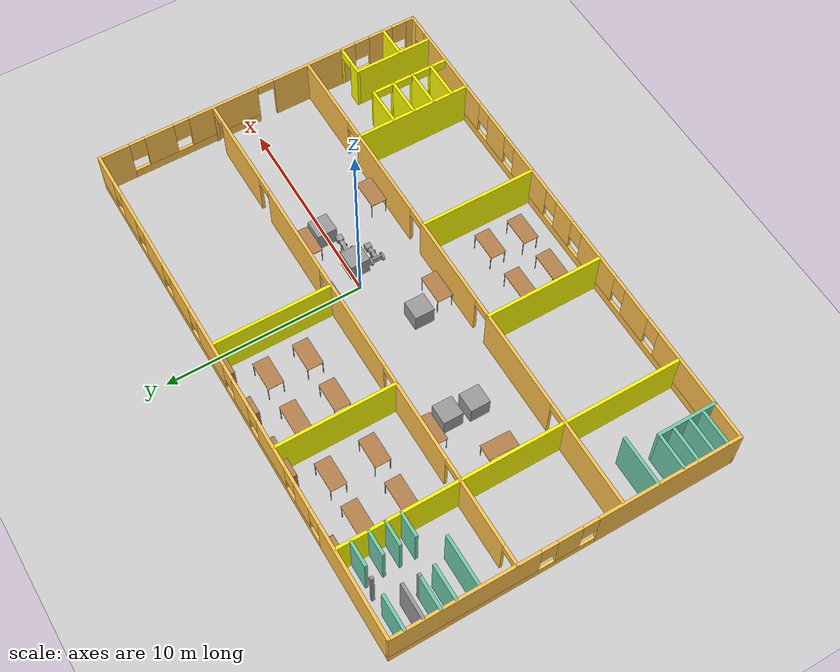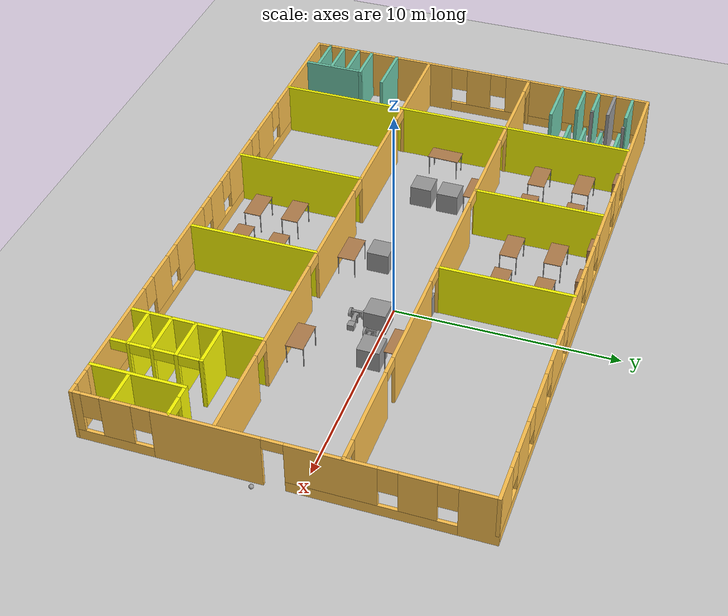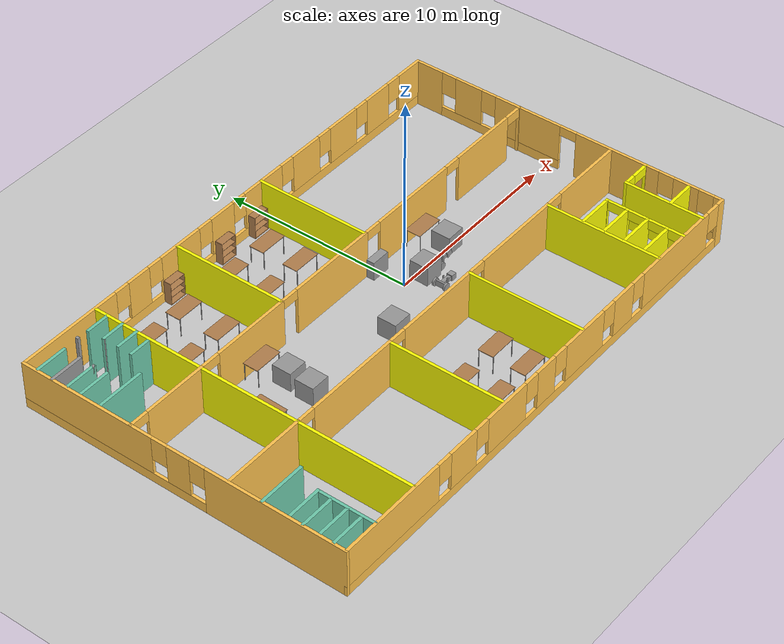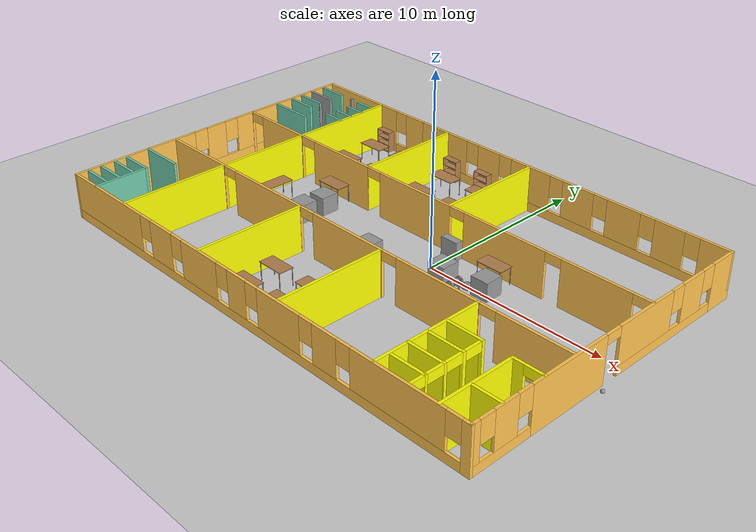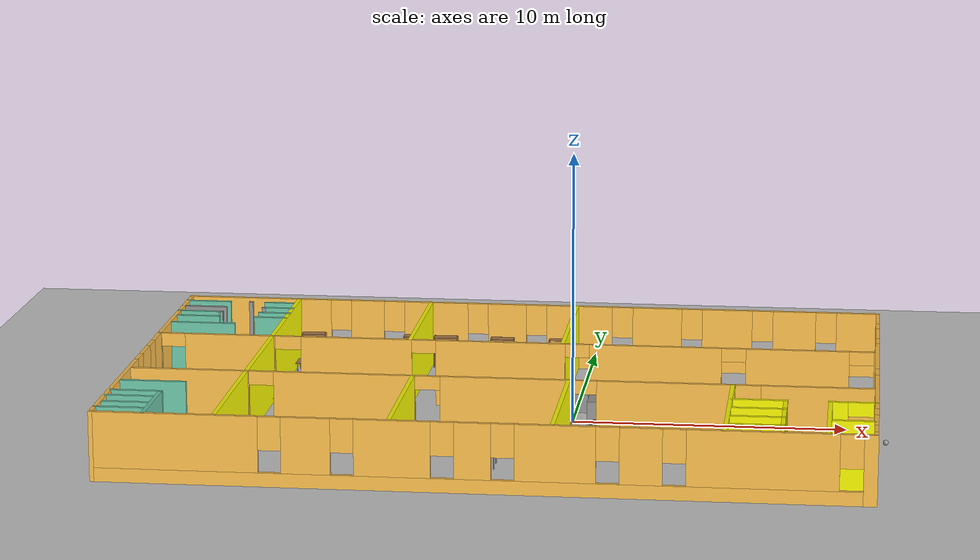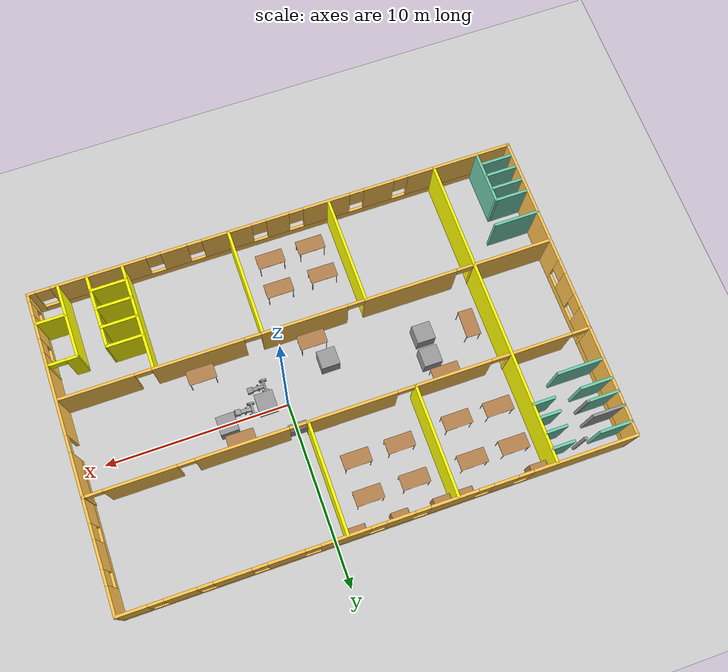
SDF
<sdf version="1.6">
 <world name="default">
  <plugin name="wel_mes" filename="libwel_mes.so"/>
  <light name="sun" type="directional">
   <pose>0 0 10 0 -0 0</pose>
   <diffuse>0.8 0.8 0.8 1</diffuse>
   <specular>0.2 0.2 0.2 1</specular>
   <attenuation>
    <range>1000</range>
    <constant>0.9</constant>
    <linear>0.01</linear>
    <quadratic>0.001</quadratic>
   </attenuation>
   <direction>-0.5 0.1 -0.9</direction>
  </light>
  <model name="ground_plane">
   <static>1</static>
   <link name="link">
    <collision name="collision">
     <geometry><plane><normal>0 0 1</normal><size>100 100</size></plane></geometry>
     <surface><friction><ode><mu>100</mu><mu2>50</mu2></ode></friction></surface>
    </collision>
    <visual name="visual">
     <cast_shadows>0</cast_shadows>
     <geometry><plane><normal>0 0 1</normal><size>100 100</size></plane></geometry>
     <material>
      <script><uri>file://media/materials/scripts/gazebo.material</uri><name>Gazebo/Grey</name></script>
     </material>
    </visual>
   </link>
  </model>
  <gravity>0 0 -9.8</gravity>
  <magnetic_field>6e-06 2.3e-05 -4.2e-05</magnetic_field>
  <atmosphere type="adiabatic"/>
  <physics name="default_physics" default="0" type="ode">
   <max_step_size>0.001</max_step_size>
   <real_time_factor>1</real_time_factor>
   <real_time_update_rate>1000</real_time_update_rate>
  </physics>
  <scene><ambient>0.4 0.4 0.4 1</ambient><background>0.7 0.7 0.7 1</background><shadows>1</shadows></scene>
  <spherical_coordinates>
   <surface_model>EARTH_WGS84</surface_model>
   <latitude_deg>0</latitude_deg>
   <longitude_deg>0</longitude_deg>
   <elevation>0</elevation>
   <heading_deg>0</heading_deg>
  </spherical_coordinates>
  <model name="mybuilding">
   <pose>-2.36213 -0.825276 0 0 -0 0</pose>
   <link name="Wall_104">
    <collision name="Wall_104_Collision">
     <geometry><box><size>17.1 0.15 2.5</size></box></geometry>
     <pose>0 0 1.25 0 -0 0</pose>
    </collision>
    <visual name="Wall_104_Visual">
     <pose>0 0 1.25 0 -0 0</pose>
     <geometry><box><size>17.1 0.15 2.5</size></box></geometry>
     <material>
      <script><uri>file://media/materials/scripts/gazebo.material</uri><name>Gazebo/Grey</name></script>
      <ambient>1 1 0 1</ambient>
     </material>
     <meta><layer>0</layer></meta>
    </visual>
    <pose>-9.12987 -0.014892 0 0 0 -1.5708</pose>
   </link>
   <link name="Wall_106">
    <collision name="Wall_106_Collision">
     <geometry><box><size>2.5 0.15 2.5</size></box></geometry>
     <pose>0 0 1.25 0 -0 0</pose>
    </collision>
    <visual name="Wall_106_Visual">
     <pose>0 0 1.25 0 -0 0</pose>
     <geometry><box><size>2.5 0.15 2.5</size></box></geometry>
     <material>
      <script><uri>file://media/materials/scripts/gazebo.material</uri><name>Gazebo/Grey</name></script>
      <ambient>0.435294 0.796078 0.67451 1</ambient>
     </material>
     <meta><layer>0</layer></meta>
    </visual>
    <pose>-12.1433 4.3296 0 0 -0 0</pose>
   </link>
   <link name="Wall_111">
    <collision name="Wall_111_Collision">
     <geometry><box><size>2.5 0.15 2.5</size></box></geometry>
     <pose>0 0 1.25 0 -0 0</pose>
    </collision>
    <visual name="Wall_111_Visual">
     <pose>0 0 1.25 0 -0 0</pose>
     <geometry><box><size>2.5 0.15 2.5</size></box></geometry>
     <material>
      <script><uri>file://media/materials/scripts/gazebo.material</uri><name>Gazebo/Grey</name></script>
      <ambient>0.435294 0.796078 0.67451 1</ambient>
     </material>
     <meta><layer>0</layer></meta>
    </visual>
    <pose>-12.2145 -4.32806 0 0 -0 0</pose>
   </link>
   <link name="Wall_113">
    <collision name="Wall_113_Collision">
     <geometry><box><size>1.75 0.15 2.5</size></box></geometry>
     <pose>0 0 1.25 0 -0 0</pose>
    </collision>
    <visual name="Wall_113_Visual">
     <pose>0 0 1.25 0 -0 0</pose>
     <geometry><box><size>1.75 0.15 2.5</size></box></geometry>
     <material>
      <script><uri>file://media/materials/scripts/gazebo.material</uri><name>Gazebo/Grey</name></script>
      <ambient>0.435294 0.796078 0.67451 1</ambient>
     </material>
     <meta><layer>0</layer></meta>
    </visual>
    <pose>-12.5657 5.4207 0 0 -0 0</pose>
   </link>
   <link name="Wall_118">
    <collision name="Wall_118_Collision">
     <geometry><box><size>1.75 0.15 2.5</size></box></geometry>
     <pose>0 0 1.25 0 -0 0</pose>
    </collision>
    <visual name="Wall_118_Visual">
     <pose>0 0 1.25 0 -0 0</pose>
     <geometry><box><size>1.75 0.15 2.5</size></box></geometry>
     <material>
      <script><uri>file://media/materials/scripts/gazebo.material</uri><name>Gazebo/Grey</name></script>
      <ambient>1 1 1 1</ambient>
     </material>
     <meta><layer>0</layer></meta>
    </visual>
    <pose>-12.591 6.93726 0 0 -0 0</pose>
   </link>
   <link name="Wall_122">
    <collision name="Wall_122_Collision">
     <geometry><box><size>1.75 0.15 2.5</size></box></geometry>
     <pose>0 0 1.25 0 -0 0</pose>
    </collision>
    <visual name="Wall_122_Visual">
     <pose>0 0 1.25 0 -0 0</pose>
     <geometry><box><size>1.75 0.15 2.5</size></box></geometry>
     <material>
      <script><uri>file://media/materials/scripts/gazebo.material</uri><name>Gazebo/Grey</name></script>
      <ambient>0.435294 0.796078 0.67451 1</ambient>
     </material>
     <meta><layer>0</layer></meta>
    </visual>
    <pose>-12.591 7.81489 0 0 -0 0</pose>
   </link>
   <link name="Wall_124">
    <collision name="Wall_124_Collision">
     <geometry><box><size>1.75 0.15 2.5</size></box></geometry>
     <pose>0 0 1.25 0 -0 0</pose>
    </collision>
    <visual name="Wall_124_Visual">
     <pose>0 0 1.25 0 -0 0</pose>
     <geometry><box><size>1.75 0.15 2.5</size></box></geometry>
     <material>
      <script><uri>file://media/materials/scripts/gazebo.material</uri><name>Gazebo/Grey</name></script>
      <ambient>0.435294 0.796078 0.67451 1</ambient>
     </material>
     <meta><layer>0</layer></meta>
    </visual>
    <pose>-12.591 6.15451 0 0 -0 0</pose>
   </link>
   <link name="Wall_125">
    <collision name="Wall_125_Collision">
     <geometry><box><size>0.16 0.15 2.5</size></box></geometry>
     <pose>0 0 1.25 0 -0 0</pose>
    </collision>
    <visual name="Wall_125_Visual">
     <pose>0 0 1.25 0 -0 0</pose>
     <geometry><box><size>0.16 0.15 2.5</size></box></geometry>
     <material>
      <script><uri>file://media/materials/scripts/gazebo.material</uri><name>Gazebo/Grey</name></script>
      <ambient>0 0 0 0</ambient>
     </material>
     <meta><layer>0</layer></meta>
    </visual>
    <pose>-11.786 6.15451 0 0 -0 0</pose>
   </link>
   <link name="Wall_128">
    <collision name="Wall_128_Collision">
     <geometry><box><size>1.25 0.15 2.5</size></box></geometry>
     <pose>0 0 1.25 0 -0 0</pose>
    </collision>
    <visual name="Wall_128_Visual">
     <pose>0 0 1.25 0 -0 0</pose>
     <geometry><box><size>1.25 0.15 2.5</size></box></geometry>
     <material>
      <script><uri>file://media/materials/scripts/gazebo.material</uri><name>Gazebo/Grey</name></script>
      <ambient>0.435294 0.796078 0.67451 1</ambient>
     </material>
     <meta><layer>0</layer></meta>
    </visual>
    <pose>-9.76007 7.80847 0 0 -0 3.14159</pose>
   </link>
   <link name="Wall_130">
    <collision name="Wall_130_Collision">
     <geometry><box><size>1.25 0.15 2.5</size></box></geometry>
     <pose>0 0 1.25 0 -0 0</pose>
    </collision>
    <visual name="Wall_130_Visual">
     <pose>0 0 1.25 0 -0 0</pose>
     <geometry><box><size>1.25 0.15 2.5</size></box></geometry>
     <material>
      <script><uri>file://media/materials/scripts/gazebo.material</uri><name>Gazebo/Grey</name></script>
      <ambient>0.435294 0.796078 0.67451 1</ambient>
     </material>
     <meta><layer>0</layer></meta>
    </visual>
    <pose>-9.71164 6.96281 0 0 -0 3.14159</pose>
   </link>
   <link name="Wall_131">
    <collision name="Wall_131_Collision">
     <geometry><box><size>0.16 0.15 2.5</size></box></geometry>
     <pose>0 0 1.25 0 -0 0</pose>
    </collision>
    <visual name="Wall_131_Visual">
     <pose>0 0 1.25 0 -0 0</pose>
     <geometry><box><size>0.16 0.15 2.5</size></box></geometry>
     <material>
      <script><uri>file://media/materials/scripts/gazebo.material</uri><name>Gazebo/Grey</name></script>
      <ambient>0 0 0 0</ambient>
     </material>
     <meta><layer>0</layer></meta>
    </visual>
    <pose>-10.2566 6.96281 0 0 -0 0</pose>
   </link>
   <link name="Wall_132">
    <collision name="Wall_132_Collision">
     <geometry><box><size>1.25 0.15 2.5</size></box></geometry>
     <pose>0 0 1.25 0 -0 0</pose>
    </collision>
    <visual name="Wall_132_Visual">
     <pose>0 0 1.25 0 -0 0</pose>
     <geometry><box><size>1.25 0.15 2.5</size></box></geometry>
     <material>
      <script><uri>file://media/materials/scripts/gazebo.material</uri><name>Gazebo/Grey</name></script>
      <ambient>0.435294 0.796078 0.67451 1</ambient>
     </material>
     <meta><layer>0</layer></meta>
    </visual>
    <pose>-9.70141 6.15841 0 0 -0 3.14159</pose>
   </link>
   <link name="Wall_134">
    <collision name="Wall_134_Collision">
     <geometry><box><size>1.25 0.15 2.5</size></box></geometry>
     <pose>0 0 1.25 0 -0 0</pose>
    </collision>
    <visual name="Wall_134_Visual">
     <pose>0 0 1.25 0 -0 0</pose>
     <geometry><box><size>1.25 0.15 2.5</size></box></geometry>
     <material>
      <script><uri>file://media/materials/scripts/gazebo.material</uri><name>Gazebo/Grey</name></script>
      <ambient>0.435294 0.796078 0.67451 1</ambient>
     </material>
     <meta><layer>0</layer></meta>
    </visual>
    <pose>-9.7135 5.41701 0 0 -0 3.14159</pose>
   </link>
   <link name="Wall_139">
    <collision name="Wall_139_Collision">
     <geometry><box><size>3 0.15 2.5</size></box></geometry>
     <pose>0 0 1.25 0 -0 0</pose>
    </collision>
    <visual name="Wall_139_Visual">
     <pose>0 0 1.25 0 -0 0</pose>
     <geometry><box><size>3 0.15 2.5</size></box></geometry>
     <material>
      <script><uri>file://media/materials/scripts/gazebo.material</uri><name>Gazebo/Grey</name></script>
      <ambient>0.435294 0.796078 0.67451 1</ambient>
     </material>
     <meta><layer>0</layer></meta>
    </visual>
    <pose>-11.6 -7.09333 0 0 -0 1.5708</pose>
   </link>
   <link name="Wall_140">
    <collision name="Wall_140_Collision">
     <geometry><box><size>1.9 0.15 2.5</size></box></geometry>
     <pose>0 0 1.25 0 -0 0</pose>
    </collision>
    <visual name="Wall_140_Visual">
     <pose>0 0 1.25 0 -0 0</pose>
     <geometry><box><size>1.9 0.15 2.5</size></box></geometry>
     <material>
      <script><uri>file://media/materials/scripts/gazebo.material</uri><name>Gazebo/Grey</name></script>
      <ambient>0.435294 0.796078 0.67451 1</ambient>
     </material>
     <meta><layer>0</layer></meta>
    </visual>
    <pose>-12.475 -5.66833 0 0 -0 3.14159</pose>
   </link>
   <link name="Wall_142">
    <collision name="Wall_142_Collision">
     <geometry><box><size>1.75 0.15 2.5</size></box></geometry>
     <pose>0 0 1.25 0 -0 0</pose>
    </collision>
    <visual name="Wall_142_Visual">
     <pose>0 0 1.25 0 -0 0</pose>
     <geometry><box><size>1.75 0.15 2.5</size></box></geometry>
     <material>
      <script><uri>file://media/materials/scripts/gazebo.material</uri><name>Gazebo/Grey</name></script>
      <ambient>0.435294 0.796078 0.67451 1</ambient>
     </material>
     <meta><layer>0</layer></meta>
    </visual>
    <pose>-12.4841 -7.19003 0 0 -0 0</pose>
   </link>
   <link name="Wall_144">
    <collision name="Wall_144_Collision">
     <geometry><box><size>1.8 0.15 2.5</size></box></geometry>
     <pose>0 0 1.25 0 -0 0</pose>
    </collision>
    <visual name="Wall_144_Visual">
     <pose>0 0 1.25 0 -0 0</pose>
     <geometry><box><size>1.8 0.15 2.5</size></box></geometry>
     <material>
      <script><uri>file://media/materials/scripts/gazebo.material</uri><name>Gazebo/Grey</name></script>
      <ambient>0.435294 0.796078 0.67451 1</ambient>
     </material>
     <meta><layer>0</layer></meta>
    </visual>
    <pose>-12.5407 -6.37701 0 0 -0 0</pose>
   </link>
   <link name="Wall_147">
    <collision name="Wall_147_Collision">
     <geometry><box><size>1.8 0.15 2.5</size></box></geometry>
     <pose>0 0 1.25 0 -0 0</pose>
    </collision>
    <visual name="Wall_147_Visual">
     <pose>0 0 1.25 0 -0 0</pose>
     <geometry><box><size>1.8 0.15 2.5</size></box></geometry>
     <material>
      <script><uri>file://media/materials/scripts/gazebo.material</uri><name>Gazebo/Grey</name></script>
      <ambient>0.435294 0.796078 0.67451 1</ambient>
     </material>
     <meta><layer>0</layer></meta>
    </visual>
    <pose>-12.5758 -7.90564 0 0 -0 0</pose>
   </link>
   <link name="Wall_149">
    <collision name="Wall_149_Collision">
     <geometry><box><size>6 0.15 2.5</size></box></geometry>
     <pose>0 0 1.25 0 -0 0</pose>
    </collision>
    <visual name="Wall_149_Visual">
     <pose>0 0 1.25 0 -0 0</pose>
     <geometry><box><size>6 0.15 2.5</size></box></geometry>
     <material>
      <script><uri>file://media/materials/scripts/gazebo.material</uri><name>Gazebo/Grey</name></script>
      <ambient>1 1 0 1</ambient>
     </material>
     <meta><layer>0</layer></meta>
    </visual>
    <pose>1.80042 5.59279 0 0 0 -1.5708</pose>
   </link>
   <link name="Wall_151">
    <collision name="Wall_151_Collision">
     <geometry><box><size>6 0.15 2.5</size></box></geometry>
     <pose>0 0 1.25 0 -0 0</pose>
    </collision>
    <visual name="Wall_151_Visual">
     <pose>0 0 1.25 0 -0 0</pose>
     <geometry><box><size>6 0.15 2.5</size></box></geometry>
     <material>
      <script><uri>file://media/materials/scripts/gazebo.material</uri><name>Gazebo/Grey</name></script>
      <ambient>1 1 0 1</ambient>
     </material>
     <meta><layer>0</layer></meta>
    </visual>
    <pose>-3.91292 5.55304 0 0 0 -1.5708</pose>
   </link>
   <link name="Wall_154">
    <collision name="Wall_154_Collision">
     <geometry><box><size>6 0.15 2.5</size></box></geometry>
     <pose>0 0 1.25 0 -0 0</pose>
    </collision>
    <visual name="Wall_154_Visual">
     <pose>0 0 1.25 0 -0 0</pose>
     <geometry><box><size>6 0.15 2.5</size></box></geometry>
     <material>
      <script><uri>file://media/materials/scripts/gazebo.material</uri><name>Gazebo/Grey</name></script>
      <ambient>1 1 0 1</ambient>
     </material>
     <meta><layer>0</layer></meta>
    </visual>
    <pose>2.51252 -5.57355 0 0 0 -1.5708</pose>
   </link>
   <link name="Wall_156">
    <collision name="Wall_156_Collision">
     <geometry><box><size>6 0.15 2.5</size></box></geometry>
     <pose>0 0 1.25 0 -0 0</pose>
    </collision>
    <visual name="Wall_156_Visual">
     <pose>0 0 1.25 0 -0 0</pose>
     <geometry><box><size>6 0.15 2.5</size></box></geometry>
     <material>
      <script><uri>file://media/materials/scripts/gazebo.material</uri><name>Gazebo/Grey</name></script>
      <ambient>1 1 0 1</ambient>
     </material>
     <meta><layer>0</layer></meta>
    </visual>
    <pose>-3.08532 -5.54983 0 0 0 -1.5708</pose>
   </link>
   <link name="Wall_158">
    <collision name="Wall_158_Collision">
     <geometry><box><size>6 0.15 2.5</size></box></geometry>
     <pose>0 0 1.25 0 -0 0</pose>
    </collision>
    <visual name="Wall_158_Visual">
     <pose>0 0 1.25 0 -0 0</pose>
     <geometry><box><size>6 0.15 2.5</size></box></geometry>
     <material>
      <script><uri>file://media/materials/scripts/gazebo.material</uri><name>Gazebo/Grey</name></script>
      <ambient>1 1 0 1</ambient>
     </material>
     <meta><layer>0</layer></meta>
    </visual>
    <pose>8.34754 -5.57355 0 0 0 -1.5708</pose>
   </link>
   <link name="Wall_162">
    <collision name="Wall_162_Collision">
     <geometry><box><size>2 0.15 2.5</size></box></geometry>
     <pose>0 0 1.25 0 -0 0</pose>
    </collision>
    <visual name="Wall_162_Visual">
     <pose>0 0 1.25 0 -0 0</pose>
     <geometry><box><size>2 0.15 2.5</size></box></geometry>
     <material>
      <script><uri>file://media/materials/scripts/gazebo.material</uri><name>Gazebo/Grey</name></script>
      <ambient>1 1 0 1</ambient>
     </material>
     <meta><layer>0</layer></meta>
    </visual>
    <pose>9.34295 -4.49272 0 0 0 -8.3e-05</pose>
   </link>
   <link name="Wall_163">
    <pose>10.2678 -6.5178 0 0 0 -1.5708</pose>
    <visual name="Wall_163_Visual_0">
     <pose>-2.0133 0 1.25 0 -0 0</pose>
     <geometry><box><size>0.173407 0.15 2.5</size></box></geometry>
     <material>
      <script><uri>file://media/materials/scripts/gazebo.material</uri><name>Gazebo/Grey</name></script>
      <ambient>1 1 0 1</ambient>
     </material>
     <meta><layer>0</layer></meta>
    </visual>
    <collision name="Wall_163_Collision_0">
     <geometry><box><size>0.173407 0.15 2.5</size></box></geometry>
     <pose>-2.0133 0 1.25 0 -0 0</pose>
    </collision>
    <visual name="Wall_163_Visual_1">
     <pose>-0.937243 0 1.25 0 -0 0</pose>
     <geometry><box><size>0.1787 0.15 2.5</size></box></geometry>
     <material>
      <script><uri>file://media/materials/scripts/gazebo.material</uri><name>Gazebo/Grey</name></script>
      <ambient>1 1 0 1</ambient>
     </material>
     <meta><layer>0</layer></meta>
    </visual>
    <collision name="Wall_163_Collision_1">
     <geometry><box><size>0.1787 0.15 2.5</size></box></geometry>
     <pose>-0.937243 0 1.25 0 -0 0</pose>
    </collision>
    <visual name="Wall_163_Visual_2">
     <pose>0.125594 0 1.25 0 -0 0</pose>
     <geometry><box><size>0.146974 0.15 2.5</size></box></geometry>
     <material>
      <script><uri>file://media/materials/scripts/gazebo.material</uri><name>Gazebo/Grey</name></script>
      <ambient>1 1 0 1</ambient>
     </material>
     <meta><layer>0</layer></meta>
    </visual>
    <collision name="Wall_163_Collision_2">
     <geometry><box><size>0.146974 0.15 2.5</size></box></geometry>
     <pose>0.125594 0 1.25 0 -0 0</pose>
    </collision>
    <visual name="Wall_163_Visual_3">
     <pose>1.16567 0 1.25 0 -0 0</pose>
     <geometry><box><size>0.133179 0.15 2.5</size></box></geometry>
     <material>
      <script><uri>file://media/materials/scripts/gazebo.material</uri><name>Gazebo/Grey</name></script>
      <ambient>1 1 0 1</ambient>
     </material>
     <meta><layer>0</layer></meta>
    </visual>
    <collision name="Wall_163_Collision_3">
     <geometry><box><size>0.133179 0.15 2.5</size></box></geometry>
     <pose>1.16567 0 1.25 0 -0 0</pose>
    </collision>
    <visual name="Wall_163_Visual_4">
     <pose>-1.47659 0 2.25 0 -0 0</pose>
     <geometry><box><size>0.9 0.15 0.5</size></box></geometry>
     <material>
      <script><uri>file://media/materials/scripts/gazebo.material</uri><name>Gazebo/Grey</name></script>
      <ambient>1 1 0 1</ambient>
     </material>
     <meta><layer>0</layer></meta>
    </visual>
    <collision name="Wall_163_Collision_4">
     <geometry><box><size>0.9 0.15 0.5</size></box></geometry>
     <pose>-1.47659 0 2.25 0 -0 0</pose>
    </collision>
    <visual name="Wall_163_Visual_5">
     <pose>-0.397893 0 2.25 0 -0 0</pose>
     <geometry><box><size>0.9 0.15 0.5</size></box></geometry>
     <material>
      <script><uri>file://media/materials/scripts/gazebo.material</uri><name>Gazebo/Grey</name></script>
      <ambient>1 1 0 1</ambient>
     </material>
     <meta><layer>0</layer></meta>
    </visual>
    <collision name="Wall_163_Collision_5">
     <geometry><box><size>0.9 0.15 0.5</size></box></geometry>
     <pose>-0.397893 0 2.25 0 -0 0</pose>
    </collision>
    <visual name="Wall_163_Visual_6">
     <pose>0.649081 0 2.25 0 -0 0</pose>
     <geometry><box><size>0.9 0.15 0.5</size></box></geometry>
     <material>
      <script><uri>file://media/materials/scripts/gazebo.material</uri><name>Gazebo/Grey</name></script>
      <ambient>1 1 0 1</ambient>
     </material>
     <meta><layer>0</layer></meta>
    </visual>
    <collision name="Wall_163_Collision_6">
     <geometry><box><size>0.9 0.15 0.5</size></box></geometry>
     <pose>0.649081 0 2.25 0 -0 0</pose>
    </collision>
    <visual name="Wall_163_Visual_7">
     <pose>1.66613 0 2.25 0 -0 0</pose>
     <geometry><box><size>0.867739 0.15 0.5</size></box></geometry>
     <material>
      <script><uri>file://media/materials/scripts/gazebo.material</uri><name>Gazebo/Grey</name></script>
      <ambient>1 1 0 1</ambient>
     </material>
     <meta><layer>0</layer></meta>
    </visual>
    <collision name="Wall_163_Collision_7">
     <geometry><box><size>0.867739 0.15 0.5</size></box></geometry>
     <pose>1.66613 0 2.25 0 -0 0</pose>
    </collision>
   </link>
   <link name="Wall_171">
    <pose>12.6222 -4.4809 0 0 -0 3.14159</pose>
    <visual name="Wall_171_Visual_0">
     <pose>-0.79093 0 1.25 0 -0 0</pose>
     <geometry><box><size>0.168139 0.15 2.5</size></box></geometry>
     <material>
      <script><uri>file://media/materials/scripts/gazebo.material</uri><name>Gazebo/Grey</name></script>
      <ambient>1 1 0 1</ambient>
     </material>
     <meta><layer>0</layer></meta>
    </visual>
    <collision name="Wall_171_Collision_0">
     <geometry><box><size>0.168139 0.15 2.5</size></box></geometry>
     <pose>-0.79093 0 1.25 0 -0 0</pose>
    </collision>
    <visual name="Wall_171_Visual_1">
     <pose>0.53407 0 1.25 0 -0 0</pose>
     <geometry><box><size>0.681861 0.15 2.5</size></box></geometry>
     <material>
      <script><uri>file://media/materials/scripts/gazebo.material</uri><name>Gazebo/Grey</name></script>
      <ambient>1 1 0 1</ambient>
     </material>
     <meta><layer>0</layer></meta>
    </visual>
    <collision name="Wall_171_Collision_1">
     <geometry><box><size>0.681861 0.15 2.5</size></box></geometry>
     <pose>0.53407 0 1.25 0 -0 0</pose>
    </collision>
    <visual name="Wall_171_Visual_2">
     <pose>-0.256861 0 2.25 0 -0 0</pose>
     <geometry><box><size>0.9 0.15 0.5</size></box></geometry>
     <material>
      <script><uri>file://media/materials/scripts/gazebo.material</uri><name>Gazebo/Grey</name></script>
      <ambient>1 1 0 1</ambient>
     </material>
     <meta><layer>0</layer></meta>
    </visual>
    <collision name="Wall_171_Collision_2">
     <geometry><box><size>0.9 0.15 0.5</size></box></geometry>
     <pose>-0.256861 0 2.25 0 -0 0</pose>
    </collision>
   </link>
   <link name="Wall_172">
    <collision name="Wall_172_Collision">
     <geometry><box><size>4.2 0.15 2.5</size></box></geometry>
     <pose>0 0 1.25 0 -0 0</pose>
    </collision>
    <visual name="Wall_172_Visual">
     <pose>0 0 1.25 0 -0 0</pose>
     <geometry><box><size>4.2 0.15 2.5</size></box></geometry>
     <material>
      <script><uri>file://media/materials/scripts/gazebo.material</uri><name>Gazebo/Grey</name></script>
      <ambient>1 1 0 1</ambient>
     </material>
     <meta><layer>0</layer></meta>
    </visual>
    <pose>11.8222 -6.5059 0 0 0 -1.5708</pose>
   </link>
   <link name="Wall_174">
    <collision name="Wall_174_Collision">
     <geometry><box><size>1.65 0.15 2.5</size></box></geometry>
     <pose>0 0 1.25 0 -0 0</pose>
    </collision>
    <visual name="Wall_174_Visual">
     <pose>0 0 1.25 0 -0 0</pose>
     <geometry><box><size>1.65 0.15 2.5</size></box></geometry>
     <material>
      <script><uri>file://media/materials/scripts/gazebo.material</uri><name>Gazebo/Grey</name></script>
      <ambient>1 1 0 1</ambient>
     </material>
     <meta><layer>0</layer></meta>
    </visual>
    <pose>12.6046 -6.85286 0 0 -0 0</pose>
   </link>
   <link name="Wall_176">
    <collision name="Wall_176_Collision">
     <geometry><box><size>2 0.15 2.5</size></box></geometry>
     <pose>0 0 1.25 0 -0 0</pose>
    </collision>
    <visual name="Wall_176_Visual">
     <pose>0 0 1.25 0 -0 0</pose>
     <geometry><box><size>2 0.15 2.5</size></box></geometry>
     <material>
      <script><uri>file://media/materials/scripts/gazebo.material</uri><name>Gazebo/Grey</name></script>
      <ambient>1 1 0 1</ambient>
     </material>
     <meta><layer>0</layer></meta>
    </visual>
    <pose>9.29387 -6.66723 0 0 -0 0</pose>
   </link>
   <link name="Wall_179">
    <collision name="Wall_179_Collision">
     <geometry><box><size>2 0.15 2.5</size></box></geometry>
     <pose>0 0 1.25 0 -0 0</pose>
    </collision>
    <visual name="Wall_179_Visual">
     <pose>0 0 1.25 0 -0 0</pose>
     <geometry><box><size>2 0.15 2.5</size></box></geometry>
     <material>
      <script><uri>file://media/materials/scripts/gazebo.material</uri><name>Gazebo/Grey</name></script>
      <ambient>1 1 0 1</ambient>
     </material>
     <meta><layer>0</layer></meta>
    </visual>
    <pose>9.31988 -5.59469 0 0 -0 0</pose>
   </link>
   <link name="Wall_182">
    <collision name="Wall_182_Collision">
     <geometry><box><size>2 0.15 2.5</size></box></geometry>
     <pose>0 0 1.25 0 -0 0</pose>
    </collision>
    <visual name="Wall_182_Visual">
     <pose>0 0 1.25 0 -0 0</pose>
     <geometry><box><size>2 0.15 2.5</size></box></geometry>
     <material>
      <script><uri>file://media/materials/scripts/gazebo.material</uri><name>Gazebo/Grey</name></script>
      <ambient>1 1 0 1</ambient>
     </material>
     <meta><layer>0</layer></meta>
    </visual>
    <pose>9.29143 -7.70507 0 0 -0 0</pose>
   </link>
   <link name="Wall_185">
    <collision name="Wall_185_Collision">
     <geometry><box><size>0.15 0.15 2.5</size></box></geometry>
     <pose>0 0 1.25 0 -0 0</pose>
    </collision>
    <visual name="Wall_185_Visual">
     <pose>0 0 1.25 0 -0 0</pose>
     <geometry><box><size>0.15 0.15 2.5</size></box></geometry>
     <material>
      <script><uri>file://media/materials/scripts/gazebo.material</uri><name>Gazebo/Grey</name></script>
      <ambient>1 1 1 1</ambient>
     </material>
     <meta><layer>0</layer></meta>
    </visual>
    <pose>-10.9249 7.85699 0 0 -0 0</pose>
   </link>
   <link name="Wall_89">
    <pose>-13.425 0 0 0 -0 1.5708</pose>
    <visual name="Wall_89_Visual_0">
     <pose>-5.00389 0 1.25 0 -0 0</pose>
     <geometry><box><size>7.24221 0.15 2.5</size></box></geometry>
     <material>
      <script><uri>file://media/materials/scripts/gazebo.material</uri><name>Gazebo/Grey</name></script>
      <ambient>1 0.764706 0.305882 1</ambient>
     </material>
     <meta><layer>0</layer></meta>
    </visual>
    <collision name="Wall_89_Collision_0">
     <geometry><box><size>7.24221 0.15 2.5</size></box></geometry>
     <pose>-5.00389 0 1.25 0 -0 0</pose>
    </collision>
    <visual name="Wall_89_Visual_1">
     <pose>3.62111 0 0.25 0 -0 0</pose>
     <geometry><box><size>10.0078 0.15 0.5</size></box></geometry>
     <material>
      <script><uri>file://media/materials/scripts/gazebo.material</uri><name>Gazebo/Grey</name></script>
      <ambient>1 0.764706 0.305882 1</ambient>
     </material>
     <meta><layer>0</layer></meta>
    </visual>
    <collision name="Wall_89_Collision_1">
     <geometry><box><size>10.0078 0.15 0.5</size></box></geometry>
     <pose>3.62111 0 0.25 0 -0 0</pose>
    </collision>
    <visual name="Wall_89_Visual_2">
     <pose>0.026482 0 1.5 0 -0 0</pose>
     <geometry><box><size>1.21854 0.15 2</size></box></geometry>
     <material>
      <script><uri>file://media/materials/scripts/gazebo.material</uri><name>Gazebo/Grey</name></script>
      <ambient>1 0.764706 0.305882 1</ambient>
     </material>
     <meta><layer>0</layer></meta>
    </visual>
    <collision name="Wall_89_Collision_2">
     <geometry><box><size>1.21854 0.15 2</size></box></geometry>
     <pose>0.026482 0 1.5 0 -0 0</pose>
    </collision>
    <visual name="Wall_89_Visual_3">
     <pose>5.03038 0 1.5 0 -0 0</pose>
     <geometry><box><size>7.18925 0.15 2</size></box></geometry>
     <material>
      <script><uri>file://media/materials/scripts/gazebo.material</uri><name>Gazebo/Grey</name></script>
      <ambient>1 0.764706 0.305882 1</ambient>
     </material>
     <meta><layer>0</layer></meta>
    </visual>
    <collision name="Wall_89_Collision_3">
     <geometry><box><size>7.18925 0.15 2</size></box></geometry>
     <pose>5.03038 0 1.5 0 -0 0</pose>
    </collision>
    <visual name="Wall_89_Visual_4">
     <pose>-0.982788 0 1.9 0 -0 0</pose>
     <geometry><box><size>0.8 0.15 1.2</size></box></geometry>
     <material>
      <script><uri>file://media/materials/scripts/gazebo.material</uri><name>Gazebo/Grey</name></script>
      <ambient>1 0.764706 0.305882 1</ambient>
     </material>
     <meta><layer>0</layer></meta>
    </visual>
    <collision name="Wall_89_Collision_4">
     <geometry><box><size>0.8 0.15 1.2</size></box></geometry>
     <pose>-0.982788 0 1.9 0 -0 0</pose>
    </collision>
    <visual name="Wall_89_Visual_5">
     <pose>1.03575 0 1.9 0 -0 0</pose>
     <geometry><box><size>0.8 0.15 1.2</size></box></geometry>
     <material>
      <script><uri>file://media/materials/scripts/gazebo.material</uri><name>Gazebo/Grey</name></script>
      <ambient>1 0.764706 0.305882 1</ambient>
     </material>
     <meta><layer>0</layer></meta>
    </visual>
    <collision name="Wall_89_Collision_5">
     <geometry><box><size>0.8 0.15 1.2</size></box></geometry>
     <pose>1.03575 0 1.9 0 -0 0</pose>
    </collision>
   </link>
   <link name="Wall_90">
    <pose>0 8.55 0 0 -0 0</pose>
    <visual name="Wall_90_Visual_0">
     <pose>-10.6849 0 1.25 0 -0 0</pose>
     <geometry><box><size>5.63012 0.15 2.5</size></box></geometry>
     <material>
      <script><uri>file://media/materials/scripts/gazebo.material</uri><name>Gazebo/Grey</name></script>
      <ambient>1 0.764706 0.305882 1</ambient>
     </material>
     <meta><layer>0</layer></meta>
    </visual>
    <collision name="Wall_90_Collision_0">
     <geometry><box><size>5.63012 0.15 2.5</size></box></geometry>
     <pose>-10.6849 0 1.25 0 -0 0</pose>
    </collision>
    <visual name="Wall_90_Visual_1">
     <pose>2.81506 0 0.25 0 -0 0</pose>
     <geometry><box><size>21.3699 0.15 0.5</size></box></geometry>
     <material>
      <script><uri>file://media/materials/scripts/gazebo.material</uri><name>Gazebo/Grey</name></script>
      <ambient>1 0.764706 0.305882 1</ambient>
     </material>
     <meta><layer>0</layer></meta>
    </visual>
    <collision name="Wall_90_Collision_1">
     <geometry><box><size>21.3699 0.15 0.5</size></box></geometry>
     <pose>2.81506 0 0.25 0 -0 0</pose>
    </collision>
    <visual name="Wall_90_Visual_2">
     <pose>-6.41969 0 1.5 0 -0 0</pose>
     <geometry><box><size>1.30037 0.15 2</size></box></geometry>
     <material>
      <script><uri>file://media/materials/scripts/gazebo.material</uri><name>Gazebo/Grey</name></script>
      <ambient>1 0.764706 0.305882 1</ambient>
     </material>
     <meta><layer>0</layer></meta>
    </visual>
    <collision name="Wall_90_Collision_2">
     <geometry><box><size>1.30037 0.15 2</size></box></geometry>
     <pose>-6.41969 0 1.5 0 -0 0</pose>
    </collision>
    <visual name="Wall_90_Visual_3">
     <pose>-3.71922 0 1.5 0 -0 0</pose>
     <geometry><box><size>2.50059 0.15 2</size></box></geometry>
     <material>
      <script><uri>file://media/materials/scripts/gazebo.material</uri><name>Gazebo/Grey</name></script>
      <ambient>1 0.764706 0.305882 1</ambient>
     </material>
     <meta><layer>0</layer></meta>
    </visual>
    <collision name="Wall_90_Collision_3">
     <geometry><box><size>2.50059 0.15 2</size></box></geometry>
     <pose>-3.71922 0 1.5 0 -0 0</pose>
    </collision>
    <visual name="Wall_90_Visual_4">
     <pose>-0.923265 0 1.5 0 -0 0</pose>
     <geometry><box><size>1.49131 0.15 2</size></box></geometry>
     <material>
      <script><uri>file://media/materials/scripts/gazebo.material</uri><name>Gazebo/Grey</name></script>
      <ambient>1 0.764706 0.305882 1</ambient>
     </material>
     <meta><layer>0</layer></meta>
    </visual>
    <collision name="Wall_90_Collision_4">
     <geometry><box><size>1.49131 0.15 2</size></box></geometry>
     <pose>-0.923265 0 1.5 0 -0 0</pose>
    </collision>
    <visual name="Wall_90_Visual_5">
     <pose>1.90157 0 1.5 0 -0 0</pose>
     <geometry><box><size>2.55835 0.15 2</size></box></geometry>
     <material>
      <script><uri>file://media/materials/scripts/gazebo.material</uri><name>Gazebo/Grey</name></script>
      <ambient>1 0.764706 0.305882 1</ambient>
     </material>
     <meta><layer>0</layer></meta>
    </visual>
    <collision name="Wall_90_Collision_5">
     <geometry><box><size>2.55835 0.15 2</size></box></geometry>
     <pose>1.90157 0 1.5 0 -0 0</pose>
    </collision>
    <visual name="Wall_90_Visual_6">
     <pose>4.92912 0 1.5 0 -0 0</pose>
     <geometry><box><size>1.89675 0.15 2</size></box></geometry>
     <material>
      <script><uri>file://media/materials/scripts/gazebo.material</uri><name>Gazebo/Grey</name></script>
      <ambient>1 0.764706 0.305882 1</ambient>
     </material>
     <meta><layer>0</layer></meta>
    </visual>
    <collision name="Wall_90_Collision_6">
     <geometry><box><size>1.89675 0.15 2</size></box></geometry>
     <pose>4.92912 0 1.5 0 -0 0</pose>
    </collision>
    <visual name="Wall_90_Visual_7">
     <pose>7.64173 0 1.5 0 -0 0</pose>
     <geometry><box><size>1.92848 0.15 2</size></box></geometry>
     <material>
      <script><uri>file://media/materials/scripts/gazebo.material</uri><name>Gazebo/Grey</name></script>
      <ambient>1 0.764706 0.305882 1</ambient>
     </material>
     <meta><layer>0</layer></meta>
    </visual>
    <collision name="Wall_90_Collision_7">
     <geometry><box><size>1.92848 0.15 2</size></box></geometry>
     <pose>7.64173 0 1.5 0 -0 0</pose>
    </collision>
    <visual name="Wall_90_Visual_8">
     <pose>10.2274 0 1.5 0 -0 0</pose>
     <geometry><box><size>1.64294 0.15 2</size></box></geometry>
     <material>
      <script><uri>file://media/materials/scripts/gazebo.material</uri><name>Gazebo/Grey</name></script>
      <ambient>1 0.764706 0.305882 1</ambient>
     </material>
     <meta><layer>0</layer></meta>
    </visual>
    <collision name="Wall_90_Collision_8">
     <geometry><box><size>1.64294 0.15 2</size></box></geometry>
     <pose>10.2274 0 1.5 0 -0 0</pose>
    </collision>
    <visual name="Wall_90_Visual_9">
     <pose>12.6745 0 1.5 0 -0 0</pose>
     <geometry><box><size>1.65109 0.15 2</size></box></geometry>
     <material>
      <script><uri>file://media/materials/scripts/gazebo.material</uri><name>Gazebo/Grey</name></script>
      <ambient>1 0.764706 0.305882 1</ambient>
     </material>
     <meta><layer>0</layer></meta>
    </visual>
    <collision name="Wall_90_Collision_9">
     <geometry><box><size>1.65109 0.15 2</size></box></geometry>
     <pose>12.6745 0 1.5 0 -0 0</pose>
    </collision>
    <visual name="Wall_90_Visual_10">
     <pose>-7.46988 0 1.9 0 -0 0</pose>
     <geometry><box><size>0.8 0.15 1.2</size></box></geometry>
     <material>
      <script><uri>file://media/materials/scripts/gazebo.material</uri><name>Gazebo/Grey</name></script>
      <ambient>1 0.764706 0.305882 1</ambient>
     </material>
     <meta><layer>0</layer></meta>
    </visual>
    <collision name="Wall_90_Collision_10">
     <geometry><box><size>0.8 0.15 1.2</size></box></geometry>
     <pose>-7.46988 0 1.9 0 -0 0</pose>
    </collision>
    <visual name="Wall_90_Visual_11">
     <pose>-5.36951 0 1.9 0 -0 0</pose>
     <geometry><box><size>0.8 0.15 1.2</size></box></geometry>
     <material>
      <script><uri>file://media/materials/scripts/gazebo.material</uri><name>Gazebo/Grey</name></script>
      <ambient>1 0.764706 0.305882 1</ambient>
     </material>
     <meta><layer>0</layer></meta>
    </visual>
    <collision name="Wall_90_Collision_11">
     <geometry><box><size>0.8 0.15 1.2</size></box></geometry>
     <pose>-5.36951 0 1.9 0 -0 0</pose>
    </collision>
    <visual name="Wall_90_Visual_12">
     <pose>-2.06892 0 1.9 0 -0 0</pose>
     <geometry><box><size>0.8 0.15 1.2</size></box></geometry>
     <material>
      <script><uri>file://media/materials/scripts/gazebo.material</uri><name>Gazebo/Grey</name></script>
      <ambient>1 0.764706 0.305882 1</ambient>
     </material>
     <meta><layer>0</layer></meta>
    </visual>
    <collision name="Wall_90_Collision_12">
     <geometry><box><size>0.8 0.15 1.2</size></box></geometry>
     <pose>-2.06892 0 1.9 0 -0 0</pose>
    </collision>
    <visual name="Wall_90_Visual_13">
     <pose>0.222393 0 1.9 0 -0 0</pose>
     <geometry><box><size>0.8 0.15 1.2</size></box></geometry>
     <material>
      <script><uri>file://media/materials/scripts/gazebo.material</uri><name>Gazebo/Grey</name></script>
      <ambient>1 0.764706 0.305882 1</ambient>
     </material>
     <meta><layer>0</layer></meta>
    </visual>
    <collision name="Wall_90_Collision_13">
     <geometry><box><size>0.8 0.15 1.2</size></box></geometry>
     <pose>0.222393 0 1.9 0 -0 0</pose>
    </collision>
    <visual name="Wall_90_Visual_14">
     <pose>3.58074 0 1.9 0 -0 0</pose>
     <geometry><box><size>0.8 0.15 1.2</size></box></geometry>
     <material>
      <script><uri>file://media/materials/scripts/gazebo.material</uri><name>Gazebo/Grey</name></script>
      <ambient>1 0.764706 0.305882 1</ambient>
     </material>
     <meta><layer>0</layer></meta>
    </visual>
    <collision name="Wall_90_Collision_14">
     <geometry><box><size>0.8 0.15 1.2</size></box></geometry>
     <pose>3.58074 0 1.9 0 -0 0</pose>
    </collision>
    <visual name="Wall_90_Visual_15">
     <pose>6.27749 0 1.9 0 -0 0</pose>
     <geometry><box><size>0.8 0.15 1.2</size></box></geometry>
     <material>
      <script><uri>file://media/materials/scripts/gazebo.material</uri><name>Gazebo/Grey</name></script>
      <ambient>1 0.764706 0.305882 1</ambient>
     </material>
     <meta><layer>0</layer></meta>
    </visual>
    <collision name="Wall_90_Collision_15">
     <geometry><box><size>0.8 0.15 1.2</size></box></geometry>
     <pose>6.27749 0 1.9 0 -0 0</pose>
    </collision>
    <visual name="Wall_90_Visual_16">
     <pose>9.00597 0 1.9 0 -0 0</pose>
     <geometry><box><size>0.8 0.15 1.2</size></box></geometry>
     <material>
      <script><uri>file://media/materials/scripts/gazebo.material</uri><name>Gazebo/Grey</name></script>
      <ambient>1 0.764706 0.305882 1</ambient>
     </material>
     <meta><layer>0</layer></meta>
    </visual>
    <collision name="Wall_90_Collision_16">
     <geometry><box><size>0.8 0.15 1.2</size></box></geometry>
     <pose>9.00597 0 1.9 0 -0 0</pose>
    </collision>
    <visual name="Wall_90_Visual_17">
     <pose>11.4489 0 1.9 0 -0 0</pose>
     <geometry><box><size>0.8 0.15 1.2</size></box></geometry>
     <material>
      <script><uri>file://media/materials/scripts/gazebo.material</uri><name>Gazebo/Grey</name></script>
      <ambient>1 0.764706 0.305882 1</ambient>
     </material>
     <meta><layer>0</layer></meta>
    </visual>
    <collision name="Wall_90_Collision_17">
     <geometry><box><size>0.8 0.15 1.2</size></box></geometry>
     <pose>11.4489 0 1.9 0 -0 0</pose>
    </collision>
   </link>
   <link name="Wall_91">
    <pose>13.425 0 0 0 0 -1.5708</pose>
    <visual name="Wall_91_Visual_0">
     <pose>-7.82957 0 1.25 0 -0 0</pose>
     <geometry><box><size>1.59086 0.15 2.5</size></box></geometry>
     <material>
      <script><uri>file://media/materials/scripts/gazebo.material</uri><name>Gazebo/Grey</name></script>
      <ambient>1 0.764706 0.305882 1</ambient>
     </material>
     <meta><layer>0</layer></meta>
    </visual>
    <collision name="Wall_91_Collision_0">
     <geometry><box><size>1.59086 0.15 2.5</size></box></geometry>
     <pose>-7.82957 0 1.25 0 -0 0</pose>
    </collision>
    <visual name="Wall_91_Visual_1">
     <pose>2.94053 0 1.25 0 -0 0</pose>
     <geometry><box><size>4.5435 0.15 2.5</size></box></geometry>
     <material>
      <script><uri>file://media/materials/scripts/gazebo.material</uri><name>Gazebo/Grey</name></script>
      <ambient>1 0.764706 0.305882 1</ambient>
     </material>
     <meta><layer>0</layer></meta>
    </visual>
    <collision name="Wall_91_Collision_1">
     <geometry><box><size>4.5435 0.15 2.5</size></box></geometry>
     <pose>2.94053 0 1.25 0 -0 0</pose>
    </collision>
    <visual name="Wall_91_Visual_2">
     <pose>-3.63268 0 0.25 0 -0 0</pose>
     <geometry><box><size>6.80292 0.15 0.5</size></box></geometry>
     <material>
      <script><uri>file://media/materials/scripts/gazebo.material</uri><name>Gazebo/Grey</name></script>
      <ambient>1 0.764706 0.305882 1</ambient>
     </material>
     <meta><layer>0</layer></meta>
    </visual>
    <collision name="Wall_91_Collision_2">
     <geometry><box><size>6.80292 0.15 0.5</size></box></geometry>
     <pose>-3.63268 0 0.25 0 -0 0</pose>
    </collision>
    <visual name="Wall_91_Visual_3">
     <pose>6.91864 0 0.25 0 -0 0</pose>
     <geometry><box><size>3.41272 0.15 0.5</size></box></geometry>
     <material>
      <script><uri>file://media/materials/scripts/gazebo.material</uri><name>Gazebo/Grey</name></script>
      <ambient>1 0.764706 0.305882 1</ambient>
     </material>
     <meta><layer>0</layer></meta>
    </visual>
    <collision name="Wall_91_Collision_3">
     <geometry><box><size>3.41272 0.15 0.5</size></box></geometry>
     <pose>6.91864 0 0.25 0 -0 0</pose>
    </collision>
    <visual name="Wall_91_Visual_4">
     <pose>-5.47612 0 1.5 0 -0 0</pose>
     <geometry><box><size>1.51603 0.15 2</size></box></geometry>
     <material>
      <script><uri>file://media/materials/scripts/gazebo.material</uri><name>Gazebo/Grey</name></script>
      <ambient>1 0.764706 0.305882 1</ambient>
     </material>
     <meta><layer>0</layer></meta>
    </visual>
    <collision name="Wall_91_Collision_4">
     <geometry><box><size>1.51603 0.15 2</size></box></geometry>
     <pose>-5.47612 0 1.5 0 -0 0</pose>
    </collision>
    <visual name="Wall_91_Visual_5">
     <pose>-2.07466 0 1.5 0 -0 0</pose>
     <geometry><box><size>3.68689 0.15 2</size></box></geometry>
     <material>
      <script><uri>file://media/materials/scripts/gazebo.material</uri><name>Gazebo/Grey</name></script>
      <ambient>1 0.764706 0.305882 1</ambient>
     </material>
     <meta><layer>0</layer></meta>
    </visual>
    <collision name="Wall_91_Collision_5">
     <geometry><box><size>3.68689 0.15 2</size></box></geometry>
     <pose>-2.07466 0 1.5 0 -0 0</pose>
    </collision>
    <visual name="Wall_91_Visual_6">
     <pose>-2.07466 0 1.5 0 -0 0</pose>
     <geometry><box><size>3.68689 0.15 2</size></box></geometry>
     <material>
      <script><uri>file://media/materials/scripts/gazebo.material</uri><name>Gazebo/Grey</name></script>
      <ambient>1 0.764706 0.305882 1</ambient>
     </material>
     <meta><layer>0</layer></meta>
    </visual>
    <collision name="Wall_91_Collision_6">
     <geometry><box><size>3.68689 0.15 2</size></box></geometry>
     <pose>-2.07466 0 1.5 0 -0 0</pose>
    </collision>
    <visual name="Wall_91_Visual_7">
     <pose>6.67512 0 1.5 0 -0 0</pose>
     <geometry><box><size>1.32567 0.15 2</size></box></geometry>
     <material>
      <script><uri>file://media/materials/scripts/gazebo.material</uri><name>Gazebo/Grey</name></script>
      <ambient>1 0.764706 0.305882 1</ambient>
     </material>
     <meta><layer>0</layer></meta>
    </visual>
    <collision name="Wall_91_Collision_7">
     <geometry><box><size>1.32567 0.15 2</size></box></geometry>
     <pose>6.67512 0 1.5 0 -0 0</pose>
    </collision>
    <visual name="Wall_91_Visual_8">
     <pose>8.38148 0 1.5 0 -0 0</pose>
     <geometry><box><size>0.487047 0.15 2</size></box></geometry>
     <material>
      <script><uri>file://media/materials/scripts/gazebo.material</uri><name>Gazebo/Grey</name></script>
      <ambient>1 0.764706 0.305882 1</ambient>
     </material>
     <meta><layer>0</layer></meta>
    </visual>
    <collision name="Wall_91_Collision_8">
     <geometry><box><size>0.487047 0.15 2</size></box></geometry>
     <pose>8.38148 0 1.5 0 -0 0</pose>
    </collision>
    <visual name="Wall_91_Visual_9">
     <pose>-6.63414 0 1.9 0 -0 0</pose>
     <geometry><box><size>0.8 0.15 1.2</size></box></geometry>
     <material>
      <script><uri>file://media/materials/scripts/gazebo.material</uri><name>Gazebo/Grey</name></script>
      <ambient>1 0.764706 0.305882 1</ambient>
     </material>
     <meta><layer>0</layer></meta>
    </visual>
    <collision name="Wall_91_Collision_9">
     <geometry><box><size>0.8 0.15 1.2</size></box></geometry>
     <pose>-6.63414 0 1.9 0 -0 0</pose>
    </collision>
    <visual name="Wall_91_Visual_10">
     <pose>5.61228 0 1.9 0 -0 0</pose>
     <geometry><box><size>0.8 0.15 1.2</size></box></geometry>
     <material>
      <script><uri>file://media/materials/scripts/gazebo.material</uri><name>Gazebo/Grey</name></script>
      <ambient>1 0.764706 0.305882 1</ambient>
     </material>
     <meta><layer>0</layer></meta>
    </visual>
    <collision name="Wall_91_Collision_10">
     <geometry><box><size>0.8 0.15 1.2</size></box></geometry>
     <pose>5.61228 0 1.9 0 -0 0</pose>
    </collision>
    <visual name="Wall_91_Visual_11">
     <pose>-4.31811 0 1.9 0 -0 0</pose>
     <geometry><box><size>0.8 0.15 1.2</size></box></geometry>
     <material>
      <script><uri>file://media/materials/scripts/gazebo.material</uri><name>Gazebo/Grey</name></script>
      <ambient>1 0.764706 0.305882 1</ambient>
     </material>
     <meta><layer>0</layer></meta>
    </visual>
    <collision name="Wall_91_Collision_11">
     <geometry><box><size>0.8 0.15 1.2</size></box></geometry>
     <pose>-4.31811 0 1.9 0 -0 0</pose>
    </collision>
    <visual name="Wall_91_Visual_12">
     <pose>7.73795 0 1.9 0 -0 0</pose>
     <geometry><box><size>0.8 0.15 1.2</size></box></geometry>
     <material>
      <script><uri>file://media/materials/scripts/gazebo.material</uri><name>Gazebo/Grey</name></script>
      <ambient>1 0.764706 0.305882 1</ambient>
     </material>
     <meta><layer>0</layer></meta>
    </visual>
    <collision name="Wall_91_Collision_12">
     <geometry><box><size>0.8 0.15 1.2</size></box></geometry>
     <pose>7.73795 0 1.9 0 -0 0</pose>
    </collision>
    <visual name="Wall_91_Visual_13">
     <pose>0.218779 0 2.25 0 -0 0</pose>
     <geometry><box><size>0.9 0.15 0.5</size></box></geometry>
     <material>
      <script><uri>file://media/materials/scripts/gazebo.material</uri><name>Gazebo/Grey</name></script>
      <ambient>1 0.764706 0.305882 1</ambient>
     </material>
     <meta><layer>0</layer></meta>
    </visual>
    <collision name="Wall_91_Collision_13">
     <geometry><box><size>0.9 0.15 0.5</size></box></geometry>
     <pose>0.218779 0 2.25 0 -0 0</pose>
    </collision>
    <visual name="Wall_91_Visual_14">
     <pose>0.218779 0 2.25 0 -0 0</pose>
     <geometry><box><size>0.9 0.15 0.5</size></box></geometry>
     <material>
      <script><uri>file://media/materials/scripts/gazebo.material</uri><name>Gazebo/Grey</name></script>
      <ambient>1 0.764706 0.305882 1</ambient>
     </material>
     <meta><layer>0</layer></meta>
    </visual>
    <collision name="Wall_91_Collision_14">
     <geometry><box><size>0.9 0.15 0.5</size></box></geometry>
     <pose>0.218779 0 2.25 0 -0 0</pose>
    </collision>
   </link>
   <link name="Wall_92">
    <pose>0 -8.55 0 0 -0 3.14159</pose>
    <visual name="Wall_92_Visual_0">
     <pose>-13.2614 0 1.25 0 -0 0</pose>
     <geometry><box><size>0.477212 0.15 2.5</size></box></geometry>
     <material>
      <script><uri>file://media/materials/scripts/gazebo.material</uri><name>Gazebo/Grey</name></script>
      <ambient>1 0.764706 0.305882 1</ambient>
     </material>
     <meta><layer>0</layer></meta>
    </visual>
    <collision name="Wall_92_Collision_0">
     <geometry><box><size>0.477212 0.15 2.5</size></box></geometry>
     <pose>-13.2614 0 1.25 0 -0 0</pose>
    </collision>
    <visual name="Wall_92_Visual_1">
     <pose>0.238606 0 0.25 0 -0 0</pose>
     <geometry><box><size>26.5228 0.15 0.5</size></box></geometry>
     <material>
      <script><uri>file://media/materials/scripts/gazebo.material</uri><name>Gazebo/Grey</name></script>
      <ambient>1 0.764706 0.305882 1</ambient>
     </material>
     <meta><layer>0</layer></meta>
    </visual>
    <collision name="Wall_92_Collision_1">
     <geometry><box><size>26.5228 0.15 0.5</size></box></geometry>
     <pose>0.238606 0 0.25 0 -0 0</pose>
    </collision>
    <visual name="Wall_92_Visual_2">
     <pose>-9.63968 0 1.5 0 -0 0</pose>
     <geometry><box><size>5.16621 0.15 2</size></box></geometry>
     <material>
      <script><uri>file://media/materials/scripts/gazebo.material</uri><name>Gazebo/Grey</name></script>
      <ambient>1 0.764706 0.305882 1</ambient>
     </material>
     <meta><layer>0</layer></meta>
    </visual>
    <collision name="Wall_92_Collision_2">
     <geometry><box><size>5.16621 0.15 2</size></box></geometry>
     <pose>-9.63968 0 1.5 0 -0 0</pose>
    </collision>
    <visual name="Wall_92_Visual_3">
     <pose>-5.52728 0 1.5 0 -0 0</pose>
     <geometry><box><size>1.45858 0.15 2</size></box></geometry>
     <material>
      <script><uri>file://media/materials/scripts/gazebo.material</uri><name>Gazebo/Grey</name></script>
      <ambient>1 0.764706 0.305882 1</ambient>
     </material>
     <meta><layer>0</layer></meta>
    </visual>
    <collision name="Wall_92_Collision_3">
     <geometry><box><size>1.45858 0.15 2</size></box></geometry>
     <pose>-5.52728 0 1.5 0 -0 0</pose>
    </collision>
    <visual name="Wall_92_Visual_4">
     <pose>-2.60995 0 1.5 0 -0 0</pose>
     <geometry><box><size>2.77609 0.15 2</size></box></geometry>
     <material>
      <script><uri>file://media/materials/scripts/gazebo.material</uri><name>Gazebo/Grey</name></script>
      <ambient>1 0.764706 0.305882 1</ambient>
     </material>
     <meta><layer>0</layer></meta>
    </visual>
    <collision name="Wall_92_Collision_4">
     <geometry><box><size>2.77609 0.15 2</size></box></geometry>
     <pose>-2.60995 0 1.5 0 -0 0</pose>
    </collision>
    <visual name="Wall_92_Visual_5">
     <pose>0.213279 0 1.5 0 -0 0</pose>
     <geometry><box><size>1.27037 0.15 2</size></box></geometry>
     <material>
      <script><uri>file://media/materials/scripts/gazebo.material</uri><name>Gazebo/Grey</name></script>
      <ambient>1 0.764706 0.305882 1</ambient>
     </material>
     <meta><layer>0</layer></meta>
    </visual>
    <collision name="Wall_92_Collision_5">
     <geometry><box><size>1.27037 0.15 2</size></box></geometry>
     <pose>0.213279 0 1.5 0 -0 0</pose>
    </collision>
    <visual name="Wall_92_Visual_6">
     <pose>2.9709 0 1.5 0 -0 0</pose>
     <geometry><box><size>2.64487 0.15 2</size></box></geometry>
     <material>
      <script><uri>file://media/materials/scripts/gazebo.material</uri><name>Gazebo/Grey</name></script>
      <ambient>1 0.764706 0.305882 1</ambient>
     </material>
     <meta><layer>0</layer></meta>
    </visual>
    <collision name="Wall_92_Collision_6">
     <geometry><box><size>2.64487 0.15 2</size></box></geometry>
     <pose>2.9709 0 1.5 0 -0 0</pose>
    </collision>
    <visual name="Wall_92_Visual_7">
     <pose>5.9481 0 1.5 0 -0 0</pose>
     <geometry><box><size>1.70954 0.15 2</size></box></geometry>
     <material>
      <script><uri>file://media/materials/scripts/gazebo.material</uri><name>Gazebo/Grey</name></script>
      <ambient>1 0.764706 0.305882 1</ambient>
     </material>
     <meta><layer>0</layer></meta>
    </visual>
    <collision name="Wall_92_Collision_7">
     <geometry><box><size>1.70954 0.15 2</size></box></geometry>
     <pose>5.9481 0 1.5 0 -0 0</pose>
    </collision>
    <visual name="Wall_92_Visual_8">
     <pose>10.5514 0 1.5 0 -0 0</pose>
     <geometry><box><size>5.89713 0.15 2</size></box></geometry>
     <material>
      <script><uri>file://media/materials/scripts/gazebo.material</uri><name>Gazebo/Grey</name></script>
      <ambient>1 0.764706 0.305882 1</ambient>
     </material>
     <meta><layer>0</layer></meta>
    </visual>
    <collision name="Wall_92_Collision_8">
     <geometry><box><size>5.89713 0.15 2</size></box></geometry>
     <pose>10.5514 0 1.5 0 -0 0</pose>
    </collision>
    <visual name="Wall_92_Visual_9">
     <pose>-12.6228 0 1.9 0 -0 0</pose>
     <geometry><box><size>0.8 0.15 1.2</size></box></geometry>
     <material>
      <script><uri>file://media/materials/scripts/gazebo.material</uri><name>Gazebo/Grey</name></script>
      <ambient>1 0.764706 0.305882 1</ambient>
     </material>
     <meta><layer>0</layer></meta>
    </visual>
    <collision name="Wall_92_Collision_9">
     <geometry><box><size>0.8 0.15 1.2</size></box></geometry>
     <pose>-12.6228 0 1.9 0 -0 0</pose>
    </collision>
    <visual name="Wall_92_Visual_10">
     <pose>-6.65658 0 1.9 0 -0 0</pose>
     <geometry><box><size>0.8 0.15 1.2</size></box></geometry>
     <material>
      <script><uri>file://media/materials/scripts/gazebo.material</uri><name>Gazebo/Grey</name></script>
      <ambient>1 0.764706 0.305882 1</ambient>
     </material>
     <meta><layer>0</layer></meta>
    </visual>
    <collision name="Wall_92_Collision_10">
     <geometry><box><size>0.8 0.15 1.2</size></box></geometry>
     <pose>-6.65658 0 1.9 0 -0 0</pose>
    </collision>
    <visual name="Wall_92_Visual_11">
     <pose>-4.39799 0 1.9 0 -0 0</pose>
     <geometry><box><size>0.8 0.15 1.2</size></box></geometry>
     <material>
      <script><uri>file://media/materials/scripts/gazebo.material</uri><name>Gazebo/Grey</name></script>
      <ambient>1 0.764706 0.305882 1</ambient>
     </material>
     <meta><layer>0</layer></meta>
    </visual>
    <collision name="Wall_92_Collision_11">
     <geometry><box><size>0.8 0.15 1.2</size></box></geometry>
     <pose>-4.39799 0 1.9 0 -0 0</pose>
    </collision>
    <visual name="Wall_92_Visual_12">
     <pose>-0.821904 0 1.9 0 -0 0</pose>
     <geometry><box><size>0.8 0.15 1.2</size></box></geometry>
     <material>
      <script><uri>file://media/materials/scripts/gazebo.material</uri><name>Gazebo/Grey</name></script>
      <ambient>1 0.764706 0.305882 1</ambient>
     </material>
     <meta><layer>0</layer></meta>
    </visual>
    <collision name="Wall_92_Collision_12">
     <geometry><box><size>0.8 0.15 1.2</size></box></geometry>
     <pose>-0.821904 0 1.9 0 -0 0</pose>
    </collision>
    <visual name="Wall_92_Visual_13">
     <pose>1.24846 0 1.9 0 -0 0</pose>
     <geometry><box><size>0.8 0.15 1.2</size></box></geometry>
     <material>
      <script><uri>file://media/materials/scripts/gazebo.material</uri><name>Gazebo/Grey</name></script>
      <ambient>1 0.764706 0.305882 1</ambient>
     </material>
     <meta><layer>0</layer></meta>
    </visual>
    <collision name="Wall_92_Collision_13">
     <geometry><box><size>0.8 0.15 1.2</size></box></geometry>
     <pose>1.24846 0 1.9 0 -0 0</pose>
    </collision>
    <visual name="Wall_92_Visual_14">
     <pose>4.69333 0 1.9 0 -0 0</pose>
     <geometry><box><size>0.8 0.15 1.2</size></box></geometry>
     <material>
      <script><uri>file://media/materials/scripts/gazebo.material</uri><name>Gazebo/Grey</name></script>
      <ambient>1 0.764706 0.305882 1</ambient>
     </material>
     <meta><layer>0</layer></meta>
    </visual>
    <collision name="Wall_92_Collision_14">
     <geometry><box><size>0.8 0.15 1.2</size></box></geometry>
     <pose>4.69333 0 1.9 0 -0 0</pose>
    </collision>
    <visual name="Wall_92_Visual_15">
     <pose>7.20287 0 1.9 0 -0 0</pose>
     <geometry><box><size>0.8 0.15 1.2</size></box></geometry>
     <material>
      <script><uri>file://media/materials/scripts/gazebo.material</uri><name>Gazebo/Grey</name></script>
      <ambient>1 0.764706 0.305882 1</ambient>
     </material>
     <meta><layer>0</layer></meta>
    </visual>
    <collision name="Wall_92_Collision_15">
     <geometry><box><size>0.8 0.15 1.2</size></box></geometry>
     <pose>7.20287 0 1.9 0 -0 0</pose>
    </collision>
   </link>
   <link name="Wall_94">
    <pose>0.000509 2.58798 0 0 -0 0</pose>
    <visual name="Wall_94_Visual_0">
     <pose>-13.4076 0 1.25 0 -0 0</pose>
     <geometry><box><size>0.134873 0.15 2.5</size></box></geometry>
     <material>
      <script><uri>file://media/materials/scripts/gazebo.material</uri><name>Gazebo/Grey</name></script>
      <ambient>1 0.764706 0.305882 1</ambient>
     </material>
     <meta><layer>0</layer></meta>
    </visual>
    <collision name="Wall_94_Collision_0">
     <geometry><box><size>0.134873 0.15 2.5</size></box></geometry>
     <pose>-13.4076 0 1.25 0 -0 0</pose>
    </collision>
    <visual name="Wall_94_Visual_1">
     <pose>-10.7308 0 1.25 0 -0 0</pose>
     <geometry><box><size>3.41873 0.15 2.5</size></box></geometry>
     <material>
      <script><uri>file://media/materials/scripts/gazebo.material</uri><name>Gazebo/Grey</name></script>
      <ambient>1 0.764706 0.305882 1</ambient>
     </material>
     <meta><layer>0</layer></meta>
    </visual>
    <collision name="Wall_94_Collision_1">
     <geometry><box><size>3.41873 0.15 2.5</size></box></geometry>
     <pose>-10.7308 0 1.25 0 -0 0</pose>
    </collision>
    <visual name="Wall_94_Visual_2">
     <pose>-5.94135 0 1.25 0 -0 0</pose>
     <geometry><box><size>4.19405 0.15 2.5</size></box></geometry>
     <material>
      <script><uri>file://media/materials/scripts/gazebo.material</uri><name>Gazebo/Grey</name></script>
      <ambient>1 0.764706 0.305882 1</ambient>
     </material>
     <meta><layer>0</layer></meta>
    </visual>
    <collision name="Wall_94_Collision_2">
     <geometry><box><size>4.19405 0.15 2.5</size></box></geometry>
     <pose>-5.94135 0 1.25 0 -0 0</pose>
    </collision>
    <visual name="Wall_94_Visual_3">
     <pose>-0.522336 0 1.25 0 -0 0</pose>
     <geometry><box><size>4.84399 0.15 2.5</size></box></geometry>
     <material>
      <script><uri>file://media/materials/scripts/gazebo.material</uri><name>Gazebo/Grey</name></script>
      <ambient>1 0.764706 0.305882 1</ambient>
     </material>
     <meta><layer>0</layer></meta>
    </visual>
    <collision name="Wall_94_Collision_3">
     <geometry><box><size>4.84399 0.15 2.5</size></box></geometry>
     <pose>-0.522336 0 1.25 0 -0 0</pose>
    </collision>
    <visual name="Wall_94_Visual_4">
     <pose>5.25225 0 1.25 0 -0 0</pose>
     <geometry><box><size>4.90518 0.15 2.5</size></box></geometry>
     <material>
      <script><uri>file://media/materials/scripts/gazebo.material</uri><name>Gazebo/Grey</name></script>
      <ambient>1 0.764706 0.305882 1</ambient>
     </material>
     <meta><layer>0</layer></meta>
    </visual>
    <collision name="Wall_94_Collision_4">
     <geometry><box><size>4.90518 0.15 2.5</size></box></geometry>
     <pose>5.25225 0 1.25 0 -0 0</pose>
    </collision>
    <visual name="Wall_94_Visual_5">
     <pose>10.5045 0 1.25 0 -0 0</pose>
     <geometry><box><size>3.79929 0.15 2.5</size></box></geometry>
     <material>
      <script><uri>file://media/materials/scripts/gazebo.material</uri><name>Gazebo/Grey</name></script>
      <ambient>1 0.764706 0.305882 1</ambient>
     </material>
     <meta><layer>0</layer></meta>
    </visual>
    <collision name="Wall_94_Collision_5">
     <geometry><box><size>3.79929 0.15 2.5</size></box></geometry>
     <pose>10.5045 0 1.25 0 -0 0</pose>
    </collision>
    <visual name="Wall_94_Visual_6">
     <pose>13.3896 0 1.25 0 -0 0</pose>
     <geometry><box><size>0.170873 0.15 2.5</size></box></geometry>
     <material>
      <script><uri>file://media/materials/scripts/gazebo.material</uri><name>Gazebo/Grey</name></script>
      <ambient>1 0.764706 0.305882 1</ambient>
     </material>
     <meta><layer>0</layer></meta>
    </visual>
    <collision name="Wall_94_Collision_6">
     <geometry><box><size>0.170873 0.15 2.5</size></box></geometry>
     <pose>13.3896 0 1.25 0 -0 0</pose>
    </collision>
    <visual name="Wall_94_Visual_7">
     <pose>-12.8901 0 2.25 0 -0 0</pose>
     <geometry><box><size>0.9 0.15 0.5</size></box></geometry>
     <material>
      <script><uri>file://media/materials/scripts/gazebo.material</uri><name>Gazebo/Grey</name></script>
      <ambient>1 0.764706 0.305882 1</ambient>
     </material>
     <meta><layer>0</layer></meta>
    </visual>
    <collision name="Wall_94_Collision_7">
     <geometry><box><size>0.9 0.15 0.5</size></box></geometry>
     <pose>-12.8901 0 2.25 0 -0 0</pose>
    </collision>
    <visual name="Wall_94_Visual_8">
     <pose>-8.52989 0 2.25 0 -0 0</pose>
     <geometry><box><size>0.983019 0.15 0.5</size></box></geometry>
     <material>
      <script><uri>file://media/materials/scripts/gazebo.material</uri><name>Gazebo/Grey</name></script>
      <ambient>1 0.764706 0.305882 1</ambient>
     </material>
     <meta><layer>0</layer></meta>
    </visual>
    <collision name="Wall_94_Collision_8">
     <geometry><box><size>0.983019 0.15 0.5</size></box></geometry>
     <pose>-8.52989 0 2.25 0 -0 0</pose>
    </collision>
    <visual name="Wall_94_Visual_9">
     <pose>-3.39433 0 2.25 0 -0 0</pose>
     <geometry><box><size>0.9 0.15 0.5</size></box></geometry>
     <material>
      <script><uri>file://media/materials/scripts/gazebo.material</uri><name>Gazebo/Grey</name></script>
      <ambient>1 0.764706 0.305882 1</ambient>
     </material>
     <meta><layer>0</layer></meta>
    </visual>
    <collision name="Wall_94_Collision_9">
     <geometry><box><size>0.9 0.15 0.5</size></box></geometry>
     <pose>-3.39433 0 2.25 0 -0 0</pose>
    </collision>
    <visual name="Wall_94_Visual_10">
     <pose>2.34966 0 2.25 0 -0 0</pose>
     <geometry><box><size>0.9 0.15 0.5</size></box></geometry>
     <material>
      <script><uri>file://media/materials/scripts/gazebo.material</uri><name>Gazebo/Grey</name></script>
      <ambient>1 0.764706 0.305882 1</ambient>
     </material>
     <meta><layer>0</layer></meta>
    </visual>
    <collision name="Wall_94_Collision_10">
     <geometry><box><size>0.9 0.15 0.5</size></box></geometry>
     <pose>2.34966 0 2.25 0 -0 0</pose>
    </collision>
    <visual name="Wall_94_Visual_11">
     <pose>8.15483 0 2.25 0 -0 0</pose>
     <geometry><box><size>0.9 0.15 0.5</size></box></geometry>
     <material>
      <script><uri>file://media/materials/scripts/gazebo.material</uri><name>Gazebo/Grey</name></script>
      <ambient>1 0.764706 0.305882 1</ambient>
     </material>
     <meta><layer>0</layer></meta>
    </visual>
    <collision name="Wall_94_Collision_11">
     <geometry><box><size>0.9 0.15 0.5</size></box></geometry>
     <pose>8.15483 0 2.25 0 -0 0</pose>
    </collision>
    <visual name="Wall_94_Visual_12">
     <pose>12.8541 0 2.25 0 -0 0</pose>
     <geometry><box><size>0.9 0.15 0.5</size></box></geometry>
     <material>
      <script><uri>file://media/materials/scripts/gazebo.material</uri><name>Gazebo/Grey</name></script>
      <ambient>1 0.764706 0.305882 1</ambient>
     </material>
     <meta><layer>0</layer></meta>
    </visual>
    <collision name="Wall_94_Collision_12">
     <geometry><box><size>0.9 0.15 0.5</size></box></geometry>
     <pose>12.8541 0 2.25 0 -0 0</pose>
    </collision>
   </link>
   <link name="Wall_96">
    <pose>-0.005489 -2.58663 0 0 -0 0</pose>
    <visual name="Wall_96_Visual_0">
     <pose>-11.1995 0 1.25 0 -0 0</pose>
     <geometry><box><size>4.35098 0.15 2.5</size></box></geometry>
     <material>
      <script><uri>file://media/materials/scripts/gazebo.material</uri><name>Gazebo/Grey</name></script>
      <ambient>1 0.764706 0.305882 1</ambient>
     </material>
     <meta><layer>0</layer></meta>
    </visual>
    <collision name="Wall_96_Collision_0">
     <geometry><box><size>4.35098 0.15 2.5</size></box></geometry>
     <pose>-11.1995 0 1.25 0 -0 0</pose>
    </collision>
    <visual name="Wall_96_Visual_1">
     <pose>-5.56001 0 1.25 0 -0 0</pose>
     <geometry><box><size>5.12803 0.15 2.5</size></box></geometry>
     <material>
      <script><uri>file://media/materials/scripts/gazebo.material</uri><name>Gazebo/Grey</name></script>
      <ambient>1 0.764706 0.305882 1</ambient>
     </material>
     <meta><layer>0</layer></meta>
    </visual>
    <collision name="Wall_96_Collision_1">
     <geometry><box><size>5.12803 0.15 2.5</size></box></geometry>
     <pose>-5.56001 0 1.25 0 -0 0</pose>
    </collision>
    <visual name="Wall_96_Visual_2">
     <pose>0.261721 0 1.25 0 -0 0</pose>
     <geometry><box><size>4.71542 0.15 2.5</size></box></geometry>
     <material>
      <script><uri>file://media/materials/scripts/gazebo.material</uri><name>Gazebo/Grey</name></script>
      <ambient>1 0.764706 0.305882 1</ambient>
     </material>
     <meta><layer>0</layer></meta>
    </visual>
    <collision name="Wall_96_Collision_2">
     <geometry><box><size>4.71542 0.15 2.5</size></box></geometry>
     <pose>0.261721 0 1.25 0 -0 0</pose>
    </collision>
    <visual name="Wall_96_Visual_3">
     <pose>5.98325 0 1.25 0 -0 0</pose>
     <geometry><box><size>4.92764 0.15 2.5</size></box></geometry>
     <material>
      <script><uri>file://media/materials/scripts/gazebo.material</uri><name>Gazebo/Grey</name></script>
      <ambient>1 0.764706 0.305882 1</ambient>
     </material>
     <meta><layer>0</layer></meta>
    </visual>
    <collision name="Wall_96_Collision_3">
     <geometry><box><size>4.92764 0.15 2.5</size></box></geometry>
     <pose>5.98325 0 1.25 0 -0 0</pose>
    </collision>
    <visual name="Wall_96_Visual_4">
     <pose>11.361 0 1.25 0 -0 0</pose>
     <geometry><box><size>4.02792 0.15 2.5</size></box></geometry>
     <material>
      <script><uri>file://media/materials/scripts/gazebo.material</uri><name>Gazebo/Grey</name></script>
      <ambient>1 0.764706 0.305882 1</ambient>
     </material>
     <meta><layer>0</layer></meta>
    </visual>
    <collision name="Wall_96_Collision_4">
     <geometry><box><size>4.02792 0.15 2.5</size></box></geometry>
     <pose>11.361 0 1.25 0 -0 0</pose>
    </collision>
    <visual name="Wall_96_Visual_5">
     <pose>-8.57402 0 2.25 0 -0 0</pose>
     <geometry><box><size>0.9 0.15 0.5</size></box></geometry>
     <material>
      <script><uri>file://media/materials/scripts/gazebo.material</uri><name>Gazebo/Grey</name></script>
      <ambient>1 0.764706 0.305882 1</ambient>
     </material>
     <meta><layer>0</layer></meta>
    </visual>
    <collision name="Wall_96_Collision_5">
     <geometry><box><size>0.9 0.15 0.5</size></box></geometry>
     <pose>-8.57402 0 2.25 0 -0 0</pose>
    </collision>
    <visual name="Wall_96_Visual_6">
     <pose>-2.54599 0 2.25 0 -0 0</pose>
     <geometry><box><size>0.9 0.15 0.5</size></box></geometry>
     <material>
      <script><uri>file://media/materials/scripts/gazebo.material</uri><name>Gazebo/Grey</name></script>
      <ambient>1 0.764706 0.305882 1</ambient>
     </material>
     <meta><layer>0</layer></meta>
    </visual>
    <collision name="Wall_96_Collision_6">
     <geometry><box><size>0.9 0.15 0.5</size></box></geometry>
     <pose>-2.54599 0 2.25 0 -0 0</pose>
    </collision>
    <visual name="Wall_96_Visual_7">
     <pose>3.06943 0 2.25 0 -0 0</pose>
     <geometry><box><size>0.9 0.15 0.5</size></box></geometry>
     <material>
      <script><uri>file://media/materials/scripts/gazebo.material</uri><name>Gazebo/Grey</name></script>
      <ambient>1 0.764706 0.305882 1</ambient>
     </material>
     <meta><layer>0</layer></meta>
    </visual>
    <collision name="Wall_96_Collision_7">
     <geometry><box><size>0.9 0.15 0.5</size></box></geometry>
     <pose>3.06943 0 2.25 0 -0 0</pose>
    </collision>
    <visual name="Wall_96_Visual_8">
     <pose>8.89708 0 2.25 0 -0 0</pose>
     <geometry><box><size>0.9 0.15 0.5</size></box></geometry>
     <material>
      <script><uri>file://media/materials/scripts/gazebo.material</uri><name>Gazebo/Grey</name></script>
      <ambient>1 0.764706 0.305882 1</ambient>
     </material>
     <meta><layer>0</layer></meta>
    </visual>
    <collision name="Wall_96_Collision_8">
     <geometry><box><size>0.9 0.15 0.5</size></box></geometry>
     <pose>8.89708 0 2.25 0 -0 0</pose>
    </collision>
   </link>
   <static>1</static>
  </model>
  <model name="robot">
   <link name="link_0">
    <pose>1.55233 -0.934021 0.2 0 -0 0</pose>
    <inertial>
     <mass>1</mass>
     <inertia>
      <ixx>0.166667</ixx>
      <ixy>0</ixy>
      <ixz>0</ixz>
      <iyy>0.166667</iyy>
      <iyz>0</iyz>
      <izz>0.166667</izz>
     </inertia>
    </inertial>
    <visual name="visual">
     <geometry><box><size>0.3 0.5 0.1</size></box></geometry>
     <material>
      <lighting>1</lighting>
      <script><uri>file://media/materials/scripts/gazebo.material</uri><name>Gazebo/Grey</name></script>
      <shader type="pixel"><normal_map>__default__</normal_map></shader>
      <ambient>0.3 0.3 0.3 1</ambient>
      <diffuse>0.7 0.7 0.7 1</diffuse>
      <specular>0.01 0.01 0.01 1</specular>
      <emissive>0 0 0 1</emissive>
     </material>
    </visual>
    <collision name="collision">
     <geometry><box><size>0.3 0.5 0.1</size></box></geometry>
     <surface>
      <friction>
       <ode><mu>1</mu><mu2>1</mu2><fdir1>0 0 0</fdir1><slip1>0</slip1><slip2>0</slip2></ode>
       <torsional>
        <coefficient>1</coefficient>
        <patch_radius>0</patch_radius>
        <surface_radius>0</surface_radius>
        <use_patch_radius>1</use_patch_radius>
        <ode><slip>0</slip></ode>
       </torsional>
      </friction>
      <bounce><restitution_coefficient>0</restitution_coefficient><threshold>1e+06</threshold></bounce>
      <contact>
       <collide_without_contact>0</collide_without_contact>
       <collide_without_contact_bitmask>1</collide_without_contact_bitmask>
       <collide_bitmask>1</collide_bitmask>
       <ode>
        <soft_cfm>0</soft_cfm>
        <soft_erp>0.2</soft_erp>
        <kp>1e+13</kp>
        <kd>1</kd>
        <max_vel>0.01</max_vel>
        <min_depth>0</min_depth>
       </ode>
       <bullet>
        <split_impulse>1</split_impulse>
        <split_impulse_penetration_threshold>-0.01</split_impulse_penetration_threshold>
        <soft_cfm>0</soft_cfm>
        <soft_erp>0.2</soft_erp>
        <kp>1e+13</kp>
        <kd>1</kd>
       </bullet>
      </contact>
     </surface>
    </collision>
   </link>
   <link name="link_1">
    <pose>1.55233 -1.23404 0.2 1.5707 -0 0</pose>
    <inertial>
     <mass>1</mass>
     <inertia><ixx>0.145833</ixx><ixy>0</ixy><ixz>0</ixz><iyy>0.145833</iyy><iyz>0</iyz><izz>0.125</izz></inertia>
    </inertial>
    <visual name="visual">
     <geometry><cylinder><radius>0.2</radius><length>0.1</length></cylinder></geometry>
     <material>
      <lighting>1</lighting>
      <script><uri>file://media/materials/scripts/gazebo.material</uri><name>Gazebo/Grey</name></script>
      <shader type="pixel"><normal_map>__default__</normal_map></shader>
      <ambient>0.3 0.3 0.3 1</ambient>
      <diffuse>0.7 0.7 0.7 1</diffuse>
      <specular>0.01 0.01 0.01 1</specular>
      <emissive>0 0 0 1</emissive>
     </material>
    </visual>
    <collision name="collision">
     <geometry><cylinder><radius>0.2</radius><length>0.1</length></cylinder></geometry>
     <surface>
      <friction>
       <ode><mu>1</mu><mu2>1</mu2><fdir1>0 0 0</fdir1><slip1>0</slip1><slip2>0</slip2></ode>
       <torsional>
        <coefficient>1</coefficient>
        <patch_radius>0</patch_radius>
        <surface_radius>0</surface_radius>
        <use_patch_radius>1</use_patch_radius>
        <ode><slip>0</slip></ode>
       </torsional>
      </friction>
      <bounce><restitution_coefficient>0</restitution_coefficient><threshold>1e+06</threshold></bounce>
      <contact>
       <collide_without_contact>0</collide_without_contact>
       <collide_without_contact_bitmask>1</collide_without_contact_bitmask>
       <collide_bitmask>1</collide_bitmask>
       <ode>
        <soft_cfm>0</soft_cfm>
        <soft_erp>0.2</soft_erp>
        <kp>1e+13</kp>
        <kd>1</kd>
        <max_vel>0.01</max_vel>
        <min_depth>0</min_depth>
       </ode>
       <bullet>
        <split_impulse>1</split_impulse>
        <split_impulse_penetration_threshold>-0.01</split_impulse_penetration_threshold>
        <soft_cfm>0</soft_cfm>
        <soft_erp>0.2</soft_erp>
        <kp>1e+13</kp>
        <kd>1</kd>
       </bullet>
      </contact>
     </surface>
    </collision>
   </link>
   <link name="link_1_clone">
    <pose>1.55233 -0.634002 0.2 1.5707 -0 0</pose>
    <inertial>
     <mass>1</mass>
     <inertia><ixx>0.145833</ixx><ixy>0</ixy><ixz>0</ixz><iyy>0.145833</iyy><iyz>0</iyz><izz>0.125</izz></inertia>
    </inertial>
    <visual name="visual">
     <geometry><cylinder><radius>0.2</radius><length>0.1</length></cylinder></geometry>
     <material>
      <lighting>1</lighting>
      <script><uri>file://media/materials/scripts/gazebo.material</uri><name>Gazebo/Grey</name></script>
      <shader type="pixel"><normal_map>__default__</normal_map></shader>
      <ambient>0.3 0.3 0.3 1</ambient>
      <diffuse>0.7 0.7 0.7 1</diffuse>
      <specular>0.01 0.01 0.01 1</specular>
      <emissive>0 0 0 1</emissive>
     </material>
    </visual>
    <collision name="collision">
     <geometry><cylinder><radius>0.2</radius><length>0.1</length></cylinder></geometry>
     <surface>
      <friction>
       <ode><mu>1</mu><mu2>1</mu2><fdir1>0 0 0</fdir1><slip1>0</slip1><slip2>0</slip2></ode>
       <torsional>
        <coefficient>1</coefficient>
        <patch_radius>0</patch_radius>
        <surface_radius>0</surface_radius>
        <use_patch_radius>1</use_patch_radius>
        <ode><slip>0</slip></ode>
       </torsional>
      </friction>
      <bounce><restitution_coefficient>0</restitution_coefficient><threshold>1e+06</threshold></bounce>
      <contact>
       <collide_without_contact>0</collide_without_contact>
       <collide_without_contact_bitmask>1</collide_without_contact_bitmask>
       <collide_bitmask>1</collide_bitmask>
       <ode>
        <soft_cfm>0</soft_cfm>
        <soft_erp>0.2</soft_erp>
        <kp>1e+13</kp>
        <kd>1</kd>
        <max_vel>0.01</max_vel>
        <min_depth>0</min_depth>
       </ode>
       <bullet>
        <split_impulse>1</split_impulse>
        <split_impulse_penetration_threshold>-0.01</split_impulse_penetration_threshold>
        <soft_cfm>0</soft_cfm>
        <soft_erp>0.2</soft_erp>
        <kp>1e+13</kp>
        <kd>1</kd>
       </bullet>
      </contact>
     </surface>
    </collision>
   </link>
   <link name="link_2">
    <pose>1.55233 -0.934021 0.54 0 -0 0</pose>
    <inertial>
     <mass>1</mass>
     <inertia>
      <ixx>0.166667</ixx>
      <ixy>0</ixy>
      <ixz>0</ixz>
      <iyy>0.166667</iyy>
      <iyz>0</iyz>
      <izz>0.166667</izz>
     </inertia>
    </inertial>
    <visual name="visual">
     <geometry><box><size>0.2 0.2 0.6</size></box></geometry>
     <material>
      <lighting>1</lighting>
      <script><uri>file://media/materials/scripts/gazebo.material</uri><name>Gazebo/Grey</name></script>
      <shader type="pixel"><normal_map>__default__</normal_map></shader>
      <ambient>0.3 0.3 0.3 1</ambient>
      <diffuse>0.7 0.7 0.7 1</diffuse>
      <specular>0.01 0.01 0.01 1</specular>
      <emissive>0 0 0 1</emissive>
     </material>
    </visual>
    <collision name="collision">
     <geometry><box><size>0.2 0.2 0.6</size></box></geometry>
     <surface>
      <friction>
       <ode><mu>1</mu><mu2>1</mu2><fdir1>0 0 0</fdir1><slip1>0</slip1><slip2>0</slip2></ode>
       <torsional>
        <coefficient>1</coefficient>
        <patch_radius>0</patch_radius>
        <surface_radius>0</surface_radius>
        <use_patch_radius>1</use_patch_radius>
        <ode><slip>0</slip></ode>
       </torsional>
      </friction>
      <bounce><restitution_coefficient>0</restitution_coefficient><threshold>1e+06</threshold></bounce>
      <contact>
       <collide_without_contact>0</collide_without_contact>
       <collide_without_contact_bitmask>1</collide_without_contact_bitmask>
       <collide_bitmask>1</collide_bitmask>
       <ode>
        <soft_cfm>0</soft_cfm>
        <soft_erp>0.2</soft_erp>
        <kp>1e+13</kp>
        <kd>1</kd>
        <max_vel>0.01</max_vel>
        <min_depth>0</min_depth>
       </ode>
       <bullet>
        <split_impulse>1</split_impulse>
        <split_impulse_penetration_threshold>-0.01</split_impulse_penetration_threshold>
        <soft_cfm>0</soft_cfm>
        <soft_erp>0.2</soft_erp>
        <kp>1e+13</kp>
        <kd>1</kd>
       </bullet>
      </contact>
     </surface>
    </collision>
   </link>
   <link name="link_3">
    <pose>1.55233 -0.934021 0.99 0 -0 0</pose>
    <inertial>
     <mass>1</mass>
     <inertia>
      <ixx>0.166667</ixx>
      <ixy>0</ixy>
      <ixz>0</ixz>
      <iyy>0.166667</iyy>
      <iyz>0</iyz>
      <izz>0.166667</izz>
     </inertia>
    </inertial>
    <visual name="visual">
     <geometry><box><size>0.3 0.3 0.3</size></box></geometry>
     <material>
      <lighting>1</lighting>
      <script><uri>file://media/materials/scripts/gazebo.material</uri><name>Gazebo/Grey</name></script>
      <shader type="pixel"><normal_map>__default__</normal_map></shader>
      <ambient>0.3 0.3 0.3 1</ambient>
      <diffuse>0.7 0.7 0.7 1</diffuse>
      <specular>0.01 0.01 0.01 1</specular>
      <emissive>0 0 0 1</emissive>
     </material>
    </visual>
    <collision name="collision">
     <geometry><box><size>0.3 0.3 0.3</size></box></geometry>
     <surface>
      <friction>
       <ode><mu>1</mu><mu2>1</mu2><fdir1>0 0 0</fdir1><slip1>0</slip1><slip2>0</slip2></ode>
       <torsional>
        <coefficient>1</coefficient>
        <patch_radius>0</patch_radius>
        <surface_radius>0</surface_radius>
        <use_patch_radius>1</use_patch_radius>
        <ode><slip>0</slip></ode>
       </torsional>
      </friction>
      <bounce><restitution_coefficient>0</restitution_coefficient><threshold>1e+06</threshold></bounce>
      <contact>
       <collide_without_contact>0</collide_without_contact>
       <collide_without_contact_bitmask>1</collide_without_contact_bitmask>
       <collide_bitmask>1</collide_bitmask>
       <ode>
        <soft_cfm>0</soft_cfm>
        <soft_erp>0.2</soft_erp>
        <kp>1e+13</kp>
        <kd>1</kd>
        <max_vel>0.01</max_vel>
        <min_depth>0</min_depth>
       </ode>
       <bullet>
        <split_impulse>1</split_impulse>
        <split_impulse_penetration_threshold>-0.01</split_impulse_penetration_threshold>
        <soft_cfm>0</soft_cfm>
        <soft_erp>0.2</soft_erp>
        <kp>1e+13</kp>
        <kd>1</kd>
       </bullet>
      </contact>
     </surface>
    </collision>
   </link>
   <link name="link_4_clone">
    <pose>1.57233 -0.819719 0.54 0 -0 0</pose>
    <inertial>
     <mass>1</mass>
     <inertia>
      <ixx>0.166667</ixx>
      <ixy>0</ixy>
      <ixz>0</ixz>
      <iyy>0.166667</iyy>
      <iyz>0</iyz>
      <izz>0.166667</izz>
     </inertia>
    </inertial>
    <visual name="visual">
     <geometry><box><size>0.5 0.03 0.08</size></box></geometry>
     <material>
      <lighting>1</lighting>
      <script><uri>file://media/materials/scripts/gazebo.material</uri><name>Gazebo/Grey</name></script>
      <shader type="pixel"><normal_map>__default__</normal_map></shader>
      <ambient>0.3 0.3 0.3 1</ambient>
      <diffuse>0.7 0.7 0.7 1</diffuse>
      <specular>0.01 0.01 0.01 1</specular>
      <emissive>0 0 0 1</emissive>
     </material>
    </visual>
    <collision name="collision">
     <geometry><box><size>0.5 0.03 0.08</size></box></geometry>
     <surface>
      <friction>
       <ode><mu>1</mu><mu2>1</mu2><fdir1>0 0 0</fdir1><slip1>0</slip1><slip2>0</slip2></ode>
       <torsional>
        <coefficient>1</coefficient>
        <patch_radius>0</patch_radius>
        <surface_radius>0</surface_radius>
        <use_patch_radius>1</use_patch_radius>
        <ode><slip>0</slip></ode>
       </torsional>
      </friction>
      <bounce><restitution_coefficient>0</restitution_coefficient><threshold>1e+06</threshold></bounce>
      <contact>
       <collide_without_contact>0</collide_without_contact>
       <collide_without_contact_bitmask>1</collide_without_contact_bitmask>
       <collide_bitmask>1</collide_bitmask>
       <ode>
        <soft_cfm>0</soft_cfm>
        <soft_erp>0.2</soft_erp>
        <kp>1e+13</kp>
        <kd>1</kd>
        <max_vel>0.01</max_vel>
        <min_depth>0</min_depth>
       </ode>
       <bullet>
        <split_impulse>1</split_impulse>
        <split_impulse_penetration_threshold>-0.01</split_impulse_penetration_threshold>
        <soft_cfm>0</soft_cfm>
        <soft_erp>0.2</soft_erp>
        <kp>1e+13</kp>
        <kd>1</kd>
       </bullet>
      </contact>
     </surface>
    </collision>
   </link>
   <link name="link_4_clone_clone">
    <pose>1.57233 -1.04902 0.54 0 -0 0</pose>
    <inertial>
     <mass>1</mass>
     <inertia>
      <ixx>0.166667</ixx>
      <ixy>0</ixy>
      <ixz>0</ixz>
      <iyy>0.166667</iyy>
      <iyz>0</iyz>
      <izz>0.166667</izz>
     </inertia>
    </inertial>
    <visual name="visual">
     <geometry><box><size>0.5 0.03 0.08</size></box></geometry>
     <material>
      <lighting>1</lighting>
      <script><uri>file://media/materials/scripts/gazebo.material</uri><name>Gazebo/Grey</name></script>
      <shader type="pixel"><normal_map>__default__</normal_map></shader>
      <ambient>0.3 0.3 0.3 1</ambient>
      <diffuse>0.7 0.7 0.7 1</diffuse>
      <specular>0.01 0.01 0.01 1</specular>
      <emissive>0 0 0 1</emissive>
     </material>
    </visual>
    <collision name="collision">
     <geometry><box><size>0.5 0.03 0.08</size></box></geometry>
     <surface>
      <friction>
       <ode><mu>1</mu><mu2>1</mu2><fdir1>0 0 0</fdir1><slip1>0</slip1><slip2>0</slip2></ode>
       <torsional>
        <coefficient>1</coefficient>
        <patch_radius>0</patch_radius>
        <surface_radius>0</surface_radius>
        <use_patch_radius>1</use_patch_radius>
        <ode><slip>0</slip></ode>
       </torsional>
      </friction>
      <bounce><restitution_coefficient>0</restitution_coefficient><threshold>1e+06</threshold></bounce>
      <contact>
       <collide_without_contact>0</collide_without_contact>
       <collide_without_contact_bitmask>1</collide_without_contact_bitmask>
       <collide_bitmask>1</collide_bitmask>
       <ode>
        <soft_cfm>0</soft_cfm>
        <soft_erp>0.2</soft_erp>
        <kp>1e+13</kp>
        <kd>1</kd>
        <max_vel>0.01</max_vel>
        <min_depth>0</min_depth>
       </ode>
       <bullet>
        <split_impulse>1</split_impulse>
        <split_impulse_penetration_threshold>-0.01</split_impulse_penetration_threshold>
        <soft_cfm>0</soft_cfm>
        <soft_erp>0.2</soft_erp>
        <kp>1e+13</kp>
        <kd>1</kd>
       </bullet>
      </contact>
     </surface>
    </collision>
   </link>
   <joint name="link_0_JOINT_1" type="revolute">
    <parent>link_0</parent>
    <child>link_1</child>
    <axis>
     <xyz>1 0 0</xyz>
     <use_parent_model_frame>0</use_parent_model_frame>
     <limit>
      <lower>-1.79769e+308</lower>
      <upper>1.79769e+308</upper>
      <effort>-1</effort>
      <velocity>-1</velocity>
     </limit>
     <dynamics>
      <spring_reference>0</spring_reference>
      <spring_stiffness>0</spring_stiffness>
      <damping>0</damping>
     </dynamics>
    </axis>
    <physics>
     <ode><limit><cfm>0</cfm><erp>0.2</erp></limit><suspension><cfm>0</cfm><erp>0.2</erp></suspension></ode>
    </physics>
   </joint>
   <joint name="link_0_JOINT_2" type="revolute">
    <parent>link_0</parent>
    <child>link_1_clone</child>
    <axis>
     <xyz>1 0 0</xyz>
     <use_parent_model_frame>0</use_parent_model_frame>
     <limit>
      <lower>-1.79769e+308</lower>
      <upper>1.79769e+308</upper>
      <effort>-1</effort>
      <velocity>-1</velocity>
     </limit>
     <dynamics>
      <spring_reference>0</spring_reference>
      <spring_stiffness>0</spring_stiffness>
      <damping>0</damping>
     </dynamics>
    </axis>
    <physics>
     <ode><limit><cfm>0</cfm><erp>0.2</erp></limit><suspension><cfm>0</cfm><erp>0.2</erp></suspension></ode>
    </physics>
   </joint>
   <joint name="link_0_JOINT_6" type="fixed">
    <parent>link_0</parent>
    <child>link_2</child>
    <physics>
     <ode><limit><cfm>0</cfm><erp>0.2</erp></limit><suspension><cfm>0</cfm><erp>0.2</erp></suspension></ode>
    </physics>
   </joint>
   <joint name="link_2_JOINT_12" type="revolute">
    <parent>link_2</parent>
    <child>link_4_clone</child>
    <axis>
     <xyz>0 0 1</xyz>
     <use_parent_model_frame>0</use_parent_model_frame>
     <limit>
      <lower>-1.79769e+308</lower>
      <upper>1.79769e+308</upper>
      <effort>-1</effort>
      <velocity>-1</velocity>
     </limit>
     <dynamics>
      <spring_reference>0</spring_reference>
      <spring_stiffness>0</spring_stiffness>
      <damping>0</damping>
     </dynamics>
    </axis>
    <physics>
     <ode><limit><cfm>0</cfm><erp>0.2</erp></limit><suspension><cfm>0</cfm><erp>0.2</erp></suspension></ode>
    </physics>
   </joint>
   <joint name="link_2_JOINT_7" type="fixed">
    <parent>link_2</parent>
    <child>link_3</child>
    <physics>
     <ode><limit><cfm>0</cfm><erp>0.2</erp></limit><suspension><cfm>0</cfm><erp>0.2</erp></suspension></ode>
    </physics>
   </joint>
   <joint name="link_2_JOINT_8" type="revolute">
    <parent>link_2</parent>
    <child>link_4_clone_clone</child>
    <axis>
     <xyz>0 0 1</xyz>
     <use_parent_model_frame>0</use_parent_model_frame>
     <limit>
      <lower>-1.79769e+308</lower>
      <upper>1.79769e+308</upper>
      <effort>-1</effort>
      <velocity>-1</velocity>
     </limit>
     <dynamics>
      <spring_reference>0</spring_reference>
      <spring_stiffness>0</spring_stiffness>
      <damping>0</damping>
      <friction>0</friction>
     </dynamics>
    </axis>
    <physics>
     <ode><limit><cfm>0</cfm><erp>0.2</erp></limit><suspension><cfm>0</cfm><erp>0.2</erp></suspension></ode>
    </physics>
   </joint>
   <static>0</static>
   <pose>0.763615 -0.429386 1.76083 3.14126 1.51734 -3.1383</pose>
  </model>
  <model name="robot_0">
   <link name="link_0">
    <pose>1.55233 -0.934021 0.2 0 -0 0</pose>
    <inertial>
     <mass>1</mass>
     <inertia>
      <ixx>0.166667</ixx>
      <ixy>0</ixy>
      <ixz>0</ixz>
      <iyy>0.166667</iyy>
      <iyz>0</iyz>
      <izz>0.166667</izz>
     </inertia>
    </inertial>
    <visual name="visual">
     <geometry><box><size>0.3 0.5 0.1</size></box></geometry>
     <material>
      <lighting>1</lighting>
      <script><uri>file://media/materials/scripts/gazebo.material</uri><name>Gazebo/Grey</name></script>
      <shader type="pixel"><normal_map>__default__</normal_map></shader>
      <ambient>0.3 0.3 0.3 1</ambient>
      <diffuse>0.7 0.7 0.7 1</diffuse>
      <specular>0.01 0.01 0.01 1</specular>
      <emissive>0 0 0 1</emissive>
     </material>
    </visual>
    <collision name="collision">
     <geometry><box><size>0.3 0.5 0.1</size></box></geometry>
     <surface>
      <friction>
       <ode><mu>1</mu><mu2>1</mu2><fdir1>0 0 0</fdir1><slip1>0</slip1><slip2>0</slip2></ode>
       <torsional>
        <coefficient>1</coefficient>
        <patch_radius>0</patch_radius>
        <surface_radius>0</surface_radius>
        <use_patch_radius>1</use_patch_radius>
        <ode><slip>0</slip></ode>
       </torsional>
      </friction>
      <bounce><restitution_coefficient>0</restitution_coefficient><threshold>1e+06</threshold></bounce>
      <contact>
       <collide_without_contact>0</collide_without_contact>
       <collide_without_contact_bitmask>1</collide_without_contact_bitmask>
       <collide_bitmask>1</collide_bitmask>
       <ode>
        <soft_cfm>0</soft_cfm>
        <soft_erp>0.2</soft_erp>
        <kp>1e+13</kp>
        <kd>1</kd>
        <max_vel>0.01</max_vel>
        <min_depth>0</min_depth>
       </ode>
       <bullet>
        <split_impulse>1</split_impulse>
        <split_impulse_penetration_threshold>-0.01</split_impulse_penetration_threshold>
        <soft_cfm>0</soft_cfm>
        <soft_erp>0.2</soft_erp>
        <kp>1e+13</kp>
        <kd>1</kd>
       </bullet>
      </contact>
     </surface>
    </collision>
   </link>
   <link name="link_1">
    <pose>1.55233 -1.23404 0.2 1.5707 -0 0</pose>
    <inertial>
     <mass>1</mass>
     <inertia><ixx>0.145833</ixx><ixy>0</ixy><ixz>0</ixz><iyy>0.145833</iyy><iyz>0</iyz><izz>0.125</izz></inertia>
    </inertial>
    <visual name="visual">
     <geometry><cylinder><radius>0.2</radius><length>0.1</length></cylinder></geometry>
     <material>
      <lighting>1</lighting>
      <script><uri>file://media/materials/scripts/gazebo.material</uri><name>Gazebo/Grey</name></script>
      <shader type="pixel"><normal_map>__default__</normal_map></shader>
      <ambient>0.3 0.3 0.3 1</ambient>
      <diffuse>0.7 0.7 0.7 1</diffuse>
      <specular>0.01 0.01 0.01 1</specular>
      <emissive>0 0 0 1</emissive>
     </material>
    </visual>
    <collision name="collision">
     <geometry><cylinder><radius>0.2</radius><length>0.1</length></cylinder></geometry>
     <surface>
      <friction>
       <ode><mu>1</mu><mu2>1</mu2><fdir1>0 0 0</fdir1><slip1>0</slip1><slip2>0</slip2></ode>
       <torsional>
        <coefficient>1</coefficient>
        <patch_radius>0</patch_radius>
        <surface_radius>0</surface_radius>
        <use_patch_radius>1</use_patch_radius>
        <ode><slip>0</slip></ode>
       </torsional>
      </friction>
      <bounce><restitution_coefficient>0</restitution_coefficient><threshold>1e+06</threshold></bounce>
      <contact>
       <collide_without_contact>0</collide_without_contact>
       <collide_without_contact_bitmask>1</collide_without_contact_bitmask>
       <collide_bitmask>1</collide_bitmask>
       <ode>
        <soft_cfm>0</soft_cfm>
        <soft_erp>0.2</soft_erp>
        <kp>1e+13</kp>
        <kd>1</kd>
        <max_vel>0.01</max_vel>
        <min_depth>0</min_depth>
       </ode>
       <bullet>
        <split_impulse>1</split_impulse>
        <split_impulse_penetration_threshold>-0.01</split_impulse_penetration_threshold>
        <soft_cfm>0</soft_cfm>
        <soft_erp>0.2</soft_erp>
        <kp>1e+13</kp>
        <kd>1</kd>
       </bullet>
      </contact>
     </surface>
    </collision>
   </link>
   <link name="link_1_clone">
    <pose>1.55233 -0.634002 0.2 1.5707 -0 0</pose>
    <inertial>
     <mass>1</mass>
     <inertia><ixx>0.145833</ixx><ixy>0</ixy><ixz>0</ixz><iyy>0.145833</iyy><iyz>0</iyz><izz>0.125</izz></inertia>
    </inertial>
    <visual name="visual">
     <geometry><cylinder><radius>0.2</radius><length>0.1</length></cylinder></geometry>
     <material>
      <lighting>1</lighting>
      <script><uri>file://media/materials/scripts/gazebo.material</uri><name>Gazebo/Grey</name></script>
      <shader type="pixel"><normal_map>__default__</normal_map></shader>
      <ambient>0.3 0.3 0.3 1</ambient>
      <diffuse>0.7 0.7 0.7 1</diffuse>
      <specular>0.01 0.01 0.01 1</specular>
      <emissive>0 0 0 1</emissive>
     </material>
    </visual>
    <collision name="collision">
     <geometry><cylinder><radius>0.2</radius><length>0.1</length></cylinder></geometry>
     <surface>
      <friction>
       <ode><mu>1</mu><mu2>1</mu2><fdir1>0 0 0</fdir1><slip1>0</slip1><slip2>0</slip2></ode>
       <torsional>
        <coefficient>1</coefficient>
        <patch_radius>0</patch_radius>
        <surface_radius>0</surface_radius>
        <use_patch_radius>1</use_patch_radius>
        <ode><slip>0</slip></ode>
       </torsional>
      </friction>
      <bounce><restitution_coefficient>0</restitution_coefficient><threshold>1e+06</threshold></bounce>
      <contact>
       <collide_without_contact>0</collide_without_contact>
       <collide_without_contact_bitmask>1</collide_without_contact_bitmask>
       <collide_bitmask>1</collide_bitmask>
       <ode>
        <soft_cfm>0</soft_cfm>
        <soft_erp>0.2</soft_erp>
        <kp>1e+13</kp>
        <kd>1</kd>
        <max_vel>0.01</max_vel>
        <min_depth>0</min_depth>
       </ode>
       <bullet>
        <split_impulse>1</split_impulse>
        <split_impulse_penetration_threshold>-0.01</split_impulse_penetration_threshold>
        <soft_cfm>0</soft_cfm>
        <soft_erp>0.2</soft_erp>
        <kp>1e+13</kp>
        <kd>1</kd>
       </bullet>
      </contact>
     </surface>
    </collision>
   </link>
   <link name="link_2">
    <pose>1.55233 -0.934021 0.54 0 -0 0</pose>
    <inertial>
     <mass>1</mass>
     <inertia>
      <ixx>0.166667</ixx>
      <ixy>0</ixy>
      <ixz>0</ixz>
      <iyy>0.166667</iyy>
      <iyz>0</iyz>
      <izz>0.166667</izz>
     </inertia>
    </inertial>
    <visual name="visual">
     <geometry><box><size>0.2 0.2 0.6</size></box></geometry>
     <material>
      <lighting>1</lighting>
      <script><uri>file://media/materials/scripts/gazebo.material</uri><name>Gazebo/Grey</name></script>
      <shader type="pixel"><normal_map>__default__</normal_map></shader>
      <ambient>0.3 0.3 0.3 1</ambient>
      <diffuse>0.7 0.7 0.7 1</diffuse>
      <specular>0.01 0.01 0.01 1</specular>
      <emissive>0 0 0 1</emissive>
     </material>
    </visual>
    <collision name="collision">
     <geometry><box><size>0.2 0.2 0.6</size></box></geometry>
     <surface>
      <friction>
       <ode><mu>1</mu><mu2>1</mu2><fdir1>0 0 0</fdir1><slip1>0</slip1><slip2>0</slip2></ode>
       <torsional>
        <coefficient>1</coefficient>
        <patch_radius>0</patch_radius>
        <surface_radius>0</surface_radius>
        <use_patch_radius>1</use_patch_radius>
        <ode><slip>0</slip></ode>
       </torsional>
      </friction>
      <bounce><restitution_coefficient>0</restitution_coefficient><threshold>1e+06</threshold></bounce>
      <contact>
       <collide_without_contact>0</collide_without_contact>
       <collide_without_contact_bitmask>1</collide_without_contact_bitmask>
       <collide_bitmask>1</collide_bitmask>
       <ode>
        <soft_cfm>0</soft_cfm>
        <soft_erp>0.2</soft_erp>
        <kp>1e+13</kp>
        <kd>1</kd>
        <max_vel>0.01</max_vel>
        <min_depth>0</min_depth>
       </ode>
       <bullet>
        <split_impulse>1</split_impulse>
        <split_impulse_penetration_threshold>-0.01</split_impulse_penetration_threshold>
        <soft_cfm>0</soft_cfm>
        <soft_erp>0.2</soft_erp>
        <kp>1e+13</kp>
        <kd>1</kd>
       </bullet>
      </contact>
     </surface>
    </collision>
   </link>
   <link name="link_3">
    <pose>1.55233 -0.934021 0.99 0 -0 0</pose>
    <inertial>
     <mass>1</mass>
     <inertia>
      <ixx>0.166667</ixx>
      <ixy>0</ixy>
      <ixz>0</ixz>
      <iyy>0.166667</iyy>
      <iyz>0</iyz>
      <izz>0.166667</izz>
     </inertia>
    </inertial>
    <visual name="visual">
     <geometry><box><size>0.3 0.3 0.3</size></box></geometry>
     <material>
      <lighting>1</lighting>
      <script><uri>file://media/materials/scripts/gazebo.material</uri><name>Gazebo/Grey</name></script>
      <shader type="pixel"><normal_map>__default__</normal_map></shader>
      <ambient>0.3 0.3 0.3 1</ambient>
      <diffuse>0.7 0.7 0.7 1</diffuse>
      <specular>0.01 0.01 0.01 1</specular>
      <emissive>0 0 0 1</emissive>
     </material>
    </visual>
    <collision name="collision">
     <geometry><box><size>0.3 0.3 0.3</size></box></geometry>
     <surface>
      <friction>
       <ode><mu>1</mu><mu2>1</mu2><fdir1>0 0 0</fdir1><slip1>0</slip1><slip2>0</slip2></ode>
       <torsional>
        <coefficient>1</coefficient>
        <patch_radius>0</patch_radius>
        <surface_radius>0</surface_radius>
        <use_patch_radius>1</use_patch_radius>
        <ode><slip>0</slip></ode>
       </torsional>
      </friction>
      <bounce><restitution_coefficient>0</restitution_coefficient><threshold>1e+06</threshold></bounce>
      <contact>
       <collide_without_contact>0</collide_without_contact>
       <collide_without_contact_bitmask>1</collide_without_contact_bitmask>
       <collide_bitmask>1</collide_bitmask>
       <ode>
        <soft_cfm>0</soft_cfm>
        <soft_erp>0.2</soft_erp>
        <kp>1e+13</kp>
        <kd>1</kd>
        <max_vel>0.01</max_vel>
        <min_depth>0</min_depth>
       </ode>
       <bullet>
        <split_impulse>1</split_impulse>
        <split_impulse_penetration_threshold>-0.01</split_impulse_penetration_threshold>
        <soft_cfm>0</soft_cfm>
        <soft_erp>0.2</soft_erp>
        <kp>1e+13</kp>
        <kd>1</kd>
       </bullet>
      </contact>
     </surface>
    </collision>
   </link>
   <link name="link_4_clone">
    <pose>1.57233 -0.819719 0.54 0 -0 0</pose>
    <inertial>
     <mass>1</mass>
     <inertia>
      <ixx>0.166667</ixx>
      <ixy>0</ixy>
      <ixz>0</ixz>
      <iyy>0.166667</iyy>
      <iyz>0</iyz>
      <izz>0.166667</izz>
     </inertia>
    </inertial>
    <visual name="visual">
     <geometry><box><size>0.5 0.03 0.08</size></box></geometry>
     <material>
      <lighting>1</lighting>
      <script><uri>file://media/materials/scripts/gazebo.material</uri><name>Gazebo/Grey</name></script>
      <shader type="pixel"><normal_map>__default__</normal_map></shader>
      <ambient>0.3 0.3 0.3 1</ambient>
      <diffuse>0.7 0.7 0.7 1</diffuse>
      <specular>0.01 0.01 0.01 1</specular>
      <emissive>0 0 0 1</emissive>
     </material>
    </visual>
    <collision name="collision">
     <geometry><box><size>0.5 0.03 0.08</size></box></geometry>
     <surface>
      <friction>
       <ode><mu>1</mu><mu2>1</mu2><fdir1>0 0 0</fdir1><slip1>0</slip1><slip2>0</slip2></ode>
       <torsional>
        <coefficient>1</coefficient>
        <patch_radius>0</patch_radius>
        <surface_radius>0</surface_radius>
        <use_patch_radius>1</use_patch_radius>
        <ode><slip>0</slip></ode>
       </torsional>
      </friction>
      <bounce><restitution_coefficient>0</restitution_coefficient><threshold>1e+06</threshold></bounce>
      <contact>
       <collide_without_contact>0</collide_without_contact>
       <collide_without_contact_bitmask>1</collide_without_contact_bitmask>
       <collide_bitmask>1</collide_bitmask>
       <ode>
        <soft_cfm>0</soft_cfm>
        <soft_erp>0.2</soft_erp>
        <kp>1e+13</kp>
        <kd>1</kd>
        <max_vel>0.01</max_vel>
        <min_depth>0</min_depth>
       </ode>
       <bullet>
        <split_impulse>1</split_impulse>
        <split_impulse_penetration_threshold>-0.01</split_impulse_penetration_threshold>
        <soft_cfm>0</soft_cfm>
        <soft_erp>0.2</soft_erp>
        <kp>1e+13</kp>
        <kd>1</kd>
       </bullet>
      </contact>
     </surface>
    </collision>
   </link>
   <link name="link_4_clone_clone">
    <pose>1.57233 -1.04902 0.54 0 -0 0</pose>
    <inertial>
     <mass>1</mass>
     <inertia>
      <ixx>0.166667</ixx>
      <ixy>0</ixy>
      <ixz>0</ixz>
      <iyy>0.166667</iyy>
      <iyz>0</iyz>
      <izz>0.166667</izz>
     </inertia>
    </inertial>
    <visual name="visual">
     <geometry><box><size>0.5 0.03 0.08</size></box></geometry>
     <material>
      <lighting>1</lighting>
      <script><uri>file://media/materials/scripts/gazebo.material</uri><name>Gazebo/Grey</name></script>
      <shader type="pixel"><normal_map>__default__</normal_map></shader>
      <ambient>0.3 0.3 0.3 1</ambient>
      <diffuse>0.7 0.7 0.7 1</diffuse>
      <specular>0.01 0.01 0.01 1</specular>
      <emissive>0 0 0 1</emissive>
     </material>
    </visual>
    <collision name="collision">
     <geometry><box><size>0.5 0.03 0.08</size></box></geometry>
     <surface>
      <friction>
       <ode><mu>1</mu><mu2>1</mu2><fdir1>0 0 0</fdir1><slip1>0</slip1><slip2>0</slip2></ode>
       <torsional>
        <coefficient>1</coefficient>
        <patch_radius>0</patch_radius>
        <surface_radius>0</surface_radius>
        <use_patch_radius>1</use_patch_radius>
        <ode><slip>0</slip></ode>
       </torsional>
      </friction>
      <bounce><restitution_coefficient>0</restitution_coefficient><threshold>1e+06</threshold></bounce>
      <contact>
       <collide_without_contact>0</collide_without_contact>
       <collide_without_contact_bitmask>1</collide_without_contact_bitmask>
       <collide_bitmask>1</collide_bitmask>
       <ode>
        <soft_cfm>0</soft_cfm>
        <soft_erp>0.2</soft_erp>
        <kp>1e+13</kp>
        <kd>1</kd>
        <max_vel>0.01</max_vel>
        <min_depth>0</min_depth>
       </ode>
       <bullet>
        <split_impulse>1</split_impulse>
        <split_impulse_penetration_threshold>-0.01</split_impulse_penetration_threshold>
        <soft_cfm>0</soft_cfm>
        <soft_erp>0.2</soft_erp>
        <kp>1e+13</kp>
        <kd>1</kd>
       </bullet>
      </contact>
     </surface>
    </collision>
   </link>
   <joint name="link_0_JOINT_1" type="revolute">
    <parent>link_0</parent>
    <child>link_1</child>
    <axis>
     <xyz>1 0 0</xyz>
     <use_parent_model_frame>0</use_parent_model_frame>
     <limit>
      <lower>-1.79769e+308</lower>
      <upper>1.79769e+308</upper>
      <effort>-1</effort>
      <velocity>-1</velocity>
     </limit>
     <dynamics>
      <spring_reference>0</spring_reference>
      <spring_stiffness>0</spring_stiffness>
      <damping>0</damping>
     </dynamics>
    </axis>
    <physics>
     <ode><limit><cfm>0</cfm><erp>0.2</erp></limit><suspension><cfm>0</cfm><erp>0.2</erp></suspension></ode>
    </physics>
   </joint>
   <joint name="link_0_JOINT_2" type="revolute">
    <parent>link_0</parent>
    <child>link_1_clone</child>
    <axis>
     <xyz>1 0 0</xyz>
     <use_parent_model_frame>0</use_parent_model_frame>
     <limit>
      <lower>-1.79769e+308</lower>
      <upper>1.79769e+308</upper>
      <effort>-1</effort>
      <velocity>-1</velocity>
     </limit>
     <dynamics>
      <spring_reference>0</spring_reference>
      <spring_stiffness>0</spring_stiffness>
      <damping>0</damping>
     </dynamics>
    </axis>
    <physics>
     <ode><limit><cfm>0</cfm><erp>0.2</erp></limit><suspension><cfm>0</cfm><erp>0.2</erp></suspension></ode>
    </physics>
   </joint>
   <joint name="link_0_JOINT_6" type="fixed">
    <parent>link_0</parent>
    <child>link_2</child>
    <physics>
     <ode><limit><cfm>0</cfm><erp>0.2</erp></limit><suspension><cfm>0</cfm><erp>0.2</erp></suspension></ode>
    </physics>
   </joint>
   <joint name="link_2_JOINT_12" type="revolute">
    <parent>link_2</parent>
    <child>link_4_clone</child>
    <axis>
     <xyz>0 0 1</xyz>
     <use_parent_model_frame>0</use_parent_model_frame>
     <limit>
      <lower>-1.79769e+308</lower>
      <upper>1.79769e+308</upper>
      <effort>-1</effort>
      <velocity>-1</velocity>
     </limit>
     <dynamics>
      <spring_reference>0</spring_reference>
      <spring_stiffness>0</spring_stiffness>
      <damping>0</damping>
     </dynamics>
    </axis>
    <physics>
     <ode><limit><cfm>0</cfm><erp>0.2</erp></limit><suspension><cfm>0</cfm><erp>0.2</erp></suspension></ode>
    </physics>
   </joint>
   <joint name="link_2_JOINT_7" type="fixed">
    <parent>link_2</parent>
    <child>link_3</child>
    <physics>
     <ode><limit><cfm>0</cfm><erp>0.2</erp></limit><suspension><cfm>0</cfm><erp>0.2</erp></suspension></ode>
    </physics>
   </joint>
   <joint name="link_2_JOINT_8" type="revolute">
    <parent>link_2</parent>
    <child>link_4_clone_clone</child>
    <axis>
     <xyz>0 0 1</xyz>
     <use_parent_model_frame>0</use_parent_model_frame>
     <limit>
      <lower>-1.79769e+308</lower>
      <upper>1.79769e+308</upper>
      <effort>-1</effort>
      <velocity>-1</velocity>
     </limit>
     <dynamics>
      <spring_reference>0</spring_reference>
      <spring_stiffness>0</spring_stiffness>
      <damping>0</damping>
      <friction>0</friction>
     </dynamics>
    </axis>
    <physics>
     <ode><limit><cfm>0</cfm><erp>0.2</erp></limit><suspension><cfm>0</cfm><erp>0.2</erp></suspension></ode>
    </physics>
   </joint>
   <static>0</static>
   <pose>1.37662 0.579234 1.67425 2e-06 1.35642 -0.016645</pose>
  </model>
  <model name="bookshelf">
   <static>1</static>
   <link name="link">
    <inertial><mass>1</mass></inertial>
    <collision name="back">
     <pose>0 0.005 0.6 0 -0 0</pose>
     <geometry><box><size>0.9 0.01 1.2</size></box></geometry>
    </collision>
    <visual name="visual1">
     <pose>0 0.005 0.6 0 -0 0</pose>
     <geometry><box><size>0.9 0.01 1.2</size></box></geometry>
     <material>
      <script><uri>file://media/materials/scripts/gazebo.material</uri><name>Gazebo/Wood</name></script>
     </material>
    </visual>
    <collision name="left_side">
     <pose>0.45 -0.195 0.6 0 -0 0</pose>
     <geometry><box><size>0.02 0.4 1.2</size></box></geometry>
    </collision>
    <visual name="visual2">
     <pose>0.45 -0.195 0.6 0 -0 0</pose>
     <geometry><box><size>0.02 0.4 1.2</size></box></geometry>
     <material>
      <script><uri>file://media/materials/scripts/gazebo.material</uri><name>Gazebo/Wood</name></script>
     </material>
    </visual>
    <collision name="right_side">
     <pose>-0.45 -0.195 0.6 0 -0 0</pose>
     <geometry><box><size>0.02 0.4 1.2</size></box></geometry>
    </collision>
    <visual name="visual3">
     <pose>-0.45 -0.195 0.6 0 -0 0</pose>
     <geometry><box><size>0.02 0.4 1.2</size></box></geometry>
     <material>
      <script><uri>file://media/materials/scripts/gazebo.material</uri><name>Gazebo/Wood</name></script>
     </material>
    </visual>
    <collision name="bottom">
     <pose>0 -0.195 0.03 0 -0 0</pose>
     <geometry><box><size>0.88 0.4 0.06</size></box></geometry>
    </collision>
    <visual name="visual4">
     <pose>0 -0.195 0.03 0 -0 0</pose>
     <geometry><box><size>0.88 0.4 0.06</size></box></geometry>
     <material>
      <script><uri>file://media/materials/scripts/gazebo.material</uri><name>Gazebo/Wood</name></script>
     </material>
    </visual>
    <collision name="top">
     <pose>0 -0.195 1.19 0 -0 0</pose>
     <geometry><box><size>0.88 0.4 0.02</size></box></geometry>
    </collision>
    <visual name="visual5">
     <pose>0 -0.195 1.19 0 -0 0</pose>
     <geometry><box><size>0.88 0.4 0.02</size></box></geometry>
     <material>
      <script><uri>file://media/materials/scripts/gazebo.material</uri><name>Gazebo/Wood</name></script>
     </material>
    </visual>
    <collision name="low_shelf">
     <pose>0 -0.195 0.43 0 -0 0</pose>
     <geometry><box><size>0.88 0.4 0.02</size></box></geometry>
    </collision>
    <visual name="visual6">
     <pose>0 -0.195 0.43 0 -0 0</pose>
     <geometry><box><size>0.88 0.4 0.02</size></box></geometry>
     <material>
      <script><uri>file://media/materials/scripts/gazebo.material</uri><name>Gazebo/Wood</name></script>
     </material>
    </visual>
    <collision name="high_shelf">
     <pose>0 -0.195 0.8 0 -0 0</pose>
     <geometry><box><size>0.88 0.4 0.02</size></box></geometry>
    </collision>
    <visual name="visual7">
     <pose>0 -0.195 0.8 0 -0 0</pose>
     <geometry><box><size>0.88 0.4 0.02</size></box></geometry>
     <material>
      <script><uri>file://media/materials/scripts/gazebo.material</uri><name>Gazebo/Wood</name></script>
     </material>
    </visual>
   </link>
   <pose>-3.44803 7.62732 0 0 -0 0</pose>
  </model>
  <model name="bookshelf_0">
   <static>1</static>
   <link name="link">
    <inertial><mass>1</mass></inertial>
    <collision name="back">
     <pose>0 0.005 0.6 0 -0 0</pose>
     <geometry><box><size>0.9 0.01 1.2</size></box></geometry>
    </collision>
    <visual name="visual1">
     <pose>0 0.005 0.6 0 -0 0</pose>
     <geometry><box><size>0.9 0.01 1.2</size></box></geometry>
     <material>
      <script><uri>file://media/materials/scripts/gazebo.material</uri><name>Gazebo/Wood</name></script>
     </material>
    </visual>
    <collision name="left_side">
     <pose>0.45 -0.195 0.6 0 -0 0</pose>
     <geometry><box><size>0.02 0.4 1.2</size></box></geometry>
    </collision>
    <visual name="visual2">
     <pose>0.45 -0.195 0.6 0 -0 0</pose>
     <geometry><box><size>0.02 0.4 1.2</size></box></geometry>
     <material>
      <script><uri>file://media/materials/scripts/gazebo.material</uri><name>Gazebo/Wood</name></script>
     </material>
    </visual>
    <collision name="right_side">
     <pose>-0.45 -0.195 0.6 0 -0 0</pose>
     <geometry><box><size>0.02 0.4 1.2</size></box></geometry>
    </collision>
    <visual name="visual3">
     <pose>-0.45 -0.195 0.6 0 -0 0</pose>
     <geometry><box><size>0.02 0.4 1.2</size></box></geometry>
     <material>
      <script><uri>file://media/materials/scripts/gazebo.material</uri><name>Gazebo/Wood</name></script>
     </material>
    </visual>
    <collision name="bottom">
     <pose>0 -0.195 0.03 0 -0 0</pose>
     <geometry><box><size>0.88 0.4 0.06</size></box></geometry>
    </collision>
    <visual name="visual4">
     <pose>0 -0.195 0.03 0 -0 0</pose>
     <geometry><box><size>0.88 0.4 0.06</size></box></geometry>
     <material>
      <script><uri>file://media/materials/scripts/gazebo.material</uri><name>Gazebo/Wood</name></script>
     </material>
    </visual>
    <collision name="top">
     <pose>0 -0.195 1.19 0 -0 0</pose>
     <geometry><box><size>0.88 0.4 0.02</size></box></geometry>
    </collision>
    <visual name="visual5">
     <pose>0 -0.195 1.19 0 -0 0</pose>
     <geometry><box><size>0.88 0.4 0.02</size></box></geometry>
     <material>
      <script><uri>file://media/materials/scripts/gazebo.material</uri><name>Gazebo/Wood</name></script>
     </material>
    </visual>
    <collision name="low_shelf">
     <pose>0 -0.195 0.43 0 -0 0</pose>
     <geometry><box><size>0.88 0.4 0.02</size></box></geometry>
    </collision>
    <visual name="visual6">
     <pose>0 -0.195 0.43 0 -0 0</pose>
     <geometry><box><size>0.88 0.4 0.02</size></box></geometry>
     <material>
      <script><uri>file://media/materials/scripts/gazebo.material</uri><name>Gazebo/Wood</name></script>
     </material>
    </visual>
    <collision name="high_shelf">
     <pose>0 -0.195 0.8 0 -0 0</pose>
     <geometry><box><size>0.88 0.4 0.02</size></box></geometry>
    </collision>
    <visual name="visual7">
     <pose>0 -0.195 0.8 0 -0 0</pose>
     <geometry><box><size>0.88 0.4 0.02</size></box></geometry>
     <material>
      <script><uri>file://media/materials/scripts/gazebo.material</uri><name>Gazebo/Wood</name></script>
     </material>
    </visual>
   </link>
   <pose>-1.15819 7.65818 0 0 -0 0</pose>
  </model>
  <model name="bookshelf_1">
   <static>1</static>
   <link name="link">
    <inertial><mass>1</mass></inertial>
    <collision name="back">
     <pose>0 0.005 0.6 0 -0 0</pose>
     <geometry><box><size>0.9 0.01 1.2</size></box></geometry>
    </collision>
    <visual name="visual1">
     <pose>0 0.005 0.6 0 -0 0</pose>
     <geometry><box><size>0.9 0.01 1.2</size></box></geometry>
     <material>
      <script><uri>file://media/materials/scripts/gazebo.material</uri><name>Gazebo/Wood</name></script>
     </material>
    </visual>
    <collision name="left_side">
     <pose>0.45 -0.195 0.6 0 -0 0</pose>
     <geometry><box><size>0.02 0.4 1.2</size></box></geometry>
    </collision>
    <visual name="visual2">
     <pose>0.45 -0.195 0.6 0 -0 0</pose>
     <geometry><box><size>0.02 0.4 1.2</size></box></geometry>
     <material>
      <script><uri>file://media/materials/scripts/gazebo.material</uri><name>Gazebo/Wood</name></script>
     </material>
    </visual>
    <collision name="right_side">
     <pose>-0.45 -0.195 0.6 0 -0 0</pose>
     <geometry><box><size>0.02 0.4 1.2</size></box></geometry>
    </collision>
    <visual name="visual3">
     <pose>-0.45 -0.195 0.6 0 -0 0</pose>
     <geometry><box><size>0.02 0.4 1.2</size></box></geometry>
     <material>
      <script><uri>file://media/materials/scripts/gazebo.material</uri><name>Gazebo/Wood</name></script>
     </material>
    </visual>
    <collision name="bottom">
     <pose>0 -0.195 0.03 0 -0 0</pose>
     <geometry><box><size>0.88 0.4 0.06</size></box></geometry>
    </collision>
    <visual name="visual4">
     <pose>0 -0.195 0.03 0 -0 0</pose>
     <geometry><box><size>0.88 0.4 0.06</size></box></geometry>
     <material>
      <script><uri>file://media/materials/scripts/gazebo.material</uri><name>Gazebo/Wood</name></script>
     </material>
    </visual>
    <collision name="top">
     <pose>0 -0.195 1.19 0 -0 0</pose>
     <geometry><box><size>0.88 0.4 0.02</size></box></geometry>
    </collision>
    <visual name="visual5">
     <pose>0 -0.195 1.19 0 -0 0</pose>
     <geometry><box><size>0.88 0.4 0.02</size></box></geometry>
     <material>
      <script><uri>file://media/materials/scripts/gazebo.material</uri><name>Gazebo/Wood</name></script>
     </material>
    </visual>
    <collision name="low_shelf">
     <pose>0 -0.195 0.43 0 -0 0</pose>
     <geometry><box><size>0.88 0.4 0.02</size></box></geometry>
    </collision>
    <visual name="visual6">
     <pose>0 -0.195 0.43 0 -0 0</pose>
     <geometry><box><size>0.88 0.4 0.02</size></box></geometry>
     <material>
      <script><uri>file://media/materials/scripts/gazebo.material</uri><name>Gazebo/Wood</name></script>
     </material>
    </visual>
    <collision name="high_shelf">
     <pose>0 -0.195 0.8 0 -0 0</pose>
     <geometry><box><size>0.88 0.4 0.02</size></box></geometry>
    </collision>
    <visual name="visual7">
     <pose>0 -0.195 0.8 0 -0 0</pose>
     <geometry><box><size>0.88 0.4 0.02</size></box></geometry>
     <material>
      <script><uri>file://media/materials/scripts/gazebo.material</uri><name>Gazebo/Wood</name></script>
     </material>
    </visual>
   </link>
   <pose>-5.67577 7.6331 0 0 -0 0</pose>
  </model>
  <model name="bookshelf_2">
   <static>1</static>
   <link name="link">
    <inertial><mass>1</mass></inertial>
    <collision name="back">
     <pose>0 0.005 0.6 0 -0 0</pose>
     <geometry><box><size>0.9 0.01 1.2</size></box></geometry>
    </collision>
    <visual name="visual1">
     <pose>0 0.005 0.6 0 -0 0</pose>
     <geometry><box><size>0.9 0.01 1.2</size></box></geometry>
     <material>
      <script><uri>file://media/materials/scripts/gazebo.material</uri><name>Gazebo/Wood</name></script>
     </material>
    </visual>
    <collision name="left_side">
     <pose>0.45 -0.195 0.6 0 -0 0</pose>
     <geometry><box><size>0.02 0.4 1.2</size></box></geometry>
    </collision>
    <visual name="visual2">
     <pose>0.45 -0.195 0.6 0 -0 0</pose>
     <geometry><box><size>0.02 0.4 1.2</size></box></geometry>
     <material>
      <script><uri>file://media/materials/scripts/gazebo.material</uri><name>Gazebo/Wood</name></script>
     </material>
    </visual>
    <collision name="right_side">
     <pose>-0.45 -0.195 0.6 0 -0 0</pose>
     <geometry><box><size>0.02 0.4 1.2</size></box></geometry>
    </collision>
    <visual name="visual3">
     <pose>-0.45 -0.195 0.6 0 -0 0</pose>
     <geometry><box><size>0.02 0.4 1.2</size></box></geometry>
     <material>
      <script><uri>file://media/materials/scripts/gazebo.material</uri><name>Gazebo/Wood</name></script>
     </material>
    </visual>
    <collision name="bottom">
     <pose>0 -0.195 0.03 0 -0 0</pose>
     <geometry><box><size>0.88 0.4 0.06</size></box></geometry>
    </collision>
    <visual name="visual4">
     <pose>0 -0.195 0.03 0 -0 0</pose>
     <geometry><box><size>0.88 0.4 0.06</size></box></geometry>
     <material>
      <script><uri>file://media/materials/scripts/gazebo.material</uri><name>Gazebo/Wood</name></script>
     </material>
    </visual>
    <collision name="top">
     <pose>0 -0.195 1.19 0 -0 0</pose>
     <geometry><box><size>0.88 0.4 0.02</size></box></geometry>
    </collision>
    <visual name="visual5">
     <pose>0 -0.195 1.19 0 -0 0</pose>
     <geometry><box><size>0.88 0.4 0.02</size></box></geometry>
     <material>
      <script><uri>file://media/materials/scripts/gazebo.material</uri><name>Gazebo/Wood</name></script>
     </material>
    </visual>
    <collision name="low_shelf">
     <pose>0 -0.195 0.43 0 -0 0</pose>
     <geometry><box><size>0.88 0.4 0.02</size></box></geometry>
    </collision>
    <visual name="visual6">
     <pose>0 -0.195 0.43 0 -0 0</pose>
     <geometry><box><size>0.88 0.4 0.02</size></box></geometry>
     <material>
      <script><uri>file://media/materials/scripts/gazebo.material</uri><name>Gazebo/Wood</name></script>
     </material>
    </visual>
    <collision name="high_shelf">
     <pose>0 -0.195 0.8 0 -0 0</pose>
     <geometry><box><size>0.88 0.4 0.02</size></box></geometry>
    </collision>
    <visual name="visual7">
     <pose>0 -0.195 0.8 0 -0 0</pose>
     <geometry><box><size>0.88 0.4 0.02</size></box></geometry>
     <material>
      <script><uri>file://media/materials/scripts/gazebo.material</uri><name>Gazebo/Wood</name></script>
     </material>
    </visual>
   </link>
   <pose>-10.8899 7.6416 0 0 -0 0</pose>
  </model>
  <model name="bookshelf_3">
   <static>1</static>
   <link name="link">
    <inertial><mass>1</mass></inertial>
    <collision name="back">
     <pose>0 0.005 0.6 0 -0 0</pose>
     <geometry><box><size>0.9 0.01 1.2</size></box></geometry>
    </collision>
    <visual name="visual1">
     <pose>0 0.005 0.6 0 -0 0</pose>
     <geometry><box><size>0.9 0.01 1.2</size></box></geometry>
     <material>
      <script><uri>file://media/materials/scripts/gazebo.material</uri><name>Gazebo/Wood</name></script>
     </material>
    </visual>
    <collision name="left_side">
     <pose>0.45 -0.195 0.6 0 -0 0</pose>
     <geometry><box><size>0.02 0.4 1.2</size></box></geometry>
    </collision>
    <visual name="visual2">
     <pose>0.45 -0.195 0.6 0 -0 0</pose>
     <geometry><box><size>0.02 0.4 1.2</size></box></geometry>
     <material>
      <script><uri>file://media/materials/scripts/gazebo.material</uri><name>Gazebo/Wood</name></script>
     </material>
    </visual>
    <collision name="right_side">
     <pose>-0.45 -0.195 0.6 0 -0 0</pose>
     <geometry><box><size>0.02 0.4 1.2</size></box></geometry>
    </collision>
    <visual name="visual3">
     <pose>-0.45 -0.195 0.6 0 -0 0</pose>
     <geometry><box><size>0.02 0.4 1.2</size></box></geometry>
     <material>
      <script><uri>file://media/materials/scripts/gazebo.material</uri><name>Gazebo/Wood</name></script>
     </material>
    </visual>
    <collision name="bottom">
     <pose>0 -0.195 0.03 0 -0 0</pose>
     <geometry><box><size>0.88 0.4 0.06</size></box></geometry>
    </collision>
    <visual name="visual4">
     <pose>0 -0.195 0.03 0 -0 0</pose>
     <geometry><box><size>0.88 0.4 0.06</size></box></geometry>
     <material>
      <script><uri>file://media/materials/scripts/gazebo.material</uri><name>Gazebo/Wood</name></script>
     </material>
    </visual>
    <collision name="top">
     <pose>0 -0.195 1.19 0 -0 0</pose>
     <geometry><box><size>0.88 0.4 0.02</size></box></geometry>
    </collision>
    <visual name="visual5">
     <pose>0 -0.195 1.19 0 -0 0</pose>
     <geometry><box><size>0.88 0.4 0.02</size></box></geometry>
     <material>
      <script><uri>file://media/materials/scripts/gazebo.material</uri><name>Gazebo/Wood</name></script>
     </material>
    </visual>
    <collision name="low_shelf">
     <pose>0 -0.195 0.43 0 -0 0</pose>
     <geometry><box><size>0.88 0.4 0.02</size></box></geometry>
    </collision>
    <visual name="visual6">
     <pose>0 -0.195 0.43 0 -0 0</pose>
     <geometry><box><size>0.88 0.4 0.02</size></box></geometry>
     <material>
      <script><uri>file://media/materials/scripts/gazebo.material</uri><name>Gazebo/Wood</name></script>
     </material>
    </visual>
    <collision name="high_shelf">
     <pose>0 -0.195 0.8 0 -0 0</pose>
     <geometry><box><size>0.88 0.4 0.02</size></box></geometry>
    </collision>
    <visual name="visual7">
     <pose>0 -0.195 0.8 0 -0 0</pose>
     <geometry><box><size>0.88 0.4 0.02</size></box></geometry>
     <material>
      <script><uri>file://media/materials/scripts/gazebo.material</uri><name>Gazebo/Wood</name></script>
     </material>
    </visual>
   </link>
   <pose>-6.87395 7.64071 0 0 -0 0</pose>
  </model>
  <model name="table">
   <static>1</static>
   <link name="link">
    <collision name="surface">
     <pose>0 0 1 0 -0 0</pose>
     <geometry><box><size>1.5 0.8 0.03</size></box></geometry>
     <surface><friction><ode><mu>0.6</mu><mu2>0.6</mu2></ode></friction></surface>
    </collision>
    <visual name="visual1">
     <pose>0 0 1 0 -0 0</pose>
     <geometry><box><size>1.5 0.8 0.03</size></box></geometry>
     <material>
      <script><uri>file://media/materials/scripts/gazebo.material</uri><name>Gazebo/Wood</name></script>
     </material>
    </visual>
    <collision name="front_left_leg">
     <pose>0.68 0.38 0.5 0 -0 0</pose>
     <geometry><cylinder><radius>0.02</radius><length>1</length></cylinder></geometry>
    </collision>
    <visual name="front_left_leg">
     <pose>0.68 0.38 0.5 0 -0 0</pose>
     <geometry><cylinder><radius>0.02</radius><length>1</length></cylinder></geometry>
     <material>
      <script><uri>file://media/materials/scripts/gazebo.material</uri><name>Gazebo/Grey</name></script>
     </material>
    </visual>
    <collision name="front_right_leg">
     <pose>0.68 -0.38 0.5 0 -0 0</pose>
     <geometry><cylinder><radius>0.02</radius><length>1</length></cylinder></geometry>
    </collision>
    <visual name="front_right_leg">
     <pose>0.68 -0.38 0.5 0 -0 0</pose>
     <geometry><cylinder><radius>0.02</radius><length>1</length></cylinder></geometry>
     <material>
      <script><uri>file://media/materials/scripts/gazebo.material</uri><name>Gazebo/Grey</name></script>
     </material>
    </visual>
    <collision name="back_right_leg">
     <pose>-0.68 -0.38 0.5 0 -0 0</pose>
     <geometry><cylinder><radius>0.02</radius><length>1</length></cylinder></geometry>
    </collision>
    <visual name="back_right_leg">
     <pose>-0.68 -0.38 0.5 0 -0 0</pose>
     <geometry><cylinder><radius>0.02</radius><length>1</length></cylinder></geometry>
     <material>
      <script><uri>file://media/materials/scripts/gazebo.material</uri><name>Gazebo/Grey</name></script>
     </material>
    </visual>
    <collision name="back_left_leg">
     <pose>-0.68 0.38 0.5 0 -0 0</pose>
     <geometry><cylinder><radius>0.02</radius><length>1</length></cylinder></geometry>
    </collision>
    <visual name="back_left_leg">
     <pose>-0.68 0.38 0.5 0 -0 0</pose>
     <geometry><cylinder><radius>0.02</radius><length>1</length></cylinder></geometry>
     <material>
      <script><uri>file://media/materials/scripts/gazebo.material</uri><name>Gazebo/Grey</name></script>
     </material>
    </visual>
   </link>
   <pose>-7.90562 5.97239 0 0 -0 0</pose>
  </model>
  <model name="table_0">
   <static>1</static>
   <link name="link">
    <collision name="surface">
     <pose>0 0 1 0 -0 0</pose>
     <geometry><box><size>1.5 0.8 0.03</size></box></geometry>
     <surface><friction><ode><mu>0.6</mu><mu2>0.6</mu2></ode></friction></surface>
    </collision>
    <visual name="visual1">
     <pose>0 0 1 0 -0 0</pose>
     <geometry><box><size>1.5 0.8 0.03</size></box></geometry>
     <material>
      <script><uri>file://media/materials/scripts/gazebo.material</uri><name>Gazebo/Wood</name></script>
     </material>
    </visual>
    <collision name="front_left_leg">
     <pose>0.68 0.38 0.5 0 -0 0</pose>
     <geometry><cylinder><radius>0.02</radius><length>1</length></cylinder></geometry>
    </collision>
    <visual name="front_left_leg">
     <pose>0.68 0.38 0.5 0 -0 0</pose>
     <geometry><cylinder><radius>0.02</radius><length>1</length></cylinder></geometry>
     <material>
      <script><uri>file://media/materials/scripts/gazebo.material</uri><name>Gazebo/Grey</name></script>
     </material>
    </visual>
    <collision name="front_right_leg">
     <pose>0.68 -0.38 0.5 0 -0 0</pose>
     <geometry><cylinder><radius>0.02</radius><length>1</length></cylinder></geometry>
    </collision>
    <visual name="front_right_leg">
     <pose>0.68 -0.38 0.5 0 -0 0</pose>
     <geometry><cylinder><radius>0.02</radius><length>1</length></cylinder></geometry>
     <material>
      <script><uri>file://media/materials/scripts/gazebo.material</uri><name>Gazebo/Grey</name></script>
     </material>
    </visual>
    <collision name="back_right_leg">
     <pose>-0.68 -0.38 0.5 0 -0 0</pose>
     <geometry><cylinder><radius>0.02</radius><length>1</length></cylinder></geometry>
    </collision>
    <visual name="back_right_leg">
     <pose>-0.68 -0.38 0.5 0 -0 0</pose>
     <geometry><cylinder><radius>0.02</radius><length>1</length></cylinder></geometry>
     <material>
      <script><uri>file://media/materials/scripts/gazebo.material</uri><name>Gazebo/Grey</name></script>
     </material>
    </visual>
    <collision name="back_left_leg">
     <pose>-0.68 0.38 0.5 0 -0 0</pose>
     <geometry><cylinder><radius>0.02</radius><length>1</length></cylinder></geometry>
    </collision>
    <visual name="back_left_leg">
     <pose>-0.68 0.38 0.5 0 -0 0</pose>
     <geometry><cylinder><radius>0.02</radius><length>1</length></cylinder></geometry>
     <material>
      <script><uri>file://media/materials/scripts/gazebo.material</uri><name>Gazebo/Grey</name></script>
     </material>
    </visual>
   </link>
   <pose>-7.90072 3.80794 0 0 -0 0</pose>
  </model>
  <model name="table_1">
   <static>1</static>
   <link name="link">
    <collision name="surface">
     <pose>0 0 1 0 -0 0</pose>
     <geometry><box><size>1.5 0.8 0.03</size></box></geometry>
     <surface><friction><ode><mu>0.6</mu><mu2>0.6</mu2></ode></friction></surface>
    </collision>
    <visual name="visual1">
     <pose>0 0 1 0 -0 0</pose>
     <geometry><box><size>1.5 0.8 0.03</size></box></geometry>
     <material>
      <script><uri>file://media/materials/scripts/gazebo.material</uri><name>Gazebo/Wood</name></script>
     </material>
    </visual>
    <collision name="front_left_leg">
     <pose>0.68 0.38 0.5 0 -0 0</pose>
     <geometry><cylinder><radius>0.02</radius><length>1</length></cylinder></geometry>
    </collision>
    <visual name="front_left_leg">
     <pose>0.68 0.38 0.5 0 -0 0</pose>
     <geometry><cylinder><radius>0.02</radius><length>1</length></cylinder></geometry>
     <material>
      <script><uri>file://media/materials/scripts/gazebo.material</uri><name>Gazebo/Grey</name></script>
     </material>
    </visual>
    <collision name="front_right_leg">
     <pose>0.68 -0.38 0.5 0 -0 0</pose>
     <geometry><cylinder><radius>0.02</radius><length>1</length></cylinder></geometry>
    </collision>
    <visual name="front_right_leg">
     <pose>0.68 -0.38 0.5 0 -0 0</pose>
     <geometry><cylinder><radius>0.02</radius><length>1</length></cylinder></geometry>
     <material>
      <script><uri>file://media/materials/scripts/gazebo.material</uri><name>Gazebo/Grey</name></script>
     </material>
    </visual>
    <collision name="back_right_leg">
     <pose>-0.68 -0.38 0.5 0 -0 0</pose>
     <geometry><cylinder><radius>0.02</radius><length>1</length></cylinder></geometry>
    </collision>
    <visual name="back_right_leg">
     <pose>-0.68 -0.38 0.5 0 -0 0</pose>
     <geometry><cylinder><radius>0.02</radius><length>1</length></cylinder></geometry>
     <material>
      <script><uri>file://media/materials/scripts/gazebo.material</uri><name>Gazebo/Grey</name></script>
     </material>
    </visual>
    <collision name="back_left_leg">
     <pose>-0.68 0.38 0.5 0 -0 0</pose>
     <geometry><cylinder><radius>0.02</radius><length>1</length></cylinder></geometry>
    </collision>
    <visual name="back_left_leg">
     <pose>-0.68 0.38 0.5 0 -0 0</pose>
     <geometry><cylinder><radius>0.02</radius><length>1</length></cylinder></geometry>
     <material>
      <script><uri>file://media/materials/scripts/gazebo.material</uri><name>Gazebo/Grey</name></script>
     </material>
    </visual>
   </link>
   <pose>-10.1719 3.82975 0 0 -0 0</pose>
  </model>
  <model name="table_2">
   <static>1</static>
   <link name="link">
    <collision name="surface">
     <pose>0 0 1 0 -0 0</pose>
     <geometry><box><size>1.5 0.8 0.03</size></box></geometry>
     <surface><friction><ode><mu>0.6</mu><mu2>0.6</mu2></ode></friction></surface>
    </collision>
    <visual name="visual1">
     <pose>0 0 1 0 -0 0</pose>
     <geometry><box><size>1.5 0.8 0.03</size></box></geometry>
     <material>
      <script><uri>file://media/materials/scripts/gazebo.material</uri><name>Gazebo/Wood</name></script>
     </material>
    </visual>
    <collision name="front_left_leg">
     <pose>0.68 0.38 0.5 0 -0 0</pose>
     <geometry><cylinder><radius>0.02</radius><length>1</length></cylinder></geometry>
    </collision>
    <visual name="front_left_leg">
     <pose>0.68 0.38 0.5 0 -0 0</pose>
     <geometry><cylinder><radius>0.02</radius><length>1</length></cylinder></geometry>
     <material>
      <script><uri>file://media/materials/scripts/gazebo.material</uri><name>Gazebo/Grey</name></script>
     </material>
    </visual>
    <collision name="front_right_leg">
     <pose>0.68 -0.38 0.5 0 -0 0</pose>
     <geometry><cylinder><radius>0.02</radius><length>1</length></cylinder></geometry>
    </collision>
    <visual name="front_right_leg">
     <pose>0.68 -0.38 0.5 0 -0 0</pose>
     <geometry><cylinder><radius>0.02</radius><length>1</length></cylinder></geometry>
     <material>
      <script><uri>file://media/materials/scripts/gazebo.material</uri><name>Gazebo/Grey</name></script>
     </material>
    </visual>
    <collision name="back_right_leg">
     <pose>-0.68 -0.38 0.5 0 -0 0</pose>
     <geometry><cylinder><radius>0.02</radius><length>1</length></cylinder></geometry>
    </collision>
    <visual name="back_right_leg">
     <pose>-0.68 -0.38 0.5 0 -0 0</pose>
     <geometry><cylinder><radius>0.02</radius><length>1</length></cylinder></geometry>
     <material>
      <script><uri>file://media/materials/scripts/gazebo.material</uri><name>Gazebo/Grey</name></script>
     </material>
    </visual>
    <collision name="back_left_leg">
     <pose>-0.68 0.38 0.5 0 -0 0</pose>
     <geometry><cylinder><radius>0.02</radius><length>1</length></cylinder></geometry>
    </collision>
    <visual name="back_left_leg">
     <pose>-0.68 0.38 0.5 0 -0 0</pose>
     <geometry><cylinder><radius>0.02</radius><length>1</length></cylinder></geometry>
     <material>
      <script><uri>file://media/materials/scripts/gazebo.material</uri><name>Gazebo/Grey</name></script>
     </material>
    </visual>
   </link>
   <pose>-10.1805 5.95 0 0 -0 0</pose>
  </model>
  <model name="table_3">
   <static>1</static>
   <link name="link">
    <collision name="surface">
     <pose>0 0 1 0 -0 0</pose>
     <geometry><box><size>1.5 0.8 0.03</size></box></geometry>
     <surface><friction><ode><mu>0.6</mu><mu2>0.6</mu2></ode></friction></surface>
    </collision>
    <visual name="visual1">
     <pose>0 0 1 0 -0 0</pose>
     <geometry><box><size>1.5 0.8 0.03</size></box></geometry>
     <material>
      <script><uri>file://media/materials/scripts/gazebo.material</uri><name>Gazebo/Wood</name></script>
     </material>
    </visual>
    <collision name="front_left_leg">
     <pose>0.68 0.38 0.5 0 -0 0</pose>
     <geometry><cylinder><radius>0.02</radius><length>1</length></cylinder></geometry>
    </collision>
    <visual name="front_left_leg">
     <pose>0.68 0.38 0.5 0 -0 0</pose>
     <geometry><cylinder><radius>0.02</radius><length>1</length></cylinder></geometry>
     <material>
      <script><uri>file://media/materials/scripts/gazebo.material</uri><name>Gazebo/Grey</name></script>
     </material>
    </visual>
    <collision name="front_right_leg">
     <pose>0.68 -0.38 0.5 0 -0 0</pose>
     <geometry><cylinder><radius>0.02</radius><length>1</length></cylinder></geometry>
    </collision>
    <visual name="front_right_leg">
     <pose>0.68 -0.38 0.5 0 -0 0</pose>
     <geometry><cylinder><radius>0.02</radius><length>1</length></cylinder></geometry>
     <material>
      <script><uri>file://media/materials/scripts/gazebo.material</uri><name>Gazebo/Grey</name></script>
     </material>
    </visual>
    <collision name="back_right_leg">
     <pose>-0.68 -0.38 0.5 0 -0 0</pose>
     <geometry><cylinder><radius>0.02</radius><length>1</length></cylinder></geometry>
    </collision>
    <visual name="back_right_leg">
     <pose>-0.68 -0.38 0.5 0 -0 0</pose>
     <geometry><cylinder><radius>0.02</radius><length>1</length></cylinder></geometry>
     <material>
      <script><uri>file://media/materials/scripts/gazebo.material</uri><name>Gazebo/Grey</name></script>
     </material>
    </visual>
    <collision name="back_left_leg">
     <pose>-0.68 0.38 0.5 0 -0 0</pose>
     <geometry><cylinder><radius>0.02</radius><length>1</length></cylinder></geometry>
    </collision>
    <visual name="back_left_leg">
     <pose>-0.68 0.38 0.5 0 -0 0</pose>
     <geometry><cylinder><radius>0.02</radius><length>1</length></cylinder></geometry>
     <material>
      <script><uri>file://media/materials/scripts/gazebo.material</uri><name>Gazebo/Grey</name></script>
     </material>
    </visual>
   </link>
   <pose>-4.77162 5.9737 0 0 -0 0</pose>
  </model>
  <model name="table_4">
   <static>1</static>
   <link name="link">
    <collision name="surface">
     <pose>0 0 1 0 -0 0</pose>
     <geometry><box><size>1.5 0.8 0.03</size></box></geometry>
     <surface><friction><ode><mu>0.6</mu><mu2>0.6</mu2></ode></friction></surface>
    </collision>
    <visual name="visual1">
     <pose>0 0 1 0 -0 0</pose>
     <geometry><box><size>1.5 0.8 0.03</size></box></geometry>
     <material>
      <script><uri>file://media/materials/scripts/gazebo.material</uri><name>Gazebo/Wood</name></script>
     </material>
    </visual>
    <collision name="front_left_leg">
     <pose>0.68 0.38 0.5 0 -0 0</pose>
     <geometry><cylinder><radius>0.02</radius><length>1</length></cylinder></geometry>
    </collision>
    <visual name="front_left_leg">
     <pose>0.68 0.38 0.5 0 -0 0</pose>
     <geometry><cylinder><radius>0.02</radius><length>1</length></cylinder></geometry>
     <material>
      <script><uri>file://media/materials/scripts/gazebo.material</uri><name>Gazebo/Grey</name></script>
     </material>
    </visual>
    <collision name="front_right_leg">
     <pose>0.68 -0.38 0.5 0 -0 0</pose>
     <geometry><cylinder><radius>0.02</radius><length>1</length></cylinder></geometry>
    </collision>
    <visual name="front_right_leg">
     <pose>0.68 -0.38 0.5 0 -0 0</pose>
     <geometry><cylinder><radius>0.02</radius><length>1</length></cylinder></geometry>
     <material>
      <script><uri>file://media/materials/scripts/gazebo.material</uri><name>Gazebo/Grey</name></script>
     </material>
    </visual>
    <collision name="back_right_leg">
     <pose>-0.68 -0.38 0.5 0 -0 0</pose>
     <geometry><cylinder><radius>0.02</radius><length>1</length></cylinder></geometry>
    </collision>
    <visual name="back_right_leg">
     <pose>-0.68 -0.38 0.5 0 -0 0</pose>
     <geometry><cylinder><radius>0.02</radius><length>1</length></cylinder></geometry>
     <material>
      <script><uri>file://media/materials/scripts/gazebo.material</uri><name>Gazebo/Grey</name></script>
     </material>
    </visual>
    <collision name="back_left_leg">
     <pose>-0.68 0.38 0.5 0 -0 0</pose>
     <geometry><cylinder><radius>0.02</radius><length>1</length></cylinder></geometry>
    </collision>
    <visual name="back_left_leg">
     <pose>-0.68 0.38 0.5 0 -0 0</pose>
     <geometry><cylinder><radius>0.02</radius><length>1</length></cylinder></geometry>
     <material>
      <script><uri>file://media/materials/scripts/gazebo.material</uri><name>Gazebo/Grey</name></script>
     </material>
    </visual>
   </link>
   <pose>-2.29403 5.98283 0 0 -0 0</pose>
  </model>
  <model name="table_5">
   <static>1</static>
   <link name="link">
    <collision name="surface">
     <pose>0 0 1 0 -0 0</pose>
     <geometry><box><size>1.5 0.8 0.03</size></box></geometry>
     <surface><friction><ode><mu>0.6</mu><mu2>0.6</mu2></ode></friction></surface>
    </collision>
    <visual name="visual1">
     <pose>0 0 1 0 -0 0</pose>
     <geometry><box><size>1.5 0.8 0.03</size></box></geometry>
     <material>
      <script><uri>file://media/materials/scripts/gazebo.material</uri><name>Gazebo/Wood</name></script>
     </material>
    </visual>
    <collision name="front_left_leg">
     <pose>0.68 0.38 0.5 0 -0 0</pose>
     <geometry><cylinder><radius>0.02</radius><length>1</length></cylinder></geometry>
    </collision>
    <visual name="front_left_leg">
     <pose>0.68 0.38 0.5 0 -0 0</pose>
     <geometry><cylinder><radius>0.02</radius><length>1</length></cylinder></geometry>
     <material>
      <script><uri>file://media/materials/scripts/gazebo.material</uri><name>Gazebo/Grey</name></script>
     </material>
    </visual>
    <collision name="front_right_leg">
     <pose>0.68 -0.38 0.5 0 -0 0</pose>
     <geometry><cylinder><radius>0.02</radius><length>1</length></cylinder></geometry>
    </collision>
    <visual name="front_right_leg">
     <pose>0.68 -0.38 0.5 0 -0 0</pose>
     <geometry><cylinder><radius>0.02</radius><length>1</length></cylinder></geometry>
     <material>
      <script><uri>file://media/materials/scripts/gazebo.material</uri><name>Gazebo/Grey</name></script>
     </material>
    </visual>
    <collision name="back_right_leg">
     <pose>-0.68 -0.38 0.5 0 -0 0</pose>
     <geometry><cylinder><radius>0.02</radius><length>1</length></cylinder></geometry>
    </collision>
    <visual name="back_right_leg">
     <pose>-0.68 -0.38 0.5 0 -0 0</pose>
     <geometry><cylinder><radius>0.02</radius><length>1</length></cylinder></geometry>
     <material>
      <script><uri>file://media/materials/scripts/gazebo.material</uri><name>Gazebo/Grey</name></script>
     </material>
    </visual>
    <collision name="back_left_leg">
     <pose>-0.68 0.38 0.5 0 -0 0</pose>
     <geometry><cylinder><radius>0.02</radius><length>1</length></cylinder></geometry>
    </collision>
    <visual name="back_left_leg">
     <pose>-0.68 0.38 0.5 0 -0 0</pose>
     <geometry><cylinder><radius>0.02</radius><length>1</length></cylinder></geometry>
     <material>
      <script><uri>file://media/materials/scripts/gazebo.material</uri><name>Gazebo/Grey</name></script>
     </material>
    </visual>
   </link>
   <pose>-2.33569 4.02364 0 0 -0 0</pose>
  </model>
  <model name="table_6">
   <static>1</static>
   <link name="link">
    <collision name="surface">
     <pose>0 0 1 0 -0 0</pose>
     <geometry><box><size>1.5 0.8 0.03</size></box></geometry>
     <surface><friction><ode><mu>0.6</mu><mu2>0.6</mu2></ode></friction></surface>
    </collision>
    <visual name="visual1">
     <pose>0 0 1 0 -0 0</pose>
     <geometry><box><size>1.5 0.8 0.03</size></box></geometry>
     <material>
      <script><uri>file://media/materials/scripts/gazebo.material</uri><name>Gazebo/Wood</name></script>
     </material>
    </visual>
    <collision name="front_left_leg">
     <pose>0.68 0.38 0.5 0 -0 0</pose>
     <geometry><cylinder><radius>0.02</radius><length>1</length></cylinder></geometry>
    </collision>
    <visual name="front_left_leg">
     <pose>0.68 0.38 0.5 0 -0 0</pose>
     <geometry><cylinder><radius>0.02</radius><length>1</length></cylinder></geometry>
     <material>
      <script><uri>file://media/materials/scripts/gazebo.material</uri><name>Gazebo/Grey</name></script>
     </material>
    </visual>
    <collision name="front_right_leg">
     <pose>0.68 -0.38 0.5 0 -0 0</pose>
     <geometry><cylinder><radius>0.02</radius><length>1</length></cylinder></geometry>
    </collision>
    <visual name="front_right_leg">
     <pose>0.68 -0.38 0.5 0 -0 0</pose>
     <geometry><cylinder><radius>0.02</radius><length>1</length></cylinder></geometry>
     <material>
      <script><uri>file://media/materials/scripts/gazebo.material</uri><name>Gazebo/Grey</name></script>
     </material>
    </visual>
    <collision name="back_right_leg">
     <pose>-0.68 -0.38 0.5 0 -0 0</pose>
     <geometry><cylinder><radius>0.02</radius><length>1</length></cylinder></geometry>
    </collision>
    <visual name="back_right_leg">
     <pose>-0.68 -0.38 0.5 0 -0 0</pose>
     <geometry><cylinder><radius>0.02</radius><length>1</length></cylinder></geometry>
     <material>
      <script><uri>file://media/materials/scripts/gazebo.material</uri><name>Gazebo/Grey</name></script>
     </material>
    </visual>
    <collision name="back_left_leg">
     <pose>-0.68 0.38 0.5 0 -0 0</pose>
     <geometry><cylinder><radius>0.02</radius><length>1</length></cylinder></geometry>
    </collision>
    <visual name="back_left_leg">
     <pose>-0.68 0.38 0.5 0 -0 0</pose>
     <geometry><cylinder><radius>0.02</radius><length>1</length></cylinder></geometry>
     <material>
      <script><uri>file://media/materials/scripts/gazebo.material</uri><name>Gazebo/Grey</name></script>
     </material>
    </visual>
   </link>
   <pose>-4.70418 3.97536 0 0 -0 0</pose>
  </model>
  <model name="table_7">
   <static>1</static>
   <link name="link">
    <collision name="surface">
     <pose>0 0 1 0 -0 0</pose>
     <geometry><box><size>1.5 0.8 0.03</size></box></geometry>
     <surface><friction><ode><mu>0.6</mu><mu2>0.6</mu2></ode></friction></surface>
    </collision>
    <visual name="visual1">
     <pose>0 0 1 0 -0 0</pose>
     <geometry><box><size>1.5 0.8 0.03</size></box></geometry>
     <material>
      <script><uri>file://media/materials/scripts/gazebo.material</uri><name>Gazebo/Wood</name></script>
     </material>
    </visual>
    <collision name="front_left_leg">
     <pose>0.68 0.38 0.5 0 -0 0</pose>
     <geometry><cylinder><radius>0.02</radius><length>1</length></cylinder></geometry>
    </collision>
    <visual name="front_left_leg">
     <pose>0.68 0.38 0.5 0 -0 0</pose>
     <geometry><cylinder><radius>0.02</radius><length>1</length></cylinder></geometry>
     <material>
      <script><uri>file://media/materials/scripts/gazebo.material</uri><name>Gazebo/Grey</name></script>
     </material>
    </visual>
    <collision name="front_right_leg">
     <pose>0.68 -0.38 0.5 0 -0 0</pose>
     <geometry><cylinder><radius>0.02</radius><length>1</length></cylinder></geometry>
    </collision>
    <visual name="front_right_leg">
     <pose>0.68 -0.38 0.5 0 -0 0</pose>
     <geometry><cylinder><radius>0.02</radius><length>1</length></cylinder></geometry>
     <material>
      <script><uri>file://media/materials/scripts/gazebo.material</uri><name>Gazebo/Grey</name></script>
     </material>
    </visual>
    <collision name="back_right_leg">
     <pose>-0.68 -0.38 0.5 0 -0 0</pose>
     <geometry><cylinder><radius>0.02</radius><length>1</length></cylinder></geometry>
    </collision>
    <visual name="back_right_leg">
     <pose>-0.68 -0.38 0.5 0 -0 0</pose>
     <geometry><cylinder><radius>0.02</radius><length>1</length></cylinder></geometry>
     <material>
      <script><uri>file://media/materials/scripts/gazebo.material</uri><name>Gazebo/Grey</name></script>
     </material>
    </visual>
    <collision name="back_left_leg">
     <pose>-0.68 0.38 0.5 0 -0 0</pose>
     <geometry><cylinder><radius>0.02</radius><length>1</length></cylinder></geometry>
    </collision>
    <visual name="back_left_leg">
     <pose>-0.68 0.38 0.5 0 -0 0</pose>
     <geometry><cylinder><radius>0.02</radius><length>1</length></cylinder></geometry>
     <material>
      <script><uri>file://media/materials/scripts/gazebo.material</uri><name>Gazebo/Grey</name></script>
     </material>
    </visual>
   </link>
   <pose>-1.591 -7.82186 0 0 -0 0</pose>
  </model>
  <model name="table_8">
   <static>1</static>
   <link name="link">
    <collision name="surface">
     <pose>0 0 1 0 -0 0</pose>
     <geometry><box><size>1.5 0.8 0.03</size></box></geometry>
     <surface><friction><ode><mu>0.6</mu><mu2>0.6</mu2></ode></friction></surface>
    </collision>
    <visual name="visual1">
     <pose>0 0 1 0 -0 0</pose>
     <geometry><box><size>1.5 0.8 0.03</size></box></geometry>
     <material>
      <script><uri>file://media/materials/scripts/gazebo.material</uri><name>Gazebo/Wood</name></script>
     </material>
    </visual>
    <collision name="front_left_leg">
     <pose>0.68 0.38 0.5 0 -0 0</pose>
     <geometry><cylinder><radius>0.02</radius><length>1</length></cylinder></geometry>
    </collision>
    <visual name="front_left_leg">
     <pose>0.68 0.38 0.5 0 -0 0</pose>
     <geometry><cylinder><radius>0.02</radius><length>1</length></cylinder></geometry>
     <material>
      <script><uri>file://media/materials/scripts/gazebo.material</uri><name>Gazebo/Grey</name></script>
     </material>
    </visual>
    <collision name="front_right_leg">
     <pose>0.68 -0.38 0.5 0 -0 0</pose>
     <geometry><cylinder><radius>0.02</radius><length>1</length></cylinder></geometry>
    </collision>
    <visual name="front_right_leg">
     <pose>0.68 -0.38 0.5 0 -0 0</pose>
     <geometry><cylinder><radius>0.02</radius><length>1</length></cylinder></geometry>
     <material>
      <script><uri>file://media/materials/scripts/gazebo.material</uri><name>Gazebo/Grey</name></script>
     </material>
    </visual>
    <collision name="back_right_leg">
     <pose>-0.68 -0.38 0.5 0 -0 0</pose>
     <geometry><cylinder><radius>0.02</radius><length>1</length></cylinder></geometry>
    </collision>
    <visual name="back_right_leg">
     <pose>-0.68 -0.38 0.5 0 -0 0</pose>
     <geometry><cylinder><radius>0.02</radius><length>1</length></cylinder></geometry>
     <material>
      <script><uri>file://media/materials/scripts/gazebo.material</uri><name>Gazebo/Grey</name></script>
     </material>
    </visual>
    <collision name="back_left_leg">
     <pose>-0.68 0.38 0.5 0 -0 0</pose>
     <geometry><cylinder><radius>0.02</radius><length>1</length></cylinder></geometry>
    </collision>
    <visual name="back_left_leg">
     <pose>-0.68 0.38 0.5 0 -0 0</pose>
     <geometry><cylinder><radius>0.02</radius><length>1</length></cylinder></geometry>
     <material>
      <script><uri>file://media/materials/scripts/gazebo.material</uri><name>Gazebo/Grey</name></script>
     </material>
    </visual>
   </link>
   <pose>-1.5061 -6.08189 0 0 -0 0</pose>
  </model>
  <model name="table_9">
   <static>1</static>
   <link name="link">
    <collision name="surface">
     <pose>0 0 1 0 -0 0</pose>
     <geometry><box><size>1.5 0.8 0.03</size></box></geometry>
     <surface><friction><ode><mu>0.6</mu><mu2>0.6</mu2></ode></friction></surface>
    </collision>
    <visual name="visual1">
     <pose>0 0 1 0 -0 0</pose>
     <geometry><box><size>1.5 0.8 0.03</size></box></geometry>
     <material>
      <script><uri>file://media/materials/scripts/gazebo.material</uri><name>Gazebo/Wood</name></script>
     </material>
    </visual>
    <collision name="front_left_leg">
     <pose>0.68 0.38 0.5 0 -0 0</pose>
     <geometry><cylinder><radius>0.02</radius><length>1</length></cylinder></geometry>
    </collision>
    <visual name="front_left_leg">
     <pose>0.68 0.38 0.5 0 -0 0</pose>
     <geometry><cylinder><radius>0.02</radius><length>1</length></cylinder></geometry>
     <material>
      <script><uri>file://media/materials/scripts/gazebo.material</uri><name>Gazebo/Grey</name></script>
     </material>
    </visual>
    <collision name="front_right_leg">
     <pose>0.68 -0.38 0.5 0 -0 0</pose>
     <geometry><cylinder><radius>0.02</radius><length>1</length></cylinder></geometry>
    </collision>
    <visual name="front_right_leg">
     <pose>0.68 -0.38 0.5 0 -0 0</pose>
     <geometry><cylinder><radius>0.02</radius><length>1</length></cylinder></geometry>
     <material>
      <script><uri>file://media/materials/scripts/gazebo.material</uri><name>Gazebo/Grey</name></script>
     </material>
    </visual>
    <collision name="back_right_leg">
     <pose>-0.68 -0.38 0.5 0 -0 0</pose>
     <geometry><cylinder><radius>0.02</radius><length>1</length></cylinder></geometry>
    </collision>
    <visual name="back_right_leg">
     <pose>-0.68 -0.38 0.5 0 -0 0</pose>
     <geometry><cylinder><radius>0.02</radius><length>1</length></cylinder></geometry>
     <material>
      <script><uri>file://media/materials/scripts/gazebo.material</uri><name>Gazebo/Grey</name></script>
     </material>
    </visual>
    <collision name="back_left_leg">
     <pose>-0.68 0.38 0.5 0 -0 0</pose>
     <geometry><cylinder><radius>0.02</radius><length>1</length></cylinder></geometry>
    </collision>
    <visual name="back_left_leg">
     <pose>-0.68 0.38 0.5 0 -0 0</pose>
     <geometry><cylinder><radius>0.02</radius><length>1</length></cylinder></geometry>
     <material>
      <script><uri>file://media/materials/scripts/gazebo.material</uri><name>Gazebo/Grey</name></script>
     </material>
    </visual>
   </link>
   <pose>-3.99606 -6.13361 0 0 -0 0</pose>
  </model>
  <model name="table_10">
   <static>1</static>
   <link name="link">
    <collision name="surface">
     <pose>0 0 1 0 -0 0</pose>
     <geometry><box><size>1.5 0.8 0.03</size></box></geometry>
     <surface><friction><ode><mu>0.6</mu><mu2>0.6</mu2></ode></friction></surface>
    </collision>
    <visual name="visual1">
     <pose>0 0 1 0 -0 0</pose>
     <geometry><box><size>1.5 0.8 0.03</size></box></geometry>
     <material>
      <script><uri>file://media/materials/scripts/gazebo.material</uri><name>Gazebo/Wood</name></script>
     </material>
    </visual>
    <collision name="front_left_leg">
     <pose>0.68 0.38 0.5 0 -0 0</pose>
     <geometry><cylinder><radius>0.02</radius><length>1</length></cylinder></geometry>
    </collision>
    <visual name="front_left_leg">
     <pose>0.68 0.38 0.5 0 -0 0</pose>
     <geometry><cylinder><radius>0.02</radius><length>1</length></cylinder></geometry>
     <material>
      <script><uri>file://media/materials/scripts/gazebo.material</uri><name>Gazebo/Grey</name></script>
     </material>
    </visual>
    <collision name="front_right_leg">
     <pose>0.68 -0.38 0.5 0 -0 0</pose>
     <geometry><cylinder><radius>0.02</radius><length>1</length></cylinder></geometry>
    </collision>
    <visual name="front_right_leg">
     <pose>0.68 -0.38 0.5 0 -0 0</pose>
     <geometry><cylinder><radius>0.02</radius><length>1</length></cylinder></geometry>
     <material>
      <script><uri>file://media/materials/scripts/gazebo.material</uri><name>Gazebo/Grey</name></script>
     </material>
    </visual>
    <collision name="back_right_leg">
     <pose>-0.68 -0.38 0.5 0 -0 0</pose>
     <geometry><cylinder><radius>0.02</radius><length>1</length></cylinder></geometry>
    </collision>
    <visual name="back_right_leg">
     <pose>-0.68 -0.38 0.5 0 -0 0</pose>
     <geometry><cylinder><radius>0.02</radius><length>1</length></cylinder></geometry>
     <material>
      <script><uri>file://media/materials/scripts/gazebo.material</uri><name>Gazebo/Grey</name></script>
     </material>
    </visual>
    <collision name="back_left_leg">
     <pose>-0.68 0.38 0.5 0 -0 0</pose>
     <geometry><cylinder><radius>0.02</radius><length>1</length></cylinder></geometry>
    </collision>
    <visual name="back_left_leg">
     <pose>-0.68 0.38 0.5 0 -0 0</pose>
     <geometry><cylinder><radius>0.02</radius><length>1</length></cylinder></geometry>
     <material>
      <script><uri>file://media/materials/scripts/gazebo.material</uri><name>Gazebo/Grey</name></script>
     </material>
    </visual>
   </link>
   <pose>-3.90281 -7.9171 0 0 -0 0</pose>
  </model>
  <model name="table_11">
   <static>1</static>
   <link name="link">
    <collision name="surface">
     <pose>0 0 1 0 -0 0</pose>
     <geometry><box><size>1.5 0.8 0.03</size></box></geometry>
     <surface><friction><ode><mu>0.6</mu><mu2>0.6</mu2></ode></friction></surface>
    </collision>
    <visual name="visual1">
     <pose>0 0 1 0 -0 0</pose>
     <geometry><box><size>1.5 0.8 0.03</size></box></geometry>
     <material>
      <script><uri>file://media/materials/scripts/gazebo.material</uri><name>Gazebo/Wood</name></script>
     </material>
    </visual>
    <collision name="front_left_leg">
     <pose>0.68 0.38 0.5 0 -0 0</pose>
     <geometry><cylinder><radius>0.02</radius><length>1</length></cylinder></geometry>
    </collision>
    <visual name="front_left_leg">
     <pose>0.68 0.38 0.5 0 -0 0</pose>
     <geometry><cylinder><radius>0.02</radius><length>1</length></cylinder></geometry>
     <material>
      <script><uri>file://media/materials/scripts/gazebo.material</uri><name>Gazebo/Grey</name></script>
     </material>
    </visual>
    <collision name="front_right_leg">
     <pose>0.68 -0.38 0.5 0 -0 0</pose>
     <geometry><cylinder><radius>0.02</radius><length>1</length></cylinder></geometry>
    </collision>
    <visual name="front_right_leg">
     <pose>0.68 -0.38 0.5 0 -0 0</pose>
     <geometry><cylinder><radius>0.02</radius><length>1</length></cylinder></geometry>
     <material>
      <script><uri>file://media/materials/scripts/gazebo.material</uri><name>Gazebo/Grey</name></script>
     </material>
    </visual>
    <collision name="back_right_leg">
     <pose>-0.68 -0.38 0.5 0 -0 0</pose>
     <geometry><cylinder><radius>0.02</radius><length>1</length></cylinder></geometry>
    </collision>
    <visual name="back_right_leg">
     <pose>-0.68 -0.38 0.5 0 -0 0</pose>
     <geometry><cylinder><radius>0.02</radius><length>1</length></cylinder></geometry>
     <material>
      <script><uri>file://media/materials/scripts/gazebo.material</uri><name>Gazebo/Grey</name></script>
     </material>
    </visual>
    <collision name="back_left_leg">
     <pose>-0.68 0.38 0.5 0 -0 0</pose>
     <geometry><cylinder><radius>0.02</radius><length>1</length></cylinder></geometry>
    </collision>
    <visual name="back_left_leg">
     <pose>-0.68 0.38 0.5 0 -0 0</pose>
     <geometry><cylinder><radius>0.02</radius><length>1</length></cylinder></geometry>
     <material>
      <script><uri>file://media/materials/scripts/gazebo.material</uri><name>Gazebo/Grey</name></script>
     </material>
    </visual>
   </link>
   <pose>3.83103 -2.79962 0 0 -0 0</pose>
  </model>
  <model name="table_12">
   <static>1</static>
   <link name="link">
    <collision name="surface">
     <pose>0 0 1 0 -0 0</pose>
     <geometry><box><size>1.5 0.8 0.03</size></box></geometry>
     <surface><friction><ode><mu>0.6</mu><mu2>0.6</mu2></ode></friction></surface>
    </collision>
    <visual name="visual1">
     <pose>0 0 1 0 -0 0</pose>
     <geometry><box><size>1.5 0.8 0.03</size></box></geometry>
     <material>
      <script><uri>file://media/materials/scripts/gazebo.material</uri><name>Gazebo/Wood</name></script>
     </material>
    </visual>
    <collision name="front_left_leg">
     <pose>0.68 0.38 0.5 0 -0 0</pose>
     <geometry><cylinder><radius>0.02</radius><length>1</length></cylinder></geometry>
    </collision>
    <visual name="front_left_leg">
     <pose>0.68 0.38 0.5 0 -0 0</pose>
     <geometry><cylinder><radius>0.02</radius><length>1</length></cylinder></geometry>
     <material>
      <script><uri>file://media/materials/scripts/gazebo.material</uri><name>Gazebo/Grey</name></script>
     </material>
    </visual>
    <collision name="front_right_leg">
     <pose>0.68 -0.38 0.5 0 -0 0</pose>
     <geometry><cylinder><radius>0.02</radius><length>1</length></cylinder></geometry>
    </collision>
    <visual name="front_right_leg">
     <pose>0.68 -0.38 0.5 0 -0 0</pose>
     <geometry><cylinder><radius>0.02</radius><length>1</length></cylinder></geometry>
     <material>
      <script><uri>file://media/materials/scripts/gazebo.material</uri><name>Gazebo/Grey</name></script>
     </material>
    </visual>
    <collision name="back_right_leg">
     <pose>-0.68 -0.38 0.5 0 -0 0</pose>
     <geometry><cylinder><radius>0.02</radius><length>1</length></cylinder></geometry>
    </collision>
    <visual name="back_right_leg">
     <pose>-0.68 -0.38 0.5 0 -0 0</pose>
     <geometry><cylinder><radius>0.02</radius><length>1</length></cylinder></geometry>
     <material>
      <script><uri>file://media/materials/scripts/gazebo.material</uri><name>Gazebo/Grey</name></script>
     </material>
    </visual>
    <collision name="back_left_leg">
     <pose>-0.68 0.38 0.5 0 -0 0</pose>
     <geometry><cylinder><radius>0.02</radius><length>1</length></cylinder></geometry>
    </collision>
    <visual name="back_left_leg">
     <pose>-0.68 0.38 0.5 0 -0 0</pose>
     <geometry><cylinder><radius>0.02</radius><length>1</length></cylinder></geometry>
     <material>
      <script><uri>file://media/materials/scripts/gazebo.material</uri><name>Gazebo/Grey</name></script>
     </material>
    </visual>
   </link>
   <pose>-2.2569 -2.74479 0 0 -0 0</pose>
  </model>
  <model name="table_13">
   <static>1</static>
   <link name="link">
    <collision name="surface">
     <pose>0 0 1 0 -0 0</pose>
     <geometry><box><size>1.5 0.8 0.03</size></box></geometry>
     <surface><friction><ode><mu>0.6</mu><mu2>0.6</mu2></ode></friction></surface>
    </collision>
    <visual name="visual1">
     <pose>0 0 1 0 -0 0</pose>
     <geometry><box><size>1.5 0.8 0.03</size></box></geometry>
     <material>
      <script><uri>file://media/materials/scripts/gazebo.material</uri><name>Gazebo/Wood</name></script>
     </material>
    </visual>
    <collision name="front_left_leg">
     <pose>0.68 0.38 0.5 0 -0 0</pose>
     <geometry><cylinder><radius>0.02</radius><length>1</length></cylinder></geometry>
    </collision>
    <visual name="front_left_leg">
     <pose>0.68 0.38 0.5 0 -0 0</pose>
     <geometry><cylinder><radius>0.02</radius><length>1</length></cylinder></geometry>
     <material>
      <script><uri>file://media/materials/scripts/gazebo.material</uri><name>Gazebo/Grey</name></script>
     </material>
    </visual>
    <collision name="front_right_leg">
     <pose>0.68 -0.38 0.5 0 -0 0</pose>
     <geometry><cylinder><radius>0.02</radius><length>1</length></cylinder></geometry>
    </collision>
    <visual name="front_right_leg">
     <pose>0.68 -0.38 0.5 0 -0 0</pose>
     <geometry><cylinder><radius>0.02</radius><length>1</length></cylinder></geometry>
     <material>
      <script><uri>file://media/materials/scripts/gazebo.material</uri><name>Gazebo/Grey</name></script>
     </material>
    </visual>
    <collision name="back_right_leg">
     <pose>-0.68 -0.38 0.5 0 -0 0</pose>
     <geometry><cylinder><radius>0.02</radius><length>1</length></cylinder></geometry>
    </collision>
    <visual name="back_right_leg">
     <pose>-0.68 -0.38 0.5 0 -0 0</pose>
     <geometry><cylinder><radius>0.02</radius><length>1</length></cylinder></geometry>
     <material>
      <script><uri>file://media/materials/scripts/gazebo.material</uri><name>Gazebo/Grey</name></script>
     </material>
    </visual>
    <collision name="back_left_leg">
     <pose>-0.68 0.38 0.5 0 -0 0</pose>
     <geometry><cylinder><radius>0.02</radius><length>1</length></cylinder></geometry>
    </collision>
    <visual name="back_left_leg">
     <pose>-0.68 0.38 0.5 0 -0 0</pose>
     <geometry><cylinder><radius>0.02</radius><length>1</length></cylinder></geometry>
     <material>
      <script><uri>file://media/materials/scripts/gazebo.material</uri><name>Gazebo/Grey</name></script>
     </material>
    </visual>
   </link>
   <pose>-8.30338 1.23121 0 0 -0 0</pose>
  </model>
  <model name="table_14">
   <static>1</static>
   <link name="link">
    <collision name="surface">
     <pose>0 0 1 0 -0 0</pose>
     <geometry><box><size>1.5 0.8 0.03</size></box></geometry>
     <surface><friction><ode><mu>0.6</mu><mu2>0.6</mu2></ode></friction></surface>
    </collision>
    <visual name="visual1">
     <pose>0 0 1 0 -0 0</pose>
     <geometry><box><size>1.5 0.8 0.03</size></box></geometry>
     <material>
      <script><uri>file://media/materials/scripts/gazebo.material</uri><name>Gazebo/Wood</name></script>
     </material>
    </visual>
    <collision name="front_left_leg">
     <pose>0.68 0.38 0.5 0 -0 0</pose>
     <geometry><cylinder><radius>0.02</radius><length>1</length></cylinder></geometry>
    </collision>
    <visual name="front_left_leg">
     <pose>0.68 0.38 0.5 0 -0 0</pose>
     <geometry><cylinder><radius>0.02</radius><length>1</length></cylinder></geometry>
     <material>
      <script><uri>file://media/materials/scripts/gazebo.material</uri><name>Gazebo/Grey</name></script>
     </material>
    </visual>
    <collision name="front_right_leg">
     <pose>0.68 -0.38 0.5 0 -0 0</pose>
     <geometry><cylinder><radius>0.02</radius><length>1</length></cylinder></geometry>
    </collision>
    <visual name="front_right_leg">
     <pose>0.68 -0.38 0.5 0 -0 0</pose>
     <geometry><cylinder><radius>0.02</radius><length>1</length></cylinder></geometry>
     <material>
      <script><uri>file://media/materials/scripts/gazebo.material</uri><name>Gazebo/Grey</name></script>
     </material>
    </visual>
    <collision name="back_right_leg">
     <pose>-0.68 -0.38 0.5 0 -0 0</pose>
     <geometry><cylinder><radius>0.02</radius><length>1</length></cylinder></geometry>
    </collision>
    <visual name="back_right_leg">
     <pose>-0.68 -0.38 0.5 0 -0 0</pose>
     <geometry><cylinder><radius>0.02</radius><length>1</length></cylinder></geometry>
     <material>
      <script><uri>file://media/materials/scripts/gazebo.material</uri><name>Gazebo/Grey</name></script>
     </material>
    </visual>
    <collision name="back_left_leg">
     <pose>-0.68 0.38 0.5 0 -0 0</pose>
     <geometry><cylinder><radius>0.02</radius><length>1</length></cylinder></geometry>
    </collision>
    <visual name="back_left_leg">
     <pose>-0.68 0.38 0.5 0 -0 0</pose>
     <geometry><cylinder><radius>0.02</radius><length>1</length></cylinder></geometry>
     <material>
      <script><uri>file://media/materials/scripts/gazebo.material</uri><name>Gazebo/Grey</name></script>
     </material>
    </visual>
   </link>
   <pose>2.89006 1.18 0 0 -0 0</pose>
  </model>
  <model name="table_15">
   <static>1</static>
   <link name="link">
    <collision name="surface">
     <pose>0 0 1 0 -0 0</pose>
     <geometry><box><size>1.5 0.8 0.03</size></box></geometry>
     <surface><friction><ode><mu>0.6</mu><mu2>0.6</mu2></ode></friction></surface>
    </collision>
    <visual name="visual1">
     <pose>0 0 1 0 -0 0</pose>
     <geometry><box><size>1.5 0.8 0.03</size></box></geometry>
     <material>
      <script><uri>file://media/materials/scripts/gazebo.material</uri><name>Gazebo/Wood</name></script>
     </material>
    </visual>
    <collision name="front_left_leg">
     <pose>0.68 0.38 0.5 0 -0 0</pose>
     <geometry><cylinder><radius>0.02</radius><length>1</length></cylinder></geometry>
    </collision>
    <visual name="front_left_leg">
     <pose>0.68 0.38 0.5 0 -0 0</pose>
     <geometry><cylinder><radius>0.02</radius><length>1</length></cylinder></geometry>
     <material>
      <script><uri>file://media/materials/scripts/gazebo.material</uri><name>Gazebo/Grey</name></script>
     </material>
    </visual>
    <collision name="front_right_leg">
     <pose>0.68 -0.38 0.5 0 -0 0</pose>
     <geometry><cylinder><radius>0.02</radius><length>1</length></cylinder></geometry>
    </collision>
    <visual name="front_right_leg">
     <pose>0.68 -0.38 0.5 0 -0 0</pose>
     <geometry><cylinder><radius>0.02</radius><length>1</length></cylinder></geometry>
     <material>
      <script><uri>file://media/materials/scripts/gazebo.material</uri><name>Gazebo/Grey</name></script>
     </material>
    </visual>
    <collision name="back_right_leg">
     <pose>-0.68 -0.38 0.5 0 -0 0</pose>
     <geometry><cylinder><radius>0.02</radius><length>1</length></cylinder></geometry>
    </collision>
    <visual name="back_right_leg">
     <pose>-0.68 -0.38 0.5 0 -0 0</pose>
     <geometry><cylinder><radius>0.02</radius><length>1</length></cylinder></geometry>
     <material>
      <script><uri>file://media/materials/scripts/gazebo.material</uri><name>Gazebo/Grey</name></script>
     </material>
    </visual>
    <collision name="back_left_leg">
     <pose>-0.68 0.38 0.5 0 -0 0</pose>
     <geometry><cylinder><radius>0.02</radius><length>1</length></cylinder></geometry>
    </collision>
    <visual name="back_left_leg">
     <pose>-0.68 0.38 0.5 0 -0 0</pose>
     <geometry><cylinder><radius>0.02</radius><length>1</length></cylinder></geometry>
     <material>
      <script><uri>file://media/materials/scripts/gazebo.material</uri><name>Gazebo/Grey</name></script>
     </material>
    </visual>
   </link>
   <pose>-10.4399 -0.900833 0 0 0 -1.59831</pose>
  </model>
  <model name="my_ball">
   <link name="link_0">
    <inertial>
     <mass>1</mass>
     <inertia><ixx>0.1</ixx><ixy>0</ixy><ixz>0</ixz><iyy>0.1</iyy><iyz>0</iyz><izz>0.1</izz></inertia>
    </inertial>
    <visual name="visual">
     <geometry><sphere><radius>0.1</radius></sphere></geometry>
     <material>
      <lighting>1</lighting>
      <script><uri>file://media/materials/scripts/gazebo.material</uri><name>Gazebo/Grey</name></script>
      <shader type="pixel"><normal_map>__default__</normal_map></shader>
      <ambient>1 1 1 1</ambient>
      <diffuse>1 1 1 1</diffuse>
      <specular>1 1 1 1</specular>
      <emissive>1 1 1 1</emissive>
     </material>
    </visual>
    <collision name="collision">
     <geometry><sphere><radius>0.1</radius></sphere></geometry>
     <surface>
      <friction>
       <ode><mu>1</mu><mu2>1</mu2><fdir1>0 0 0</fdir1><slip1>0</slip1><slip2>0</slip2></ode>
       <torsional>
        <coefficient>1</coefficient>
        <patch_radius>0</patch_radius>
        <surface_radius>0</surface_radius>
        <use_patch_radius>1</use_patch_radius>
        <ode><slip>0</slip></ode>
       </torsional>
      </friction>
      <bounce><restitution_coefficient>0</restitution_coefficient><threshold>1e+06</threshold></bounce>
      <contact>
       <collide_without_contact>0</collide_without_contact>
       <collide_without_contact_bitmask>1</collide_without_contact_bitmask>
       <collide_bitmask>1</collide_bitmask>
       <ode>
        <soft_cfm>0</soft_cfm>
        <soft_erp>0.2</soft_erp>
        <kp>1e+13</kp>
        <kd>1</kd>
        <max_vel>0.01</max_vel>
        <min_depth>0</min_depth>
       </ode>
       <bullet>
        <split_impulse>1</split_impulse>
        <split_impulse_penetration_threshold>-0.01</split_impulse_penetration_threshold>
        <soft_cfm>0</soft_cfm>
        <soft_erp>0.2</soft_erp>
        <kp>1e+13</kp>
        <kd>1</kd>
       </bullet>
      </contact>
     </surface>
    </collision>
   </link>
   <static>0</static>
   <pose>11.4264 -1.87829 0.1 0 -0 0</pose>
  </model>
  <model name="unit_box">
   <pose>-0.062374 1.46474 0.499995 -1e-06 -1e-05 -0</pose>
   <link name="link">
    <inertial>
     <mass>1</mass>
     <inertia>
      <ixx>0.166667</ixx>
      <ixy>0</ixy>
      <ixz>0</ixz>
      <iyy>0.166667</iyy>
      <iyz>0</iyz>
      <izz>0.166667</izz>
     </inertia>
    </inertial>
    <collision name="collision"><geometry><box><size>1 0.409484 1</size></box></geometry></collision>
    <visual name="visual">
     <geometry><box><size>1 0.409484 1</size></box></geometry>
     <material>
      <script><name>Gazebo/Grey</name><uri>file://media/materials/scripts/gazebo.material</uri></script>
     </material>
    </visual>
   </link>
  </model>
  <model name="unit_box_0">
   <pose>1.09143 -0.340639 0.499995 0 1e-05 0</pose>
   <link name="link">
    <inertial>
     <mass>1</mass>
     <inertia>
      <ixx>0.166667</ixx>
      <ixy>0</ixy>
      <ixz>0</ixz>
      <iyy>0.166667</iyy>
      <iyz>0</iyz>
      <izz>0.166667</izz>
     </inertia>
    </inertial>
    <collision name="collision"><geometry><box><size>1 1 1</size></box></geometry></collision>
    <visual name="visual">
     <geometry><box><size>1 1 1</size></box></geometry>
     <material>
      <script><name>Gazebo/Grey</name><uri>file://media/materials/scripts/gazebo.material</uri></script>
     </material>
    </visual>
   </link>
  </model>
  <model name="unit_box_1">
   <pose>3.33538 0.150424 0.5 0 -0 0.010685</pose>
   <link name="link">
    <inertial>
     <mass>1</mass>
     <inertia>
      <ixx>0.166667</ixx>
      <ixy>0</ixy>
      <ixz>0</ixz>
      <iyy>0.166667</iyy>
      <iyz>0</iyz>
      <izz>0.166667</izz>
     </inertia>
    </inertial>
    <collision name="collision"><geometry><box><size>1 1 1</size></box></geometry></collision>
    <visual name="visual">
     <geometry><box><size>1 1 1</size></box></geometry>
     <material>
      <script><name>Gazebo/Grey</name><uri>file://media/materials/scripts/gazebo.material</uri></script>
     </material>
    </visual>
   </link>
  </model>
  <model name="unit_box_2">
   <pose>-2.73175 -1.52556 0.499995 0 1e-05 0</pose>
   <link name="link">
    <inertial>
     <mass>1</mass>
     <inertia>
      <ixx>0.166667</ixx>
      <ixy>0</ixy>
      <ixz>0</ixz>
      <iyy>0.166667</iyy>
      <iyz>0</iyz>
      <izz>0.166667</izz>
     </inertia>
    </inertial>
    <collision name="collision"><geometry><box><size>1 1 1</size></box></geometry></collision>
    <visual name="visual">
     <geometry><box><size>1 1 1</size></box></geometry>
     <material>
      <script><name>Gazebo/Grey</name><uri>file://media/materials/scripts/gazebo.material</uri></script>
     </material>
    </visual>
   </link>
  </model>
  <model name="unit_box_3">
   <pose>-7.85404 0.11467 0.499995 -1e-05 0 0</pose>
   <link name="link">
    <inertial>
     <mass>1</mass>
     <inertia>
      <ixx>0.166667</ixx>
      <ixy>0</ixy>
      <ixz>0</ixz>
      <iyy>0.166667</iyy>
      <iyz>0</iyz>
      <izz>0.166667</izz>
     </inertia>
    </inertial>
    <collision name="collision"><geometry><box><size>1 1 1</size></box></geometry></collision>
    <visual name="visual">
     <geometry><box><size>1 1 1</size></box></geometry>
     <material>
      <script><name>Gazebo/Grey</name><uri>file://media/materials/scripts/gazebo.material</uri></script>
     </material>
    </visual>
   </link>
  </model>
  <model name="unit_box_4">
   <pose>-7.95764 -1.2051 0.5 0 -0 0</pose>
   <link name="link">
    <inertial>
     <mass>1</mass>
     <inertia>
      <ixx>0.166667</ixx>
      <ixy>0</ixy>
      <ixz>0</ixz>
      <iyy>0.166667</iyy>
      <iyz>0</iyz>
      <izz>0.166667</izz>
     </inertia>
    </inertial>
    <collision name="collision"><geometry><box><size>1 1 1</size></box></geometry></collision>
    <visual name="visual">
     <geometry><box><size>1 1 1</size></box></geometry>
     <material>
      <script><name>Gazebo/Grey</name><uri>file://media/materials/scripts/gazebo.material</uri></script>
     </material>
    </visual>
   </link>
  </model>
 </world>
</sdf>
